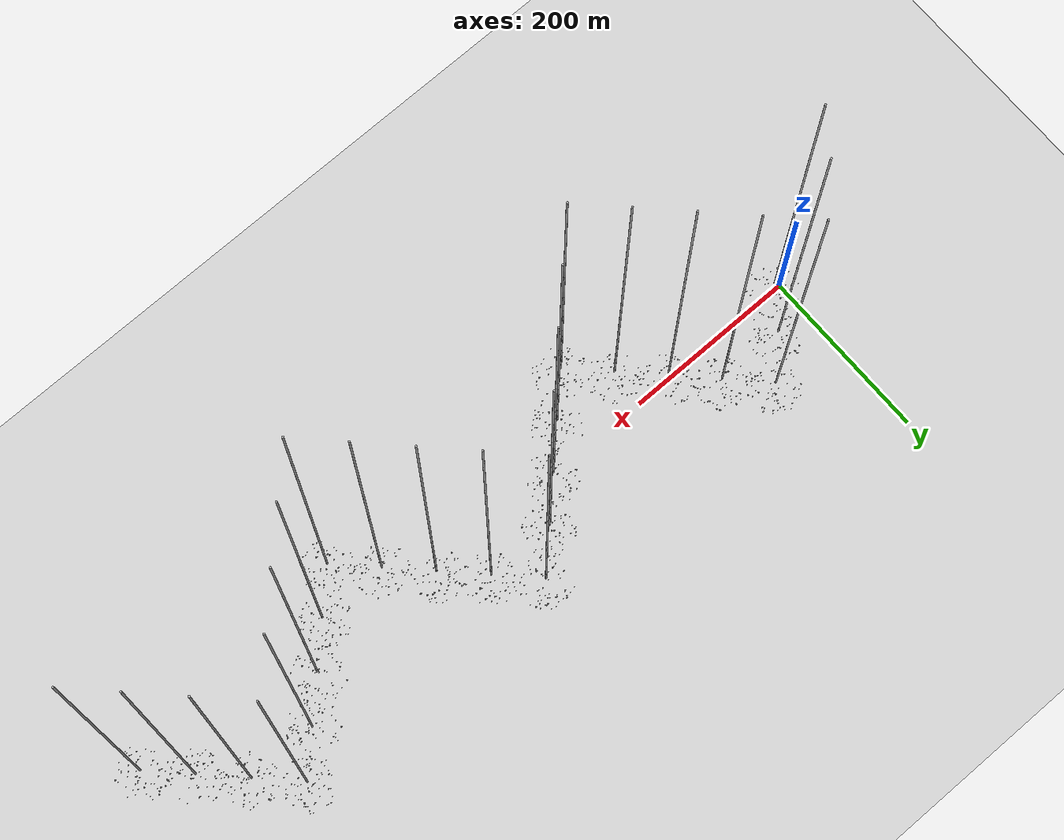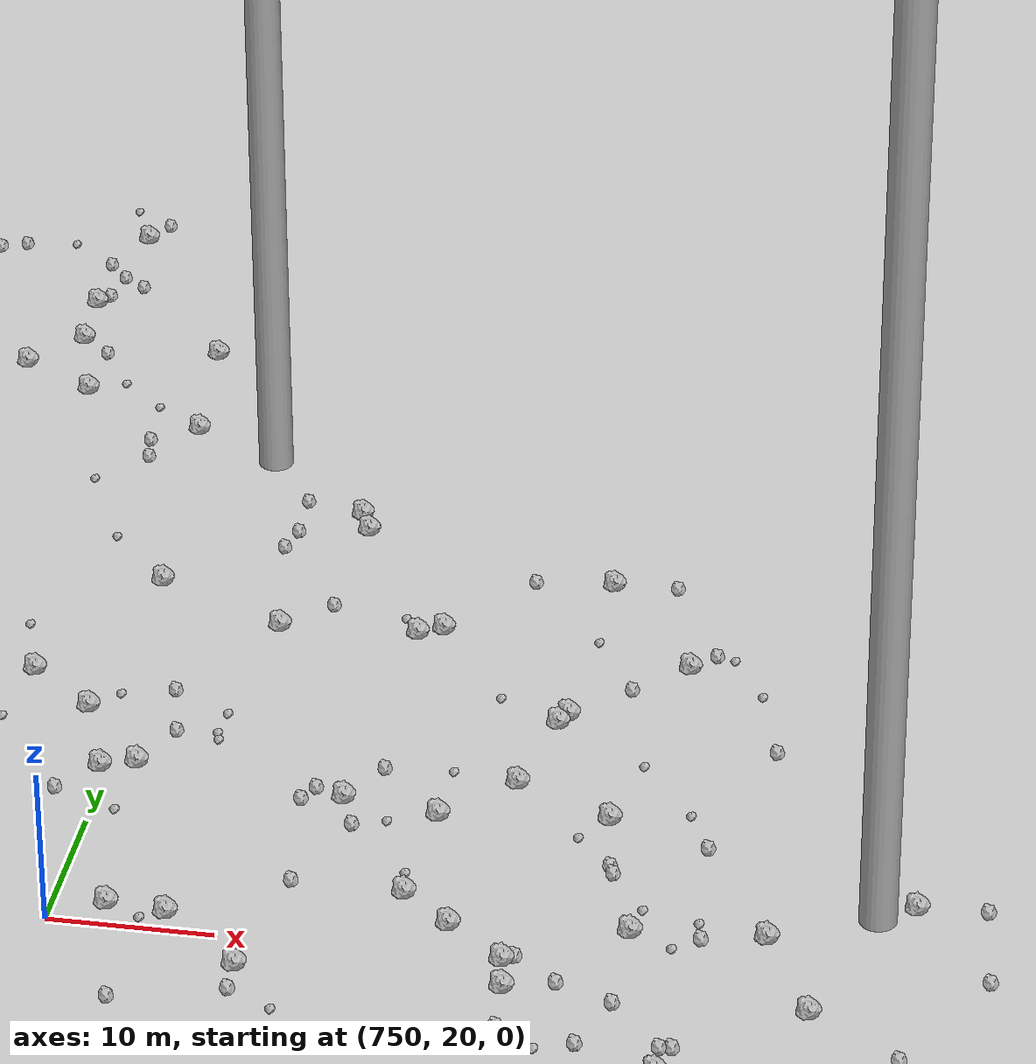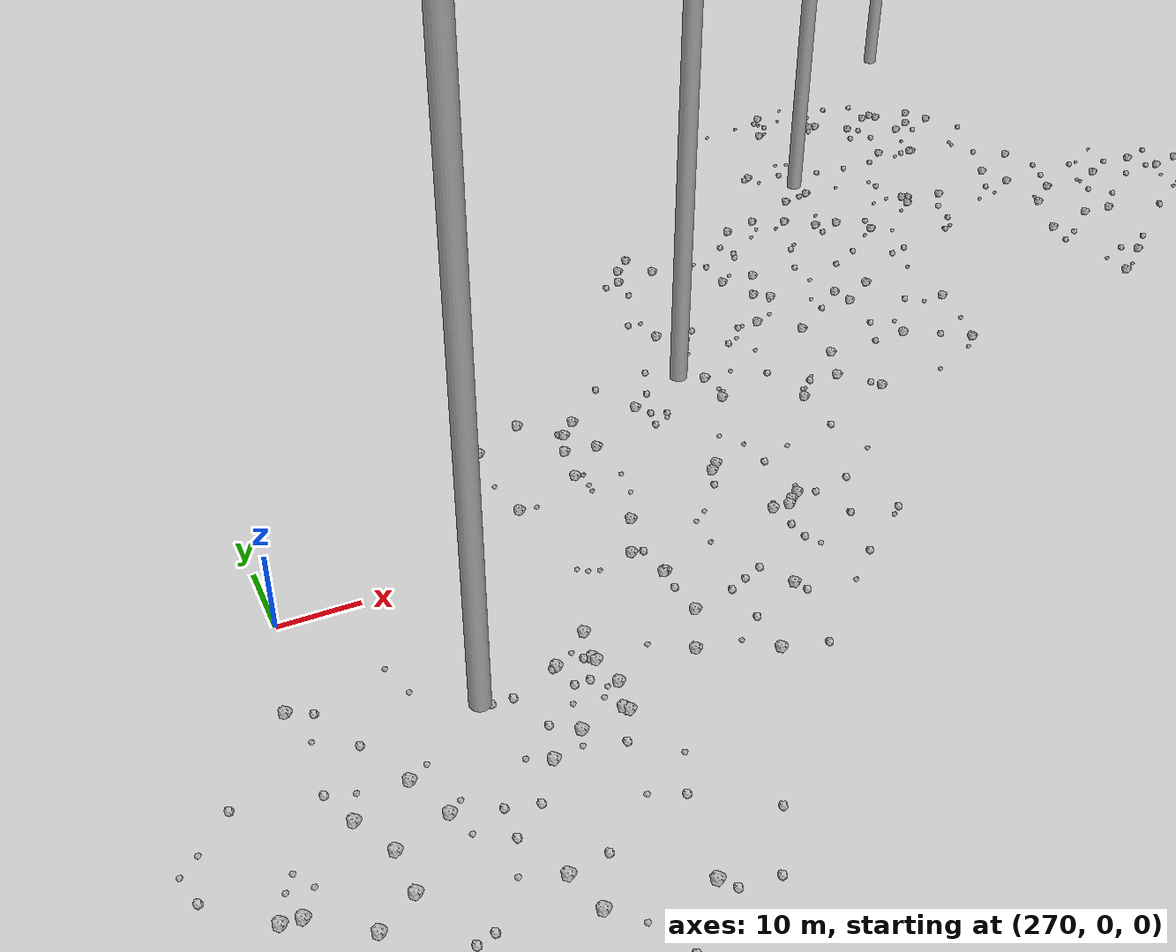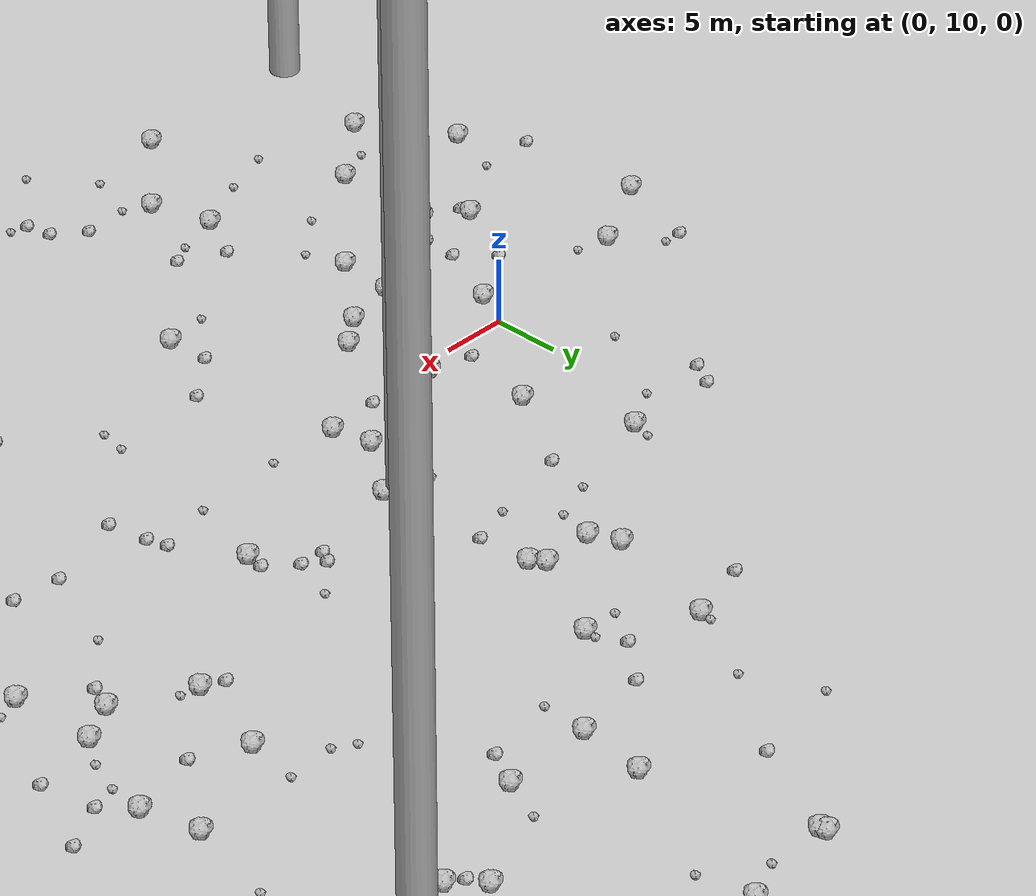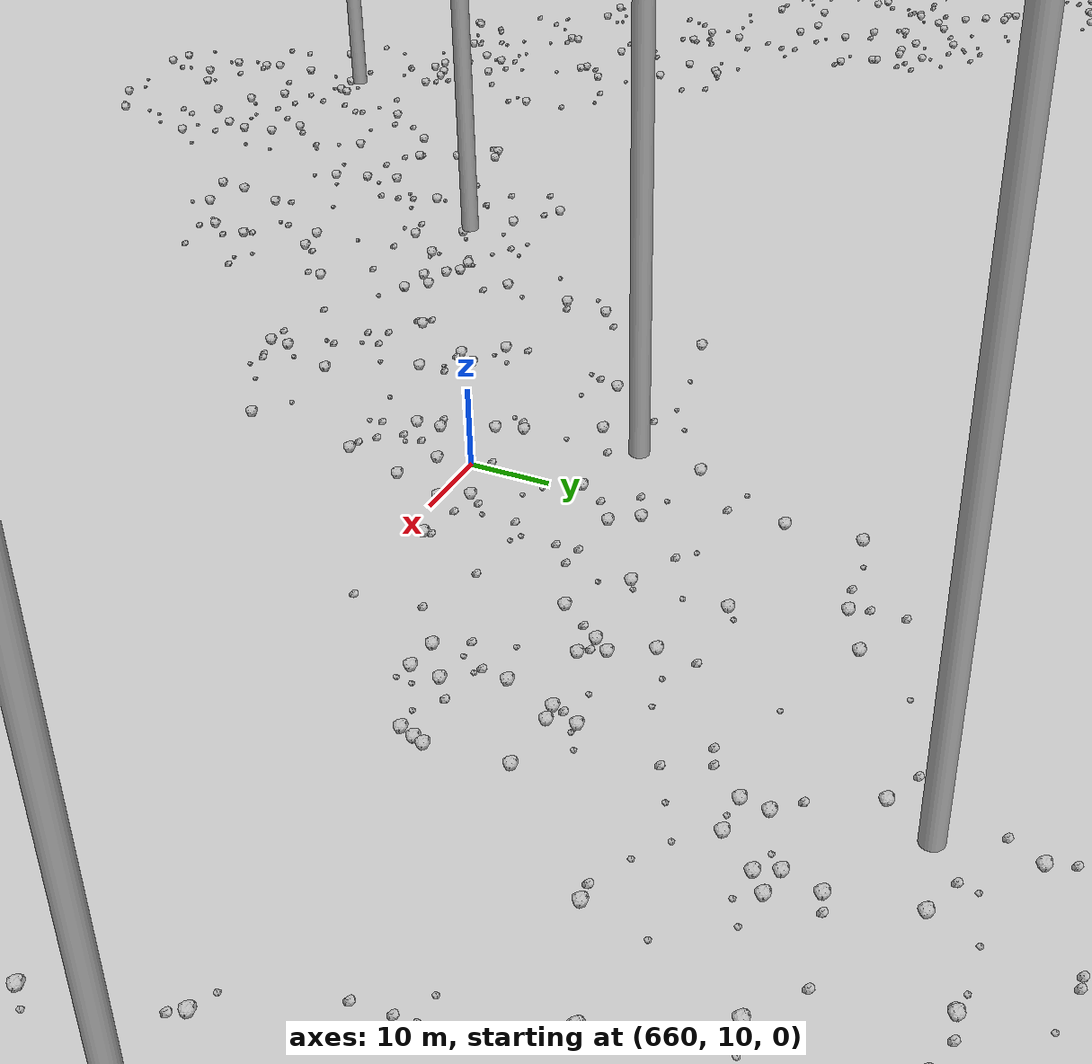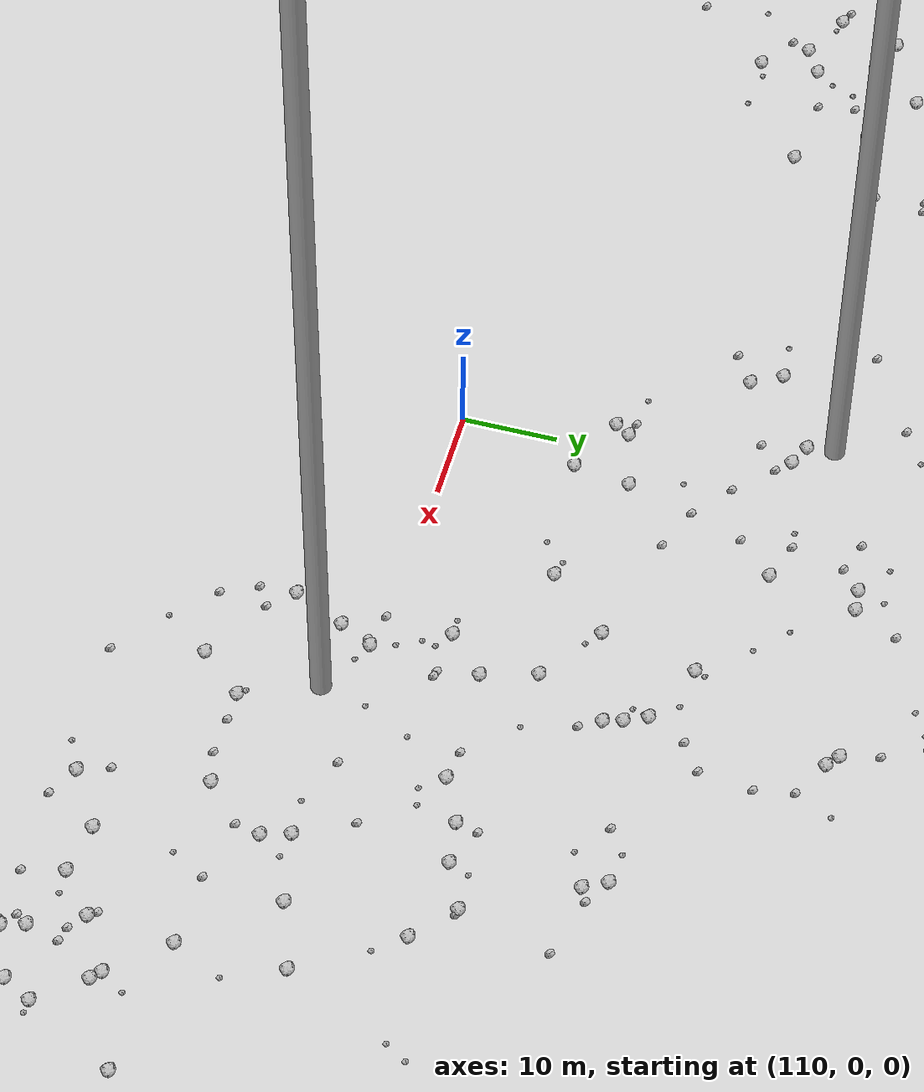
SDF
<sdf version="1.6">
 <world name="default">
  <include><uri>model://custom_ground</uri></include>
  <include><uri>model://sun</uri></include>
  <spherical_coordinates>
   <surface_model>EARTH_WGS84</surface_model>
   <latitude_deg>38.161479</latitude_deg>
   <longitude_deg>-122.454630</longitude_deg>
   <elevation>488.0</elevation>
   <heading_deg>90</heading_deg>
  </spherical_coordinates>
  <model name="rock1_0_0">
   <include><uri>model://rock1</uri><pose>-19.085532682817163 4.844828961862753 0.5 0 0 0</pose></include>
  </model>
  <model name="rock1_0_1">
   <include><uri>model://rock1</uri><pose>29.98500551781283 -12.101282707897678 0.5 0 0 0</pose></include>
  </model>
  <model name="rock1_0_2">
   <include><uri>model://rock1</uri><pose>17.400237714811034 -4.299624235020879 0.5 0 0 0</pose></include>
  </model>
  <model name="rock1_0_3">
   <include><uri>model://rock1</uri><pose>5.886543642120799 -18.297176721765567 0.5 0 0 0</pose></include>
  </model>
  <model name="rock1_0_4">
   <include><uri>model://rock1</uri><pose>-6.349609781417092 -11.137534719862693 0.5 0 0 0</pose></include>
  </model>
  <model name="rock1_0_5">
   <include><uri>model://rock1</uri><pose>-8.813243428215472 -1.1824219057226628 0.5 0 0 0</pose></include>
  </model>
  <model name="rock1_0_6">
   <include><uri>model://rock1</uri><pose>-12.06450352750023 -15.839941510622847 0.5 0 0 0</pose></include>
  </model>
  <model name="rock1_0_7">
   <include><uri>model://rock1</uri><pose>-16.008438096959043 -9.253805651468298 0.5 0 0 0</pose></include>
  </model>
  <model name="rock1_0_8">
   <include><uri>model://rock1</uri><pose>-0.34469749310616393 -24.86324592676843 0.5 0 0 0</pose></include>
  </model>
  <model name="rock1_0_9">
   <include><uri>model://rock1</uri><pose>17.694299531993124 11.473987658099546 0.5 0 0 0</pose></include>
  </model>
  <model name="rock1_0_10">
   <include><uri>model://rock1</uri><pose>-1.2506725966672008 7.256386599827529 0.5 0 0 0</pose></include>
  </model>
  <model name="rock1_0_11">
   <include><uri>model://rock1</uri><pose>2.1883949033071026 -2.6988669014512006 0.5 0 0 0</pose></include>
  </model>
  <model name="rock1_0_12">
   <include><uri>model://rock1</uri><pose>8.080335126814639 11.137513000913806 0.5 0 0 0</pose></include>
  </model>
  <model name="rock1_0_13">
   <include><uri>model://rock1</uri><pose>20.720733005901188 19.108411789299524 0.5 0 0 0</pose></include>
  </model>
  <model name="rock1_0_14">
   <include><uri>model://rock1</uri><pose>-12.834664451413333 8.289941198156548 0.5 0 0 0</pose></include>
  </model>
  <model name="rock1_0_15">
   <include><uri>model://rock1</uri><pose>30.10531323115643 -18.128156663228687 0.5 0 0 0</pose></include>
  </model>
  <model name="rock1_0_16">
   <include><uri>model://rock1</uri><pose>4.663513143033747 -13.620383489596172 0.5 0 0 0</pose></include>
  </model>
  <model name="rock1_0_17">
   <include><uri>model://rock1</uri><pose>9.418962616035333 4.764191750243867 0.5 0 0 0</pose></include>
  </model>
  <model name="rock1_0_18">
   <include><uri>model://rock1</uri><pose>25.102173112449357 -14.768267026885615 0.5 0 0 0</pose></include>
  </model>
  <model name="rock1_0_19">
   <include><uri>model://rock1</uri><pose>2.6500115843774275 1.6815815044789382 0.5 0 0 0</pose></include>
  </model>
  <model name="rock1_0_20">
   <include><uri>model://rock1</uri><pose>26.524206028407455 -24.093484161937425 0.5 0 0 0</pose></include>
  </model>
  <model name="rock1_0_21">
   <include><uri>model://rock1</uri><pose>31.83714578414336 17.899989783821347 0.5 0 0 0</pose></include>
  </model>
  <model name="rock1_0_22">
   <include><uri>model://rock1</uri><pose>6.938741259187083 2.818088958183914 0.5 0 0 0</pose></include>
  </model>
  <model name="rock1_0_23">
   <include><uri>model://rock1</uri><pose>6.29848676640394 17.98183875179179 0.5 0 0 0</pose></include>
  </model>
  <model name="rock1_0_24">
   <include><uri>model://rock1</uri><pose>-6.062630458745339 -3.179231971579501 0.5 0 0 0</pose></include>
  </model>
  <model name="rock1_0_25">
   <include><uri>model://rock1</uri><pose>17.124643260281267 14.470400945605235 0.5 0 0 0</pose></include>
  </model>
  <model name="rock1_0_26">
   <include><uri>model://rock1</uri><pose>3.5988067701978004 25.63204860622968 0.5 0 0 0</pose></include>
  </model>
  <model name="rock2_0_0">
   <include><uri>model://rock2</uri><pose>10.425797415857765 24.54030737550829 0.3 0 0 0</pose></include>
  </model>
  <model name="rock2_0_1">
   <include><uri>model://rock2</uri><pose>13.689815238955156 -22.66165771253462 0.3 0 0 0</pose></include>
  </model>
  <model name="rock2_0_2">
   <include><uri>model://rock2</uri><pose>-8.840655458681228 -2.086580652214554 0.3 0 0 0</pose></include>
  </model>
  <model name="rock2_0_3">
   <include><uri>model://rock2</uri><pose>20.878439031592116 1.9123820933202182 0.3 0 0 0</pose></include>
  </model>
  <model name="rock2_0_4">
   <include><uri>model://rock2</uri><pose>9.785143276138776 -11.53765441874421 0.3 0 0 0</pose></include>
  </model>
  <model name="rock2_0_5">
   <include><uri>model://rock2</uri><pose>13.417658999806577 11.059748091644252 0.3 0 0 0</pose></include>
  </model>
  <model name="rock2_0_6">
   <include><uri>model://rock2</uri><pose>6.53406195701384 -9.920764801748472 0.3 0 0 0</pose></include>
  </model>
  <model name="rock2_0_7">
   <include><uri>model://rock2</uri><pose>29.52341181026842 -12.064221403106707 0.3 0 0 0</pose></include>
  </model>
  <model name="rock2_0_8">
   <include><uri>model://rock2</uri><pose>35.31666570166165 8.75737771489056 0.3 0 0 0</pose></include>
  </model>
  <model name="rock2_0_9">
   <include><uri>model://rock2</uri><pose>13.343039467748326 -20.70750167572931 0.3 0 0 0</pose></include>
  </model>
  <model name="rock2_0_10">
   <include><uri>model://rock2</uri><pose>-4.027916984620363 -0.7790468654345091 0.3 0 0 0</pose></include>
  </model>
  <model name="rock2_0_11">
   <include><uri>model://rock2</uri><pose>-16.88570997991632 11.47321856727718 0.3 0 0 0</pose></include>
  </model>
  <model name="rock2_0_12">
   <include><uri>model://rock2</uri><pose>34.80227687845229 11.747342755579766 0.3 0 0 0</pose></include>
  </model>
  <model name="rock2_0_13">
   <include><uri>model://rock2</uri><pose>-6.042213911946387 4.288184926825245 0.3 0 0 0</pose></include>
  </model>
  <model name="rock2_0_14">
   <include><uri>model://rock2</uri><pose>-18.899861356150932 -5.084036853005074 0.3 0 0 0</pose></include>
  </model>
  <model name="rock2_0_15">
   <include><uri>model://rock2</uri><pose>-3.8831414355045837 1.8847237491624327 0.3 0 0 0</pose></include>
  </model>
  <model name="rock2_0_16">
   <include><uri>model://rock2</uri><pose>33.806101325014126 -3.7189685395357905 0.3 0 0 0</pose></include>
  </model>
  <model name="rock2_0_17">
   <include><uri>model://rock2</uri><pose>-4.803256792833032 23.780418331259433 0.3 0 0 0</pose></include>
  </model>
  <model name="rock2_0_18">
   <include><uri>model://rock2</uri><pose>6.335768560671195 6.9113425470365755 0.3 0 0 0</pose></include>
  </model>
  <model name="rock2_0_19">
   <include><uri>model://rock2</uri><pose>-3.663334774794013 25.660381146595782 0.3 0 0 0</pose></include>
  </model>
  <model name="rock2_0_20">
   <include><uri>model://rock2</uri><pose>17.220282366689624 -1.086153360826426 0.3 0 0 0</pose></include>
  </model>
  <model name="rock2_0_21">
   <include><uri>model://rock2</uri><pose>13.868542396656714 -28.192494148604283 0.3 0 0 0</pose></include>
  </model>
  <model name="rock2_0_22">
   <include><uri>model://rock2</uri><pose>34.363256959340625 13.22122780964117 0.3 0 0 0</pose></include>
  </model>
  <model name="rock2_0_23">
   <include><uri>model://rock2</uri><pose>25.699797038591008 -23.770724075628383 0.3 0 0 0</pose></include>
  </model>
  <model name="rock2_0_24">
   <include><uri>model://rock2</uri><pose>31.924088132675024 19.246238401600266 0.3 0 0 0</pose></include>
  </model>
  <model name="rock2_0_25">
   <include><uri>model://rock2</uri><pose>11.210349813217974 -18.99083656144633 0.3 0 0 0</pose></include>
  </model>
  <model name="rock2_0_26">
   <include><uri>model://rock2</uri><pose>4.733577912333004 11.90981731324986 0.3 0 0 0</pose></include>
  </model>
  <model name="rock3_0_0">
   <include><uri>model://rock3</uri><pose>-9.547968328306611 -12.622755368906319 0.2 0 0 0</pose></include>
  </model>
  <model name="rock3_0_1">
   <include><uri>model://rock3</uri><pose>6.048656113246896 -23.394599676399878 0.2 0 0 0</pose></include>
  </model>
  <model name="rock3_0_2">
   <include><uri>model://rock3</uri><pose>2.917415542008623 -5.796076192776344 0.2 0 0 0</pose></include>
  </model>
  <model name="rock3_0_3">
   <include><uri>model://rock3</uri><pose>8.01135006914462 -12.602043537637101 0.2 0 0 0</pose></include>
  </model>
  <model name="rock3_0_4">
   <include><uri>model://rock3</uri><pose>17.04416489903715 19.940531706277994 0.2 0 0 0</pose></include>
  </model>
  <model name="rock3_0_5">
   <include><uri>model://rock3</uri><pose>-0.6138999198952249 -8.73614217235162 0.2 0 0 0</pose></include>
  </model>
  <model name="rock3_0_6">
   <include><uri>model://rock3</uri><pose>0.0001702681094855052 23.524612288121027 0.2 0 0 0</pose></include>
  </model>
  <model name="rock3_0_7">
   <include><uri>model://rock3</uri><pose>7.572617381272039 -19.464995594557536 0.2 0 0 0</pose></include>
  </model>
  <model name="rock3_0_8">
   <include><uri>model://rock3</uri><pose>3.779082922405241 26.98421225993772 0.2 0 0 0</pose></include>
  </model>
  <model name="rock3_0_9">
   <include><uri>model://rock3</uri><pose>-15.54144089975058 11.387261891631923 0.2 0 0 0</pose></include>
  </model>
  <model name="rock3_0_10">
   <include><uri>model://rock3</uri><pose>35.0580561844538 -3.1303487477655665 0.2 0 0 0</pose></include>
  </model>
  <model name="rock3_0_11">
   <include><uri>model://rock3</uri><pose>22.915911319989362 11.263143355241702 0.2 0 0 0</pose></include>
  </model>
  <model name="rock3_0_12">
   <include><uri>model://rock3</uri><pose>14.888649331443808 -23.073517764982565 0.2 0 0 0</pose></include>
  </model>
  <model name="rock3_0_13">
   <include><uri>model://rock3</uri><pose>9.207932927014923 -27.697772455780648 0.2 0 0 0</pose></include>
  </model>
  <model name="rock3_0_14">
   <include><uri>model://rock3</uri><pose>23.280754887022326 -22.38804418806849 0.2 0 0 0</pose></include>
  </model>
  <model name="rock3_0_15">
   <include><uri>model://rock3</uri><pose>14.402753969821227 29.221359423410107 0.2 0 0 0</pose></include>
  </model>
  <model name="rock3_0_16">
   <include><uri>model://rock3</uri><pose>29.907427350780814 11.869328570964143 0.2 0 0 0</pose></include>
  </model>
  <model name="rock3_0_17">
   <include><uri>model://rock3</uri><pose>11.185910889876208 27.97926660736399 0.2 0 0 0</pose></include>
  </model>
  <model name="rock3_0_18">
   <include><uri>model://rock3</uri><pose>-0.10545404624642174 -16.081757363259676 0.2 0 0 0</pose></include>
  </model>
  <model name="rock3_0_19">
   <include><uri>model://rock3</uri><pose>-10.497797388295048 7.654545858861198 0.2 0 0 0</pose></include>
  </model>
  <model name="rock3_0_20">
   <include><uri>model://rock3</uri><pose>28.580079577941106 2.7737158160637705 0.2 0 0 0</pose></include>
  </model>
  <model name="rock3_0_21">
   <include><uri>model://rock3</uri><pose>-14.5963225065194 -4.990547462266758 0.2 0 0 0</pose></include>
  </model>
  <model name="rock3_0_22">
   <include><uri>model://rock3</uri><pose>13.754557459556466 -5.013965581135469 0.2 0 0 0</pose></include>
  </model>
  <model name="rock3_0_23">
   <include><uri>model://rock3</uri><pose>-3.8500304541353145 17.15940851175889 0.2 0 0 0</pose></include>
  </model>
  <model name="rock3_0_24">
   <include><uri>model://rock3</uri><pose>28.17646864417783 0.6948669405875485 0.2 0 0 0</pose></include>
  </model>
  <model name="rock3_0_25">
   <include><uri>model://rock3</uri><pose>-5.2729337651451615 -3.280133574128609 0.2 0 0 0</pose></include>
  </model>
  <model name="rock3_0_26">
   <include><uri>model://rock3</uri><pose>-4.114155596654312 -17.62863306999904 0.2 0 0 0</pose></include>
  </model>
  <model name="rock1_1_0">
   <include><uri>model://rock1</uri><pose>28.505121327483035 63.31210169767515 0.5 0 0 0</pose></include>
  </model>
  <model name="rock1_1_1">
   <include><uri>model://rock1</uri><pose>30.975069456452104 46.13505605601982 0.5 0 0 0</pose></include>
  </model>
  <model name="rock1_1_2">
   <include><uri>model://rock1</uri><pose>20.053641276641468 31.306719100113593 0.5 0 0 0</pose></include>
  </model>
  <model name="rock1_1_3">
   <include><uri>model://rock1</uri><pose>47.54602527341225 50.17995663697143 0.5 0 0 0</pose></include>
  </model>
  <model name="rock1_1_4">
   <include><uri>model://rock1</uri><pose>19.33368860244465 32.28071462196004 0.5 0 0 0</pose></include>
  </model>
  <model name="rock1_1_5">
   <include><uri>model://rock1</uri><pose>42.03257849538712 62.92974936045555 0.5 0 0 0</pose></include>
  </model>
  <model name="rock1_1_6">
   <include><uri>model://rock1</uri><pose>52.268175025336845 18.474666944716347 0.5 0 0 0</pose></include>
  </model>
  <model name="rock1_1_7">
   <include><uri>model://rock1</uri><pose>31.658434317452247 51.197426895810906 0.5 0 0 0</pose></include>
  </model>
  <model name="rock1_1_8">
   <include><uri>model://rock1</uri><pose>45.70109241427307 52.230039067230884 0.5 0 0 0</pose></include>
  </model>
  <model name="rock1_1_9">
   <include><uri>model://rock1</uri><pose>53.7382611096111 36.28703167551265 0.5 0 0 0</pose></include>
  </model>
  <model name="rock1_1_10">
   <include><uri>model://rock1</uri><pose>45.66577340477773 32.41904496474776 0.5 0 0 0</pose></include>
  </model>
  <model name="rock1_1_11">
   <include><uri>model://rock1</uri><pose>28.606971498351555 62.84445119356784 0.5 0 0 0</pose></include>
  </model>
  <model name="rock1_1_12">
   <include><uri>model://rock1</uri><pose>52.00893571538702 24.784676114071686 0.5 0 0 0</pose></include>
  </model>
  <model name="rock1_1_13">
   <include><uri>model://rock1</uri><pose>54.72995581519607 32.0969609938406 0.5 0 0 0</pose></include>
  </model>
  <model name="rock1_1_14">
   <include><uri>model://rock1</uri><pose>43.72622142232372 25.841492777617464 0.5 0 0 0</pose></include>
  </model>
  <model name="rock1_1_15">
   <include><uri>model://rock1</uri><pose>48.55341326801644 61.29385884124869 0.5 0 0 0</pose></include>
  </model>
  <model name="rock1_1_16">
   <include><uri>model://rock1</uri><pose>16.80779296332897 43.07337850435742 0.5 0 0 0</pose></include>
  </model>
  <model name="rock1_1_17">
   <include><uri>model://rock1</uri><pose>14.37901270894171 34.20295566041843 0.5 0 0 0</pose></include>
  </model>
  <model name="rock1_1_18">
   <include><uri>model://rock1</uri><pose>55.73034790572387 61.83112779674461 0.5 0 0 0</pose></include>
  </model>
  <model name="rock1_1_19">
   <include><uri>model://rock1</uri><pose>15.306683291633696 32.09748017059572 0.5 0 0 0</pose></include>
  </model>
  <model name="rock1_1_20">
   <include><uri>model://rock1</uri><pose>36.12526903217125 64.31727756020037 0.5 0 0 0</pose></include>
  </model>
  <model name="rock1_1_21">
   <include><uri>model://rock1</uri><pose>49.04754901912979 23.114646086960647 0.5 0 0 0</pose></include>
  </model>
  <model name="rock1_1_22">
   <include><uri>model://rock1</uri><pose>65.22591717384707 25.102280592503394 0.5 0 0 0</pose></include>
  </model>
  <model name="rock1_1_23">
   <include><uri>model://rock1</uri><pose>49.05047427623241 65.40367331541825 0.5 0 0 0</pose></include>
  </model>
  <model name="rock1_1_24">
   <include><uri>model://rock1</uri><pose>23.230446336070173 39.13942066001982 0.5 0 0 0</pose></include>
  </model>
  <model name="rock1_1_25">
   <include><uri>model://rock1</uri><pose>37.83771476216474 46.4445636105652 0.5 0 0 0</pose></include>
  </model>
  <model name="rock1_1_26">
   <include><uri>model://rock1</uri><pose>35.22561112513195 68.4723046704963 0.5 0 0 0</pose></include>
  </model>
  <model name="rock2_1_0">
   <include><uri>model://rock2</uri><pose>53.789644953740265 49.45980192560808 0.3 0 0 0</pose></include>
  </model>
  <model name="rock2_1_1">
   <include><uri>model://rock2</uri><pose>22.13322592676314 41.824110474884876 0.3 0 0 0</pose></include>
  </model>
  <model name="rock2_1_2">
   <include><uri>model://rock2</uri><pose>28.669149767738688 21.96782498943371 0.3 0 0 0</pose></include>
  </model>
  <model name="rock2_1_3">
   <include><uri>model://rock2</uri><pose>30.001765935502558 20.946225630233705 0.3 0 0 0</pose></include>
  </model>
  <model name="rock2_1_4">
   <include><uri>model://rock2</uri><pose>46.97345787687531 59.302539205347934 0.3 0 0 0</pose></include>
  </model>
  <model name="rock2_1_5">
   <include><uri>model://rock2</uri><pose>45.209815744780464 10.586862780062603 0.3 0 0 0</pose></include>
  </model>
  <model name="rock2_1_6">
   <include><uri>model://rock2</uri><pose>11.761261809873687 41.59614613651702 0.3 0 0 0</pose></include>
  </model>
  <model name="rock2_1_7">
   <include><uri>model://rock2</uri><pose>48.12483450502603 21.186672394150172 0.3 0 0 0</pose></include>
  </model>
  <model name="rock2_1_8">
   <include><uri>model://rock2</uri><pose>35.917725078335614 67.48416751170791 0.3 0 0 0</pose></include>
  </model>
  <model name="rock2_1_9">
   <include><uri>model://rock2</uri><pose>56.344777755553594 29.975693800322517 0.3 0 0 0</pose></include>
  </model>
  <model name="rock2_1_10">
   <include><uri>model://rock2</uri><pose>62.11591370274916 46.20106271891805 0.3 0 0 0</pose></include>
  </model>
  <model name="rock2_1_11">
   <include><uri>model://rock2</uri><pose>68.5174640784548 34.84620954695551 0.3 0 0 0</pose></include>
  </model>
  <model name="rock2_1_12">
   <include><uri>model://rock2</uri><pose>24.838738557983895 55.559018778714346 0.3 0 0 0</pose></include>
  </model>
  <model name="rock2_1_13">
   <include><uri>model://rock2</uri><pose>49.28665498366929 30.59372104533008 0.3 0 0 0</pose></include>
  </model>
  <model name="rock2_1_14">
   <include><uri>model://rock2</uri><pose>20.14241233043812 27.280057828615472 0.3 0 0 0</pose></include>
  </model>
  <model name="rock2_1_15">
   <include><uri>model://rock2</uri><pose>41.64699861732828 10.913447485799175 0.3 0 0 0</pose></include>
  </model>
  <model name="rock2_1_16">
   <include><uri>model://rock2</uri><pose>33.22684714474535 34.958205703633524 0.3 0 0 0</pose></include>
  </model>
  <model name="rock2_1_17">
   <include><uri>model://rock2</uri><pose>28.122410743174175 20.98743095441237 0.3 0 0 0</pose></include>
  </model>
  <model name="rock2_1_18">
   <include><uri>model://rock2</uri><pose>46.24888411719545 50.82667427603537 0.3 0 0 0</pose></include>
  </model>
  <model name="rock2_1_19">
   <include><uri>model://rock2</uri><pose>42.058767383054736 26.481993547550235 0.3 0 0 0</pose></include>
  </model>
  <model name="rock2_1_20">
   <include><uri>model://rock2</uri><pose>36.26481287866885 43.765798449416046 0.3 0 0 0</pose></include>
  </model>
  <model name="rock2_1_21">
   <include><uri>model://rock2</uri><pose>24.81598160825226 44.91813113258725 0.3 0 0 0</pose></include>
  </model>
  <model name="rock2_1_22">
   <include><uri>model://rock2</uri><pose>57.02235977410773 25.97264056164868 0.3 0 0 0</pose></include>
  </model>
  <model name="rock2_1_23">
   <include><uri>model://rock2</uri><pose>65.50175663441485 46.7252231211868 0.3 0 0 0</pose></include>
  </model>
  <model name="rock2_1_24">
   <include><uri>model://rock2</uri><pose>67.83274107849577 40.17642007524597 0.3 0 0 0</pose></include>
  </model>
  <model name="rock2_1_25">
   <include><uri>model://rock2</uri><pose>69.14265326920145 40.209959232721715 0.3 0 0 0</pose></include>
  </model>
  <model name="rock2_1_26">
   <include><uri>model://rock2</uri><pose>59.768084320752 31.80940218385054 0.3 0 0 0</pose></include>
  </model>
  <model name="rock3_1_0">
   <include><uri>model://rock3</uri><pose>39.072456627344806 49.537655958465564 0.2 0 0 0</pose></include>
  </model>
  <model name="rock3_1_1">
   <include><uri>model://rock3</uri><pose>53.3558518395312 60.81584930638731 0.2 0 0 0</pose></include>
  </model>
  <model name="rock3_1_2">
   <include><uri>model://rock3</uri><pose>44.37180453388434 17.444264341925514 0.2 0 0 0</pose></include>
  </model>
  <model name="rock3_1_3">
   <include><uri>model://rock3</uri><pose>42.49435889597957 35.98757257539323 0.2 0 0 0</pose></include>
  </model>
  <model name="rock3_1_4">
   <include><uri>model://rock3</uri><pose>35.332624871162224 65.54394179341429 0.2 0 0 0</pose></include>
  </model>
  <model name="rock3_1_5">
   <include><uri>model://rock3</uri><pose>53.94996024861419 19.019605969698606 0.2 0 0 0</pose></include>
  </model>
  <model name="rock3_1_6">
   <include><uri>model://rock3</uri><pose>16.70732690507606 43.85668768033214 0.2 0 0 0</pose></include>
  </model>
  <model name="rock3_1_7">
   <include><uri>model://rock3</uri><pose>58.400774569725385 18.36365737041833 0.2 0 0 0</pose></include>
  </model>
  <model name="rock3_1_8">
   <include><uri>model://rock3</uri><pose>23.043733304276103 39.85866112905737 0.2 0 0 0</pose></include>
  </model>
  <model name="rock3_1_9">
   <include><uri>model://rock3</uri><pose>17.578535208839245 54.05434684608749 0.2 0 0 0</pose></include>
  </model>
  <model name="rock3_1_10">
   <include><uri>model://rock3</uri><pose>55.2323256960052 42.87365486828948 0.2 0 0 0</pose></include>
  </model>
  <model name="rock3_1_11">
   <include><uri>model://rock3</uri><pose>16.824710807324415 26.108967489282712 0.2 0 0 0</pose></include>
  </model>
  <model name="rock3_1_12">
   <include><uri>model://rock3</uri><pose>19.919187411437335 48.95013536092979 0.2 0 0 0</pose></include>
  </model>
  <model name="rock3_1_13">
   <include><uri>model://rock3</uri><pose>47.56158675925716 61.45303200517624 0.2 0 0 0</pose></include>
  </model>
  <model name="rock3_1_14">
   <include><uri>model://rock3</uri><pose>20.290319648550348 39.038700934669905 0.2 0 0 0</pose></include>
  </model>
  <model name="rock3_1_15">
   <include><uri>model://rock3</uri><pose>54.2678692005166 29.280252159570253 0.2 0 0 0</pose></include>
  </model>
  <model name="rock3_1_16">
   <include><uri>model://rock3</uri><pose>50.76003235109409 49.75210571709875 0.2 0 0 0</pose></include>
  </model>
  <model name="rock3_1_17">
   <include><uri>model://rock3</uri><pose>37.179491039393795 36.83737990568329 0.2 0 0 0</pose></include>
  </model>
  <model name="rock3_1_18">
   <include><uri>model://rock3</uri><pose>30.54635227998989 42.510416216059916 0.2 0 0 0</pose></include>
  </model>
  <model name="rock3_1_19">
   <include><uri>model://rock3</uri><pose>41.03969914142461 36.85357983847847 0.2 0 0 0</pose></include>
  </model>
  <model name="rock3_1_20">
   <include><uri>model://rock3</uri><pose>44.941015270582426 25.412564811877544 0.2 0 0 0</pose></include>
  </model>
  <model name="rock3_1_21">
   <include><uri>model://rock3</uri><pose>53.298624852734065 26.77559347609671 0.2 0 0 0</pose></include>
  </model>
  <model name="rock3_1_22">
   <include><uri>model://rock3</uri><pose>31.189076648172176 24.23343066544411 0.2 0 0 0</pose></include>
  </model>
  <model name="rock3_1_23">
   <include><uri>model://rock3</uri><pose>36.730595935007145 60.2544294163442 0.2 0 0 0</pose></include>
  </model>
  <model name="rock3_1_24">
   <include><uri>model://rock3</uri><pose>46.150130645026074 36.24725405254272 0.2 0 0 0</pose></include>
  </model>
  <model name="rock3_1_25">
   <include><uri>model://rock3</uri><pose>19.318426204253797 20.82378278471682 0.2 0 0 0</pose></include>
  </model>
  <model name="rock3_1_26">
   <include><uri>model://rock3</uri><pose>32.86264071639531 62.81515694966666 0.2 0 0 0</pose></include>
  </model>
  <model name="rock1_2_0">
   <include><uri>model://rock1</uri><pose>103.2618640863892 90.20630187753328 0.5 0 0 0</pose></include>
  </model>
  <model name="rock1_2_1">
   <include><uri>model://rock1</uri><pose>106.42423240863269 92.06755766622172 0.5 0 0 0</pose></include>
  </model>
  <model name="rock1_2_2">
   <include><uri>model://rock1</uri><pose>86.26385779776638 101.91243206358388 0.5 0 0 0</pose></include>
  </model>
  <model name="rock1_2_3">
   <include><uri>model://rock1</uri><pose>88.46100230981966 95.68296516139712 0.5 0 0 0</pose></include>
  </model>
  <model name="rock1_2_4">
   <include><uri>model://rock1</uri><pose>106.32391444122304 68.18631994320022 0.5 0 0 0</pose></include>
  </model>
  <model name="rock1_2_5">
   <include><uri>model://rock1</uri><pose>83.53864633943311 86.61930709300987 0.5 0 0 0</pose></include>
  </model>
  <model name="rock1_2_6">
   <include><uri>model://rock1</uri><pose>84.22714708729214 58.76215108278592 0.5 0 0 0</pose></include>
  </model>
  <model name="rock1_2_7">
   <include><uri>model://rock1</uri><pose>69.69347781189938 64.70583540232522 0.5 0 0 0</pose></include>
  </model>
  <model name="rock1_2_8">
   <include><uri>model://rock1</uri><pose>103.78724455966744 72.38935650334106 0.5 0 0 0</pose></include>
  </model>
  <model name="rock1_2_9">
   <include><uri>model://rock1</uri><pose>87.0066934717704 92.88062708177884 0.5 0 0 0</pose></include>
  </model>
  <model name="rock1_2_10">
   <include><uri>model://rock1</uri><pose>97.68752177020164 98.09463419055879 0.5 0 0 0</pose></include>
  </model>
  <model name="rock1_2_11">
   <include><uri>model://rock1</uri><pose>79.78765406483987 58.75835949342551 0.5 0 0 0</pose></include>
  </model>
  <model name="rock1_2_12">
   <include><uri>model://rock1</uri><pose>79.89972231597388 74.30007864836361 0.5 0 0 0</pose></include>
  </model>
  <model name="rock1_2_13">
   <include><uri>model://rock1</uri><pose>104.29416928150602 87.86921339572433 0.5 0 0 0</pose></include>
  </model>
  <model name="rock1_2_14">
   <include><uri>model://rock1</uri><pose>77.16925684936933 105.19889925016199 0.5 0 0 0</pose></include>
  </model>
  <model name="rock1_2_15">
   <include><uri>model://rock1</uri><pose>59.30034788632516 61.758519222689266 0.5 0 0 0</pose></include>
  </model>
  <model name="rock1_2_16">
   <include><uri>model://rock1</uri><pose>55.77284548902375 96.30049657965034 0.5 0 0 0</pose></include>
  </model>
  <model name="rock1_2_17">
   <include><uri>model://rock1</uri><pose>61.64362498575356 76.3118871511856 0.5 0 0 0</pose></include>
  </model>
  <model name="rock1_2_18">
   <include><uri>model://rock1</uri><pose>86.78729415733535 57.604391543761174 0.5 0 0 0</pose></include>
  </model>
  <model name="rock1_2_19">
   <include><uri>model://rock1</uri><pose>90.20423159486919 100.27563219094255 0.5 0 0 0</pose></include>
  </model>
  <model name="rock1_2_20">
   <include><uri>model://rock1</uri><pose>96.1906936682663 73.27141660100358 0.5 0 0 0</pose></include>
  </model>
  <model name="rock1_2_21">
   <include><uri>model://rock1</uri><pose>87.91572519280615 63.810448214299456 0.5 0 0 0</pose></include>
  </model>
  <model name="rock1_2_22">
   <include><uri>model://rock1</uri><pose>99.46607438815148 58.78729503331422 0.5 0 0 0</pose></include>
  </model>
  <model name="rock1_2_23">
   <include><uri>model://rock1</uri><pose>64.43259027906912 74.79619887479866 0.5 0 0 0</pose></include>
  </model>
  <model name="rock1_2_24">
   <include><uri>model://rock1</uri><pose>83.61330890560902 66.4903194071998 0.5 0 0 0</pose></include>
  </model>
  <model name="rock1_2_25">
   <include><uri>model://rock1</uri><pose>91.0269713613892 57.39576109063479 0.5 0 0 0</pose></include>
  </model>
  <model name="rock1_2_26">
   <include><uri>model://rock1</uri><pose>93.51725454377814 59.18009298050529 0.5 0 0 0</pose></include>
  </model>
  <model name="rock2_2_0">
   <include><uri>model://rock2</uri><pose>71.71332143583008 63.51150128283471 0.3 0 0 0</pose></include>
  </model>
  <model name="rock2_2_1">
   <include><uri>model://rock2</uri><pose>63.00927049185483 94.70308593853807 0.3 0 0 0</pose></include>
  </model>
  <model name="rock2_2_2">
   <include><uri>model://rock2</uri><pose>56.060934196528095 80.63583879026463 0.3 0 0 0</pose></include>
  </model>
  <model name="rock2_2_3">
   <include><uri>model://rock2</uri><pose>53.16662655129493 77.51671863307546 0.3 0 0 0</pose></include>
  </model>
  <model name="rock2_2_4">
   <include><uri>model://rock2</uri><pose>68.52941842764096 54.29668289988559 0.3 0 0 0</pose></include>
  </model>
  <model name="rock2_2_5">
   <include><uri>model://rock2</uri><pose>94.21921505909631 101.03541631023973 0.3 0 0 0</pose></include>
  </model>
  <model name="rock2_2_6">
   <include><uri>model://rock2</uri><pose>81.09280876018308 61.27961259209579 0.3 0 0 0</pose></include>
  </model>
  <model name="rock2_2_7">
   <include><uri>model://rock2</uri><pose>83.72762293982717 84.31692903183578 0.3 0 0 0</pose></include>
  </model>
  <model name="rock2_2_8">
   <include><uri>model://rock2</uri><pose>87.95271036852645 105.34609210010282 0.3 0 0 0</pose></include>
  </model>
  <model name="rock2_2_9">
   <include><uri>model://rock2</uri><pose>89.58034626326366 59.830186092386946 0.3 0 0 0</pose></include>
  </model>
  <model name="rock2_2_10">
   <include><uri>model://rock2</uri><pose>72.73889845302847 86.80693121239656 0.3 0 0 0</pose></include>
  </model>
  <model name="rock2_2_11">
   <include><uri>model://rock2</uri><pose>82.43334074072494 109.1628228634471 0.3 0 0 0</pose></include>
  </model>
  <model name="rock2_2_12">
   <include><uri>model://rock2</uri><pose>65.0945728481063 95.03986157907825 0.3 0 0 0</pose></include>
  </model>
  <model name="rock2_2_13">
   <include><uri>model://rock2</uri><pose>88.61031004575668 80.62344946399628 0.3 0 0 0</pose></include>
  </model>
  <model name="rock2_2_14">
   <include><uri>model://rock2</uri><pose>75.03675146466298 80.1557857798432 0.3 0 0 0</pose></include>
  </model>
  <model name="rock2_2_15">
   <include><uri>model://rock2</uri><pose>85.83571610107094 84.22401396746285 0.3 0 0 0</pose></include>
  </model>
  <model name="rock2_2_16">
   <include><uri>model://rock2</uri><pose>66.90259411486873 86.0106934224586 0.3 0 0 0</pose></include>
  </model>
  <model name="rock2_2_17">
   <include><uri>model://rock2</uri><pose>87.82354960835448 51.05084975446819 0.3 0 0 0</pose></include>
  </model>
  <model name="rock2_2_18">
   <include><uri>model://rock2</uri><pose>69.42647375859795 103.85458649307097 0.3 0 0 0</pose></include>
  </model>
  <model name="rock2_2_19">
   <include><uri>model://rock2</uri><pose>77.6180422768042 94.53914712972244 0.3 0 0 0</pose></include>
  </model>
  <model name="rock2_2_20">
   <include><uri>model://rock2</uri><pose>56.085045346767046 95.26655014247302 0.3 0 0 0</pose></include>
  </model>
  <model name="rock2_2_21">
   <include><uri>model://rock2</uri><pose>100.03813001236617 100.51576375986711 0.3 0 0 0</pose></include>
  </model>
  <model name="rock2_2_22">
   <include><uri>model://rock2</uri><pose>67.18147061608317 68.33962924289997 0.3 0 0 0</pose></include>
  </model>
  <model name="rock2_2_23">
   <include><uri>model://rock2</uri><pose>75.17398026961429 76.05312627207803 0.3 0 0 0</pose></include>
  </model>
  <model name="rock2_2_24">
   <include><uri>model://rock2</uri><pose>96.63060529608939 63.26396596876529 0.3 0 0 0</pose></include>
  </model>
  <model name="rock2_2_25">
   <include><uri>model://rock2</uri><pose>76.80394868111965 108.4616804345064 0.3 0 0 0</pose></include>
  </model>
  <model name="rock2_2_26">
   <include><uri>model://rock2</uri><pose>65.84094254717799 94.85519613895744 0.3 0 0 0</pose></include>
  </model>
  <model name="rock3_2_0">
   <include><uri>model://rock3</uri><pose>67.24623743500543 65.60158292040452 0.2 0 0 0</pose></include>
  </model>
  <model name="rock3_2_1">
   <include><uri>model://rock3</uri><pose>63.82971782995875 98.12556513590715 0.2 0 0 0</pose></include>
  </model>
  <model name="rock3_2_2">
   <include><uri>model://rock3</uri><pose>71.42311145656333 102.0568823214151 0.2 0 0 0</pose></include>
  </model>
  <model name="rock3_2_3">
   <include><uri>model://rock3</uri><pose>94.50835396833963 84.57720397587863 0.2 0 0 0</pose></include>
  </model>
  <model name="rock3_2_4">
   <include><uri>model://rock3</uri><pose>102.63230266736161 75.61879094347739 0.2 0 0 0</pose></include>
  </model>
  <model name="rock3_2_5">
   <include><uri>model://rock3</uri><pose>76.82531817072383 83.82477441006981 0.2 0 0 0</pose></include>
  </model>
  <model name="rock3_2_6">
   <include><uri>model://rock3</uri><pose>66.80091552615582 84.03105330521103 0.2 0 0 0</pose></include>
  </model>
  <model name="rock3_2_7">
   <include><uri>model://rock3</uri><pose>83.16830789108025 79.39704042652367 0.2 0 0 0</pose></include>
  </model>
  <model name="rock3_2_8">
   <include><uri>model://rock3</uri><pose>64.36535968304344 104.75516577912029 0.2 0 0 0</pose></include>
  </model>
  <model name="rock3_2_9">
   <include><uri>model://rock3</uri><pose>103.00961813560798 89.95626507557884 0.2 0 0 0</pose></include>
  </model>
  <model name="rock3_2_10">
   <include><uri>model://rock3</uri><pose>61.12102723390822 98.3251202708185 0.2 0 0 0</pose></include>
  </model>
  <model name="rock3_2_11">
   <include><uri>model://rock3</uri><pose>86.71923327854265 65.47986604757219 0.2 0 0 0</pose></include>
  </model>
  <model name="rock3_2_12">
   <include><uri>model://rock3</uri><pose>89.63832287355254 90.99142828472375 0.2 0 0 0</pose></include>
  </model>
  <model name="rock3_2_13">
   <include><uri>model://rock3</uri><pose>51.57544457657665 74.88944097184631 0.2 0 0 0</pose></include>
  </model>
  <model name="rock3_2_14">
   <include><uri>model://rock3</uri><pose>66.09409682471386 86.69786622111047 0.2 0 0 0</pose></include>
  </model>
  <model name="rock3_2_15">
   <include><uri>model://rock3</uri><pose>85.58152167351264 107.2494724588704 0.2 0 0 0</pose></include>
  </model>
  <model name="rock3_2_16">
   <include><uri>model://rock3</uri><pose>92.40979112472799 84.83622284736188 0.2 0 0 0</pose></include>
  </model>
  <model name="rock3_2_17">
   <include><uri>model://rock3</uri><pose>87.89823132424566 85.50242190016404 0.2 0 0 0</pose></include>
  </model>
  <model name="rock3_2_18">
   <include><uri>model://rock3</uri><pose>79.96330315665196 89.90513373056429 0.2 0 0 0</pose></include>
  </model>
  <model name="rock3_2_19">
   <include><uri>model://rock3</uri><pose>96.7271708004019 69.6749454269938 0.2 0 0 0</pose></include>
  </model>
  <model name="rock3_2_20">
   <include><uri>model://rock3</uri><pose>56.416376874811135 84.54940312419987 0.2 0 0 0</pose></include>
  </model>
  <model name="rock3_2_21">
   <include><uri>model://rock3</uri><pose>88.5557907829938 52.92027552917297 0.2 0 0 0</pose></include>
  </model>
  <model name="rock3_2_22">
   <include><uri>model://rock3</uri><pose>77.1898222415588 76.12251670747148 0.2 0 0 0</pose></include>
  </model>
  <model name="rock3_2_23">
   <include><uri>model://rock3</uri><pose>82.68995183510222 86.43992578612456 0.2 0 0 0</pose></include>
  </model>
  <model name="rock3_2_24">
   <include><uri>model://rock3</uri><pose>72.45612303631579 79.17616657652874 0.2 0 0 0</pose></include>
  </model>
  <model name="rock3_2_25">
   <include><uri>model://rock3</uri><pose>61.27390683250947 88.14296032394013 0.2 0 0 0</pose></include>
  </model>
  <model name="rock3_2_26">
   <include><uri>model://rock3</uri><pose>78.87601349697174 87.68745348547648 0.2 0 0 0</pose></include>
  </model>
  <model name="rock1_3_0">
   <include><uri>model://rock1</uri><pose>113.17013534182246 12.693451447437429 0.5 0 0 0</pose></include>
  </model>
  <model name="rock1_3_1">
   <include><uri>model://rock1</uri><pose>133.106535695778 20.646358950160966 0.5 0 0 0</pose></include>
  </model>
  <model name="rock1_3_2">
   <include><uri>model://rock1</uri><pose>116.7960792309071 60.75672459982826 0.5 0 0 0</pose></include>
  </model>
  <model name="rock1_3_3">
   <include><uri>model://rock1</uri><pose>122.3588729584446 66.51464681498956 0.5 0 0 0</pose></include>
  </model>
  <model name="rock1_3_4">
   <include><uri>model://rock1</uri><pose>142.70634134699966 45.55189673811192 0.5 0 0 0</pose></include>
  </model>
  <model name="rock1_3_5">
   <include><uri>model://rock1</uri><pose>127.29882585398471 14.244666296960451 0.5 0 0 0</pose></include>
  </model>
  <model name="rock1_3_6">
   <include><uri>model://rock1</uri><pose>121.13312672753361 44.15518258099227 0.5 0 0 0</pose></include>
  </model>
  <model name="rock1_3_7">
   <include><uri>model://rock1</uri><pose>107.79869613476365 17.110881137144485 0.5 0 0 0</pose></include>
  </model>
  <model name="rock1_3_8">
   <include><uri>model://rock1</uri><pose>141.48882251658472 57.75206900066317 0.5 0 0 0</pose></include>
  </model>
  <model name="rock1_3_9">
   <include><uri>model://rock1</uri><pose>135.1424549665445 30.670322973975367 0.5 0 0 0</pose></include>
  </model>
  <model name="rock1_3_10">
   <include><uri>model://rock1</uri><pose>104.54226615838773 35.20888121555878 0.5 0 0 0</pose></include>
  </model>
  <model name="rock1_3_11">
   <include><uri>model://rock1</uri><pose>106.80342105248069 15.53454418920602 0.5 0 0 0</pose></include>
  </model>
  <model name="rock1_3_12">
   <include><uri>model://rock1</uri><pose>141.75909948944215 27.59533684535218 0.5 0 0 0</pose></include>
  </model>
  <model name="rock1_3_13">
   <include><uri>model://rock1</uri><pose>141.37389359283515 46.598814389558136 0.5 0 0 0</pose></include>
  </model>
  <model name="rock1_3_14">
   <include><uri>model://rock1</uri><pose>97.56148263879481 27.620159461736606 0.5 0 0 0</pose></include>
  </model>
  <model name="rock1_3_15">
   <include><uri>model://rock1</uri><pose>114.09669176402993 18.680674957531377 0.5 0 0 0</pose></include>
  </model>
  <model name="rock1_3_16">
   <include><uri>model://rock1</uri><pose>123.55682166357147 44.37189399215869 0.5 0 0 0</pose></include>
  </model>
  <model name="rock1_3_17">
   <include><uri>model://rock1</uri><pose>122.34524889716265 67.64213166526059 0.5 0 0 0</pose></include>
  </model>
  <model name="rock1_3_18">
   <include><uri>model://rock1</uri><pose>94.1341676557265 52.100033616743275 0.5 0 0 0</pose></include>
  </model>
  <model name="rock1_3_19">
   <include><uri>model://rock1</uri><pose>121.66874705175537 35.142080018210805 0.5 0 0 0</pose></include>
  </model>
  <model name="rock1_3_20">
   <include><uri>model://rock1</uri><pose>97.63761536825258 55.67469417265584 0.5 0 0 0</pose></include>
  </model>
  <model name="rock1_3_21">
   <include><uri>model://rock1</uri><pose>139.7046034218897 60.643589372725074 0.5 0 0 0</pose></include>
  </model>
  <model name="rock1_3_22">
   <include><uri>model://rock1</uri><pose>142.85409520664726 25.26913293656026 0.5 0 0 0</pose></include>
  </model>
  <model name="rock1_3_23">
   <include><uri>model://rock1</uri><pose>106.84034515332758 34.1298142199034 0.5 0 0 0</pose></include>
  </model>
  <model name="rock1_3_24">
   <include><uri>model://rock1</uri><pose>127.06057229157003 53.63341903006933 0.5 0 0 0</pose></include>
  </model>
  <model name="rock1_3_25">
   <include><uri>model://rock1</uri><pose>95.8316048887997 30.781739658824673 0.5 0 0 0</pose></include>
  </model>
  <model name="rock1_3_26">
   <include><uri>model://rock1</uri><pose>116.02406738143108 53.13122120518213 0.5 0 0 0</pose></include>
  </model>
  <model name="rock2_3_0">
   <include><uri>model://rock2</uri><pose>115.37521278924717 43.34279081920131 0.3 0 0 0</pose></include>
  </model>
  <model name="rock2_3_1">
   <include><uri>model://rock2</uri><pose>138.10347296227127 54.86799962952322 0.3 0 0 0</pose></include>
  </model>
  <model name="rock2_3_2">
   <include><uri>model://rock2</uri><pose>143.68185490968884 31.66768718534273 0.3 0 0 0</pose></include>
  </model>
  <model name="rock2_3_3">
   <include><uri>model://rock2</uri><pose>121.08022253222659 56.78718449279568 0.3 0 0 0</pose></include>
  </model>
  <model name="rock2_3_4">
   <include><uri>model://rock2</uri><pose>90.76551821658286 39.739492080793724 0.3 0 0 0</pose></include>
  </model>
  <model name="rock2_3_5">
   <include><uri>model://rock2</uri><pose>139.46023159187297 61.619109866871746 0.3 0 0 0</pose></include>
  </model>
  <model name="rock2_3_6">
   <include><uri>model://rock2</uri><pose>120.66448286351212 23.807967684895786 0.3 0 0 0</pose></include>
  </model>
  <model name="rock2_3_7">
   <include><uri>model://rock2</uri><pose>108.17427060087319 32.732925683311635 0.3 0 0 0</pose></include>
  </model>
  <model name="rock2_3_8">
   <include><uri>model://rock2</uri><pose>146.66443547463552 33.74177524193332 0.3 0 0 0</pose></include>
  </model>
  <model name="rock2_3_9">
   <include><uri>model://rock2</uri><pose>146.58221949716477 43.4258174290554 0.3 0 0 0</pose></include>
  </model>
  <model name="rock2_3_10">
   <include><uri>model://rock2</uri><pose>147.36581338575098 39.370379504888746 0.3 0 0 0</pose></include>
  </model>
  <model name="rock2_3_11">
   <include><uri>model://rock2</uri><pose>111.62236991179834 60.5737022058792 0.3 0 0 0</pose></include>
  </model>
  <model name="rock2_3_12">
   <include><uri>model://rock2</uri><pose>115.24883429425319 66.48418473660124 0.3 0 0 0</pose></include>
  </model>
  <model name="rock2_3_13">
   <include><uri>model://rock2</uri><pose>140.25693660264767 50.53770702727793 0.3 0 0 0</pose></include>
  </model>
  <model name="rock2_3_14">
   <include><uri>model://rock2</uri><pose>117.88494577648876 31.33993375346178 0.3 0 0 0</pose></include>
  </model>
  <model name="rock2_3_15">
   <include><uri>model://rock2</uri><pose>99.60180313295552 44.7331446050983 0.3 0 0 0</pose></include>
  </model>
  <model name="rock2_3_16">
   <include><uri>model://rock2</uri><pose>123.78424923052533 52.52298902967266 0.3 0 0 0</pose></include>
  </model>
  <model name="rock2_3_17">
   <include><uri>model://rock2</uri><pose>117.4307544737304 36.58292031903747 0.3 0 0 0</pose></include>
  </model>
  <model name="rock2_3_18">
   <include><uri>model://rock2</uri><pose>115.90478058720912 25.73313174698753 0.3 0 0 0</pose></include>
  </model>
  <model name="rock2_3_19">
   <include><uri>model://rock2</uri><pose>106.0848611537124 17.555428016808854 0.3 0 0 0</pose></include>
  </model>
  <model name="rock2_3_20">
   <include><uri>model://rock2</uri><pose>105.29419065007001 30.612271902770885 0.3 0 0 0</pose></include>
  </model>
  <model name="rock2_3_21">
   <include><uri>model://rock2</uri><pose>125.74914590435819 49.03071178023357 0.3 0 0 0</pose></include>
  </model>
  <model name="rock2_3_22">
   <include><uri>model://rock2</uri><pose>118.7683987130583 42.176724201911306 0.3 0 0 0</pose></include>
  </model>
  <model name="rock2_3_23">
   <include><uri>model://rock2</uri><pose>125.02935114675478 62.53924704897212 0.3 0 0 0</pose></include>
  </model>
  <model name="rock2_3_24">
   <include><uri>model://rock2</uri><pose>94.19086720475636 25.6037900251812 0.3 0 0 0</pose></include>
  </model>
  <model name="rock2_3_25">
   <include><uri>model://rock2</uri><pose>111.8424517833473 29.023003508915128 0.3 0 0 0</pose></include>
  </model>
  <model name="rock2_3_26">
   <include><uri>model://rock2</uri><pose>95.30924572794243 48.397771500066085 0.3 0 0 0</pose></include>
  </model>
  <model name="rock3_3_0">
   <include><uri>model://rock3</uri><pose>141.33946421394975 27.040003484533056 0.2 0 0 0</pose></include>
  </model>
  <model name="rock3_3_1">
   <include><uri>model://rock3</uri><pose>132.73436592615053 60.47948406625385 0.2 0 0 0</pose></include>
  </model>
  <model name="rock3_3_2">
   <include><uri>model://rock3</uri><pose>135.48821294894225 61.76469562026508 0.2 0 0 0</pose></include>
  </model>
  <model name="rock3_3_3">
   <include><uri>model://rock3</uri><pose>136.5637578896902 54.21823390130012 0.2 0 0 0</pose></include>
  </model>
  <model name="rock3_3_4">
   <include><uri>model://rock3</uri><pose>148.38167559063072 47.34854694479678 0.2 0 0 0</pose></include>
  </model>
  <model name="rock3_3_5">
   <include><uri>model://rock3</uri><pose>111.30768466148422 61.655144018937214 0.2 0 0 0</pose></include>
  </model>
  <model name="rock3_3_6">
   <include><uri>model://rock3</uri><pose>122.69753790945559 59.94640404196518 0.2 0 0 0</pose></include>
  </model>
  <model name="rock3_3_7">
   <include><uri>model://rock3</uri><pose>139.54334236666384 30.207931978444925 0.2 0 0 0</pose></include>
  </model>
  <model name="rock3_3_8">
   <include><uri>model://rock3</uri><pose>103.27227110134176 46.96954205995904 0.2 0 0 0</pose></include>
  </model>
  <model name="rock3_3_9">
   <include><uri>model://rock3</uri><pose>127.75109829554232 38.676829644655626 0.2 0 0 0</pose></include>
  </model>
  <model name="rock3_3_10">
   <include><uri>model://rock3</uri><pose>112.34504351177264 24.03370405606583 0.2 0 0 0</pose></include>
  </model>
  <model name="rock3_3_11">
   <include><uri>model://rock3</uri><pose>130.9767557482594 35.615387039600364 0.2 0 0 0</pose></include>
  </model>
  <model name="rock3_3_12">
   <include><uri>model://rock3</uri><pose>134.060471053552 52.70598365433862 0.2 0 0 0</pose></include>
  </model>
  <model name="rock3_3_13">
   <include><uri>model://rock3</uri><pose>125.4012631589542 14.6466882121619 0.2 0 0 0</pose></include>
  </model>
  <model name="rock3_3_14">
   <include><uri>model://rock3</uri><pose>121.77866625488413 46.98506281568304 0.2 0 0 0</pose></include>
  </model>
  <model name="rock3_3_15">
   <include><uri>model://rock3</uri><pose>134.6085762182902 19.3386803172205 0.2 0 0 0</pose></include>
  </model>
  <model name="rock3_3_16">
   <include><uri>model://rock3</uri><pose>115.53621421386639 36.39279285105105 0.2 0 0 0</pose></include>
  </model>
  <model name="rock3_3_17">
   <include><uri>model://rock3</uri><pose>91.71169100837118 30.483504938819884 0.2 0 0 0</pose></include>
  </model>
  <model name="rock3_3_18">
   <include><uri>model://rock3</uri><pose>129.61408619462827 56.85005044526018 0.2 0 0 0</pose></include>
  </model>
  <model name="rock3_3_19">
   <include><uri>model://rock3</uri><pose>135.3286735428751 31.73842118892329 0.2 0 0 0</pose></include>
  </model>
  <model name="rock3_3_20">
   <include><uri>model://rock3</uri><pose>120.36332050746174 65.85783209130634 0.2 0 0 0</pose></include>
  </model>
  <model name="rock3_3_21">
   <include><uri>model://rock3</uri><pose>123.29912145708224 12.452638835795373 0.2 0 0 0</pose></include>
  </model>
  <model name="rock3_3_22">
   <include><uri>model://rock3</uri><pose>122.70390374934553 66.42027889916366 0.2 0 0 0</pose></include>
  </model>
  <model name="rock3_3_23">
   <include><uri>model://rock3</uri><pose>141.04738850443687 25.822867514580096 0.2 0 0 0</pose></include>
  </model>
  <model name="rock3_3_24">
   <include><uri>model://rock3</uri><pose>108.88825717681367 61.080126258509964 0.2 0 0 0</pose></include>
  </model>
  <model name="rock3_3_25">
   <include><uri>model://rock3</uri><pose>102.58622045638865 17.912964251314527 0.2 0 0 0</pose></include>
  </model>
  <model name="rock3_3_26">
   <include><uri>model://rock3</uri><pose>117.63994757146486 46.72175194626498 0.2 0 0 0</pose></include>
  </model>
  <model name="rock1_4_0">
   <include><uri>model://rock1</uri><pose>162.71177263760214 26.171701578311023 0.5 0 0 0</pose></include>
  </model>
  <model name="rock1_4_1">
   <include><uri>model://rock1</uri><pose>136.4547747666739 -10.074081722675363 0.5 0 0 0</pose></include>
  </model>
  <model name="rock1_4_2">
   <include><uri>model://rock1</uri><pose>141.2948642835391 10.244398767035278 0.5 0 0 0</pose></include>
  </model>
  <model name="rock1_4_3">
   <include><uri>model://rock1</uri><pose>178.91906402392968 1.7877701791086196 0.5 0 0 0</pose></include>
  </model>
  <model name="rock1_4_4">
   <include><uri>model://rock1</uri><pose>138.97126836219502 -4.655300727973909 0.5 0 0 0</pose></include>
  </model>
  <model name="rock1_4_5">
   <include><uri>model://rock1</uri><pose>171.83903862915193 -0.6767519039436998 0.5 0 0 0</pose></include>
  </model>
  <model name="rock1_4_6">
   <include><uri>model://rock1</uri><pose>153.9897494964462 10.373310837223237 0.5 0 0 0</pose></include>
  </model>
  <model name="rock1_4_7">
   <include><uri>model://rock1</uri><pose>183.83128226795515 -14.881187880556059 0.5 0 0 0</pose></include>
  </model>
  <model name="rock1_4_8">
   <include><uri>model://rock1</uri><pose>168.23735215238227 15.494611902185866 0.5 0 0 0</pose></include>
  </model>
  <model name="rock1_4_9">
   <include><uri>model://rock1</uri><pose>158.81618112194099 12.679677974888222 0.5 0 0 0</pose></include>
  </model>
  <model name="rock1_4_10">
   <include><uri>model://rock1</uri><pose>137.20557807359523 6.35323375775971 0.5 0 0 0</pose></include>
  </model>
  <model name="rock1_4_11">
   <include><uri>model://rock1</uri><pose>165.1589130768262 -5.13469923959903 0.5 0 0 0</pose></include>
  </model>
  <model name="rock1_4_12">
   <include><uri>model://rock1</uri><pose>178.29936744005036 -18.198119758564147 0.5 0 0 0</pose></include>
  </model>
  <model name="rock1_4_13">
   <include><uri>model://rock1</uri><pose>174.01718051051427 -21.73492630758345 0.5 0 0 0</pose></include>
  </model>
  <model name="rock1_4_14">
   <include><uri>model://rock1</uri><pose>160.57654238745403 -11.48922303453309 0.5 0 0 0</pose></include>
  </model>
  <model name="rock1_4_15">
   <include><uri>model://rock1</uri><pose>172.44007826673214 11.754373896801347 0.5 0 0 0</pose></include>
  </model>
  <model name="rock1_4_16">
   <include><uri>model://rock1</uri><pose>162.72666093477503 -24.503844207868795 0.5 0 0 0</pose></include>
  </model>
  <model name="rock1_4_17">
   <include><uri>model://rock1</uri><pose>164.25572143038787 -2.213193607192526 0.5 0 0 0</pose></include>
  </model>
  <model name="rock1_4_18">
   <include><uri>model://rock1</uri><pose>178.9823131051574 -9.327160343594485 0.5 0 0 0</pose></include>
  </model>
  <model name="rock1_4_19">
   <include><uri>model://rock1</uri><pose>143.44675627610047 23.317852640166578 0.5 0 0 0</pose></include>
  </model>
  <model name="rock1_4_20">
   <include><uri>model://rock1</uri><pose>145.89107724175503 -16.74009601169268 0.5 0 0 0</pose></include>
  </model>
  <model name="rock1_4_21">
   <include><uri>model://rock1</uri><pose>163.3552137860157 13.265629290001044 0.5 0 0 0</pose></include>
  </model>
  <model name="rock1_4_22">
   <include><uri>model://rock1</uri><pose>140.73578703354295 -1.1828196008135201 0.5 0 0 0</pose></include>
  </model>
  <model name="rock1_4_23">
   <include><uri>model://rock1</uri><pose>161.46813076423769 28.506312337856713 0.5 0 0 0</pose></include>
  </model>
  <model name="rock1_4_24">
   <include><uri>model://rock1</uri><pose>149.94314863434084 -12.165202254761603 0.5 0 0 0</pose></include>
  </model>
  <model name="rock1_4_25">
   <include><uri>model://rock1</uri><pose>139.64817234133005 15.906190477715697 0.5 0 0 0</pose></include>
  </model>
  <model name="rock1_4_26">
   <include><uri>model://rock1</uri><pose>168.63049511700285 -20.864258532875915 0.5 0 0 0</pose></include>
  </model>
  <model name="rock2_4_0">
   <include><uri>model://rock2</uri><pose>161.2632724087291 3.4891525238041083 0.3 0 0 0</pose></include>
  </model>
  <model name="rock2_4_1">
   <include><uri>model://rock2</uri><pose>179.96659379343322 -19.58591639116535 0.3 0 0 0</pose></include>
  </model>
  <model name="rock2_4_2">
   <include><uri>model://rock2</uri><pose>141.8806042518827 6.076555109470178 0.3 0 0 0</pose></include>
  </model>
  <model name="rock2_4_3">
   <include><uri>model://rock2</uri><pose>136.76152932253672 -0.6063844149207078 0.3 0 0 0</pose></include>
  </model>
  <model name="rock2_4_4">
   <include><uri>model://rock2</uri><pose>177.56902055777985 -17.35654899952295 0.3 0 0 0</pose></include>
  </model>
  <model name="rock2_4_5">
   <include><uri>model://rock2</uri><pose>171.11401899012253 -8.986533274121264 0.3 0 0 0</pose></include>
  </model>
  <model name="rock2_4_6">
   <include><uri>model://rock2</uri><pose>181.55997039983606 -19.96054230782696 0.3 0 0 0</pose></include>
  </model>
  <model name="rock2_4_7">
   <include><uri>model://rock2</uri><pose>170.5351748403075 25.12999434011072 0.3 0 0 0</pose></include>
  </model>
  <model name="rock2_4_8">
   <include><uri>model://rock2</uri><pose>147.84631939117224 -25.957433406107562 0.3 0 0 0</pose></include>
  </model>
  <model name="rock2_4_9">
   <include><uri>model://rock2</uri><pose>164.50641521229264 -7.772113929558564 0.3 0 0 0</pose></include>
  </model>
  <model name="rock2_4_10">
   <include><uri>model://rock2</uri><pose>138.28552261861904 -17.565269645438068 0.3 0 0 0</pose></include>
  </model>
  <model name="rock2_4_11">
   <include><uri>model://rock2</uri><pose>138.72250769086094 -12.54326629599155 0.3 0 0 0</pose></include>
  </model>
  <model name="rock2_4_12">
   <include><uri>model://rock2</uri><pose>161.46040594181858 -21.33156392116213 0.3 0 0 0</pose></include>
  </model>
  <model name="rock2_4_13">
   <include><uri>model://rock2</uri><pose>157.0343199826508 -12.327780157547139 0.3 0 0 0</pose></include>
  </model>
  <model name="rock2_4_14">
   <include><uri>model://rock2</uri><pose>142.54499615600213 5.8978535641638175 0.3 0 0 0</pose></include>
  </model>
  <model name="rock2_4_15">
   <include><uri>model://rock2</uri><pose>168.75567567003347 15.414375659663222 0.3 0 0 0</pose></include>
  </model>
  <model name="rock2_4_16">
   <include><uri>model://rock2</uri><pose>155.3432115321631 27.20867602311877 0.3 0 0 0</pose></include>
  </model>
  <model name="rock2_4_17">
   <include><uri>model://rock2</uri><pose>154.9808271060756 -0.28182780897580884 0.3 0 0 0</pose></include>
  </model>
  <model name="rock2_4_18">
   <include><uri>model://rock2</uri><pose>150.65362793025906 10.881481678952973 0.3 0 0 0</pose></include>
  </model>
  <model name="rock2_4_19">
   <include><uri>model://rock2</uri><pose>139.88993570279402 -1.6091070690988616 0.3 0 0 0</pose></include>
  </model>
  <model name="rock2_4_20">
   <include><uri>model://rock2</uri><pose>136.5377028351607 -13.88109703976292 0.3 0 0 0</pose></include>
  </model>
  <model name="rock2_4_21">
   <include><uri>model://rock2</uri><pose>135.4084188192905 -8.301738477240416 0.3 0 0 0</pose></include>
  </model>
  <model name="rock2_4_22">
   <include><uri>model://rock2</uri><pose>164.08830794830558 26.91743640725432 0.3 0 0 0</pose></include>
  </model>
  <model name="rock2_4_23">
   <include><uri>model://rock2</uri><pose>144.57909921455223 21.161557727188864 0.3 0 0 0</pose></include>
  </model>
  <model name="rock2_4_24">
   <include><uri>model://rock2</uri><pose>165.86691763227543 -26.245595524829625 0.3 0 0 0</pose></include>
  </model>
  <model name="rock2_4_25">
   <include><uri>model://rock2</uri><pose>159.22646190754202 14.997888978201871 0.3 0 0 0</pose></include>
  </model>
  <model name="rock2_4_26">
   <include><uri>model://rock2</uri><pose>152.98674111603128 -12.181878575392055 0.3 0 0 0</pose></include>
  </model>
  <model name="rock3_4_0">
   <include><uri>model://rock3</uri><pose>160.13051278995607 -2.4726758713837853 0.2 0 0 0</pose></include>
  </model>
  <model name="rock3_4_1">
   <include><uri>model://rock3</uri><pose>155.68765155268434 8.044075780350624 0.2 0 0 0</pose></include>
  </model>
  <model name="rock3_4_2">
   <include><uri>model://rock3</uri><pose>159.3344740330976 -26.125694264309956 0.2 0 0 0</pose></include>
  </model>
  <model name="rock3_4_3">
   <include><uri>model://rock3</uri><pose>166.85208952891696 -2.6111850224441646 0.2 0 0 0</pose></include>
  </model>
  <model name="rock3_4_4">
   <include><uri>model://rock3</uri><pose>169.10498260601534 -12.589392574367 0.2 0 0 0</pose></include>
  </model>
  <model name="rock3_4_5">
   <include><uri>model://rock3</uri><pose>138.85594527830185 5.054182363065443 0.2 0 0 0</pose></include>
  </model>
  <model name="rock3_4_6">
   <include><uri>model://rock3</uri><pose>139.80625077169526 1.2209913076823398 0.2 0 0 0</pose></include>
  </model>
  <model name="rock3_4_7">
   <include><uri>model://rock3</uri><pose>147.72658904665238 0.37638483047136617 0.2 0 0 0</pose></include>
  </model>
  <model name="rock3_4_8">
   <include><uri>model://rock3</uri><pose>157.65207441707776 8.441511886602214 0.2 0 0 0</pose></include>
  </model>
  <model name="rock3_4_9">
   <include><uri>model://rock3</uri><pose>142.53771026184086 -2.2234227907044612 0.2 0 0 0</pose></include>
  </model>
  <model name="rock3_4_10">
   <include><uri>model://rock3</uri><pose>138.58286477019644 3.6021890661213547 0.2 0 0 0</pose></include>
  </model>
  <model name="rock3_4_11">
   <include><uri>model://rock3</uri><pose>184.01602368687247 12.9232645108928 0.2 0 0 0</pose></include>
  </model>
  <model name="rock3_4_12">
   <include><uri>model://rock3</uri><pose>142.325427033811 -21.621583649875113 0.2 0 0 0</pose></include>
  </model>
  <model name="rock3_4_13">
   <include><uri>model://rock3</uri><pose>135.2630092792007 6.32950666722099 0.2 0 0 0</pose></include>
  </model>
  <model name="rock3_4_14">
   <include><uri>model://rock3</uri><pose>144.06988608908097 -5.350916901453772 0.2 0 0 0</pose></include>
  </model>
  <model name="rock3_4_15">
   <include><uri>model://rock3</uri><pose>185.31439075351489 -12.417506728288153 0.2 0 0 0</pose></include>
  </model>
  <model name="rock3_4_16">
   <include><uri>model://rock3</uri><pose>158.80655225049483 24.46354897386246 0.2 0 0 0</pose></include>
  </model>
  <model name="rock3_4_17">
   <include><uri>model://rock3</uri><pose>149.09812371356008 -11.493596655279763 0.2 0 0 0</pose></include>
  </model>
  <model name="rock3_4_18">
   <include><uri>model://rock3</uri><pose>138.5347016599137 -6.751698298131121 0.2 0 0 0</pose></include>
  </model>
  <model name="rock3_4_19">
   <include><uri>model://rock3</uri><pose>150.16814653795518 5.356317861082388 0.2 0 0 0</pose></include>
  </model>
  <model name="rock3_4_20">
   <include><uri>model://rock3</uri><pose>157.90411696962326 28.97149292305413 0.2 0 0 0</pose></include>
  </model>
  <model name="rock3_4_21">
   <include><uri>model://rock3</uri><pose>164.07871757219587 15.363213225793693 0.2 0 0 0</pose></include>
  </model>
  <model name="rock3_4_22">
   <include><uri>model://rock3</uri><pose>174.68088432909326 8.772555115161076 0.2 0 0 0</pose></include>
  </model>
  <model name="rock3_4_23">
   <include><uri>model://rock3</uri><pose>146.08141160965192 15.705093521826456 0.2 0 0 0</pose></include>
  </model>
  <model name="rock3_4_24">
   <include><uri>model://rock3</uri><pose>181.3237898783859 -4.121661757250422 0.2 0 0 0</pose></include>
  </model>
  <model name="rock3_4_25">
   <include><uri>model://rock3</uri><pose>185.36278206150544 15.14938417374725 0.2 0 0 0</pose></include>
  </model>
  <model name="rock3_4_26">
   <include><uri>model://rock3</uri><pose>176.4315960511161 -21.645215658985098 0.2 0 0 0</pose></include>
  </model>
  <model name="rock1_5_0">
   <include><uri>model://rock1</uri><pose>223.51670380077562 -34.73443125383766 0.5 0 0 0</pose></include>
  </model>
  <model name="rock1_5_1">
   <include><uri>model://rock1</uri><pose>194.7328655972941 -50.06580654448827 0.5 0 0 0</pose></include>
  </model>
  <model name="rock1_5_2">
   <include><uri>model://rock1</uri><pose>207.5624685247264 -51.82303731836999 0.5 0 0 0</pose></include>
  </model>
  <model name="rock1_5_3">
   <include><uri>model://rock1</uri><pose>204.10235150247806 -26.662214818505404 0.5 0 0 0</pose></include>
  </model>
  <model name="rock1_5_4">
   <include><uri>model://rock1</uri><pose>184.80849349067208 -15.758483843799922 0.5 0 0 0</pose></include>
  </model>
  <model name="rock1_5_5">
   <include><uri>model://rock1</uri><pose>189.68802985234498 -51.03002855710311 0.5 0 0 0</pose></include>
  </model>
  <model name="rock1_5_6">
   <include><uri>model://rock1</uri><pose>222.0516723194609 -55.373226545538536 0.5 0 0 0</pose></include>
  </model>
  <model name="rock1_5_7">
   <include><uri>model://rock1</uri><pose>203.08335185737144 -29.464651277849768 0.5 0 0 0</pose></include>
  </model>
  <model name="rock1_5_8">
   <include><uri>model://rock1</uri><pose>190.36753365423567 -57.60755108556247 0.5 0 0 0</pose></include>
  </model>
  <model name="rock1_5_9">
   <include><uri>model://rock1</uri><pose>212.06662102661605 -33.90498240459679 0.5 0 0 0</pose></include>
  </model>
  <model name="rock1_5_10">
   <include><uri>model://rock1</uri><pose>215.19802650612982 -48.61040577892335 0.5 0 0 0</pose></include>
  </model>
  <model name="rock1_5_11">
   <include><uri>model://rock1</uri><pose>187.22616604636386 -61.06985285550091 0.5 0 0 0</pose></include>
  </model>
  <model name="rock1_5_12">
   <include><uri>model://rock1</uri><pose>224.98775852762378 -28.09335337683993 0.5 0 0 0</pose></include>
  </model>
  <model name="rock1_5_13">
   <include><uri>model://rock1</uri><pose>213.30504730326382 -33.651851014057634 0.5 0 0 0</pose></include>
  </model>
  <model name="rock1_5_14">
   <include><uri>model://rock1</uri><pose>186.90335738321892 -23.510072707921772 0.5 0 0 0</pose></include>
  </model>
  <model name="rock1_5_15">
   <include><uri>model://rock1</uri><pose>180.76252912691248 -23.44040662804271 0.5 0 0 0</pose></include>
  </model>
  <model name="rock1_5_16">
   <include><uri>model://rock1</uri><pose>181.29006633001276 -26.246006689208045 0.5 0 0 0</pose></include>
  </model>
  <model name="rock1_5_17">
   <include><uri>model://rock1</uri><pose>199.89036042927356 -26.370876188943946 0.5 0 0 0</pose></include>
  </model>
  <model name="rock1_5_18">
   <include><uri>model://rock1</uri><pose>193.77120006101293 -10.934979272393718 0.5 0 0 0</pose></include>
  </model>
  <model name="rock1_5_19">
   <include><uri>model://rock1</uri><pose>223.05395443494112 -45.593087514094215 0.5 0 0 0</pose></include>
  </model>
  <model name="rock1_5_20">
   <include><uri>model://rock1</uri><pose>195.63930600947305 -32.68193942479431 0.5 0 0 0</pose></include>
  </model>
  <model name="rock1_5_21">
   <include><uri>model://rock1</uri><pose>188.58214487645088 -20.476629126689673 0.5 0 0 0</pose></include>
  </model>
  <model name="rock1_5_22">
   <include><uri>model://rock1</uri><pose>202.37135479824286 -15.973514577197683 0.5 0 0 0</pose></include>
  </model>
  <model name="rock1_5_23">
   <include><uri>model://rock1</uri><pose>181.49071165807513 -25.817783767444382 0.5 0 0 0</pose></include>
  </model>
  <model name="rock1_5_24">
   <include><uri>model://rock1</uri><pose>199.3870245306816 -27.595822323349118 0.5 0 0 0</pose></include>
  </model>
  <model name="rock1_5_25">
   <include><uri>model://rock1</uri><pose>203.2803841751991 -55.8601274811241 0.5 0 0 0</pose></include>
  </model>
  <model name="rock1_5_26">
   <include><uri>model://rock1</uri><pose>198.48583207902573 -13.707912328971275 0.5 0 0 0</pose></include>
  </model>
  <model name="rock2_5_0">
   <include><uri>model://rock2</uri><pose>205.66471756358644 -20.31052820942326 0.3 0 0 0</pose></include>
  </model>
  <model name="rock2_5_1">
   <include><uri>model://rock2</uri><pose>225.32603937397096 -41.69784723030666 0.3 0 0 0</pose></include>
  </model>
  <model name="rock2_5_2">
   <include><uri>model://rock2</uri><pose>222.75727265431854 -34.10178744570189 0.3 0 0 0</pose></include>
  </model>
  <model name="rock2_5_3">
   <include><uri>model://rock2</uri><pose>179.8236092163931 -24.673238252844065 0.3 0 0 0</pose></include>
  </model>
  <model name="rock2_5_4">
   <include><uri>model://rock2</uri><pose>201.07348575652503 -35.94875602444213 0.3 0 0 0</pose></include>
  </model>
  <model name="rock2_5_5">
   <include><uri>model://rock2</uri><pose>190.42326962027187 -60.96924846233715 0.3 0 0 0</pose></include>
  </model>
  <model name="rock2_5_6">
   <include><uri>model://rock2</uri><pose>206.6148369041236 -29.56521881727798 0.3 0 0 0</pose></include>
  </model>
  <model name="rock2_5_7">
   <include><uri>model://rock2</uri><pose>221.83408657589868 -30.40313311308566 0.3 0 0 0</pose></include>
  </model>
  <model name="rock2_5_8">
   <include><uri>model://rock2</uri><pose>195.00744992256753 -36.640008885305186 0.3 0 0 0</pose></include>
  </model>
  <model name="rock2_5_9">
   <include><uri>model://rock2</uri><pose>216.68820814308017 -16.292735337075065 0.3 0 0 0</pose></include>
  </model>
  <model name="rock2_5_10">
   <include><uri>model://rock2</uri><pose>227.9527158077667 -42.31252529627617 0.3 0 0 0</pose></include>
  </model>
  <model name="rock2_5_11">
   <include><uri>model://rock2</uri><pose>184.55787214912806 -53.48503316491768 0.3 0 0 0</pose></include>
  </model>
  <model name="rock2_5_12">
   <include><uri>model://rock2</uri><pose>207.25797612673773 -67.31360084000669 0.3 0 0 0</pose></include>
  </model>
  <model name="rock2_5_13">
   <include><uri>model://rock2</uri><pose>217.01351228594717 -20.00486053899055 0.3 0 0 0</pose></include>
  </model>
  <model name="rock2_5_14">
   <include><uri>model://rock2</uri><pose>190.56815831096853 -32.872083402851786 0.3 0 0 0</pose></include>
  </model>
  <model name="rock2_5_15">
   <include><uri>model://rock2</uri><pose>174.97924347164604 -25.964123066032307 0.3 0 0 0</pose></include>
  </model>
  <model name="rock2_5_16">
   <include><uri>model://rock2</uri><pose>212.40667464924604 -57.24310088694535 0.3 0 0 0</pose></include>
  </model>
  <model name="rock2_5_17">
   <include><uri>model://rock2</uri><pose>190.3903564632185 -57.09699786305796 0.3 0 0 0</pose></include>
  </model>
  <model name="rock2_5_18">
   <include><uri>model://rock2</uri><pose>174.30278618452286 -47.961829634175835 0.3 0 0 0</pose></include>
  </model>
  <model name="rock2_5_19">
   <include><uri>model://rock2</uri><pose>201.57893554151187 -64.01105651872466 0.3 0 0 0</pose></include>
  </model>
  <model name="rock2_5_20">
   <include><uri>model://rock2</uri><pose>197.1867760425986 -59.84194123136538 0.3 0 0 0</pose></include>
  </model>
  <model name="rock2_5_21">
   <include><uri>model://rock2</uri><pose>219.5606065481255 -18.66028587047429 0.3 0 0 0</pose></include>
  </model>
  <model name="rock2_5_22">
   <include><uri>model://rock2</uri><pose>229.37521560946078 -43.36095218961279 0.3 0 0 0</pose></include>
  </model>
  <model name="rock2_5_23">
   <include><uri>model://rock2</uri><pose>183.80249918320297 -41.91274297501215 0.3 0 0 0</pose></include>
  </model>
  <model name="rock2_5_24">
   <include><uri>model://rock2</uri><pose>174.00064421261968 -30.422627312189363 0.3 0 0 0</pose></include>
  </model>
  <model name="rock2_5_25">
   <include><uri>model://rock2</uri><pose>216.6734076539105 -56.17370163141648 0.3 0 0 0</pose></include>
  </model>
  <model name="rock2_5_26">
   <include><uri>model://rock2</uri><pose>201.1162316216779 -47.52210193207362 0.3 0 0 0</pose></include>
  </model>
  <model name="rock3_5_0">
   <include><uri>model://rock3</uri><pose>197.64361650495752 -32.37781264700363 0.2 0 0 0</pose></include>
  </model>
  <model name="rock3_5_1">
   <include><uri>model://rock3</uri><pose>219.02388409220475 -57.7189246093393 0.2 0 0 0</pose></include>
  </model>
  <model name="rock3_5_2">
   <include><uri>model://rock3</uri><pose>188.56433163418174 -29.51011663497313 0.2 0 0 0</pose></include>
  </model>
  <model name="rock3_5_3">
   <include><uri>model://rock3</uri><pose>203.41749203827013 -39.65909139533786 0.2 0 0 0</pose></include>
  </model>
  <model name="rock3_5_4">
   <include><uri>model://rock3</uri><pose>213.90996581145774 -17.701564042462117 0.2 0 0 0</pose></include>
  </model>
  <model name="rock3_5_5">
   <include><uri>model://rock3</uri><pose>217.19916209088206 -39.780712511601244 0.2 0 0 0</pose></include>
  </model>
  <model name="rock3_5_6">
   <include><uri>model://rock3</uri><pose>189.7934125347003 -26.160601036917505 0.2 0 0 0</pose></include>
  </model>
  <model name="rock3_5_7">
   <include><uri>model://rock3</uri><pose>203.40778149005826 -64.01286404380645 0.2 0 0 0</pose></include>
  </model>
  <model name="rock3_5_8">
   <include><uri>model://rock3</uri><pose>219.872036300332 -51.90570528924498 0.2 0 0 0</pose></include>
  </model>
  <model name="rock3_5_9">
   <include><uri>model://rock3</uri><pose>216.31940262270575 -50.89327436521629 0.2 0 0 0</pose></include>
  </model>
  <model name="rock3_5_10">
   <include><uri>model://rock3</uri><pose>190.74627526780293 -35.9395702197126 0.2 0 0 0</pose></include>
  </model>
  <model name="rock3_5_11">
   <include><uri>model://rock3</uri><pose>225.8425418354318 -32.79929084575998 0.2 0 0 0</pose></include>
  </model>
  <model name="rock3_5_12">
   <include><uri>model://rock3</uri><pose>209.6882786569318 -30.265490824520896 0.2 0 0 0</pose></include>
  </model>
  <model name="rock3_5_13">
   <include><uri>model://rock3</uri><pose>189.82721988553527 -20.582975196500982 0.2 0 0 0</pose></include>
  </model>
  <model name="rock3_5_14">
   <include><uri>model://rock3</uri><pose>193.20535352404346 -47.44369768720313 0.2 0 0 0</pose></include>
  </model>
  <model name="rock3_5_15">
   <include><uri>model://rock3</uri><pose>186.3203482460713 -38.069956619409105 0.2 0 0 0</pose></include>
  </model>
  <model name="rock3_5_16">
   <include><uri>model://rock3</uri><pose>186.496822565582 -54.0057648686287 0.2 0 0 0</pose></include>
  </model>
  <model name="rock3_5_17">
   <include><uri>model://rock3</uri><pose>179.28834779859005 -41.736322233036276 0.2 0 0 0</pose></include>
  </model>
  <model name="rock3_5_18">
   <include><uri>model://rock3</uri><pose>227.69483881203874 -29.218721832092463 0.2 0 0 0</pose></include>
  </model>
  <model name="rock3_5_19">
   <include><uri>model://rock3</uri><pose>219.64412802948786 -51.04743688917439 0.2 0 0 0</pose></include>
  </model>
  <model name="rock3_5_20">
   <include><uri>model://rock3</uri><pose>181.26346802829886 -30.22590913656932 0.2 0 0 0</pose></include>
  </model>
  <model name="rock3_5_21">
   <include><uri>model://rock3</uri><pose>202.84705254720274 -38.41842732406411 0.2 0 0 0</pose></include>
  </model>
  <model name="rock3_5_22">
   <include><uri>model://rock3</uri><pose>203.09488126901266 -19.76025294517183 0.2 0 0 0</pose></include>
  </model>
  <model name="rock3_5_23">
   <include><uri>model://rock3</uri><pose>207.50591843455013 -45.2345118526519 0.2 0 0 0</pose></include>
  </model>
  <model name="rock3_5_24">
   <include><uri>model://rock3</uri><pose>196.8784759551188 -24.993195635981067 0.2 0 0 0</pose></include>
  </model>
  <model name="rock3_5_25">
   <include><uri>model://rock3</uri><pose>189.44880038187847 -51.06981081822512 0.2 0 0 0</pose></include>
  </model>
  <model name="rock3_5_26">
   <include><uri>model://rock3</uri><pose>182.54980945718535 -40.29276416618933 0.2 0 0 0</pose></include>
  </model>
  <model name="rock1_6_0">
   <include><uri>model://rock1</uri><pose>224.45938994080504 -87.69864700233538 0.5 0 0 0</pose></include>
  </model>
  <model name="rock1_6_1">
   <include><uri>model://rock1</uri><pose>242.85820770738798 -91.81112254592342 0.5 0 0 0</pose></include>
  </model>
  <model name="rock1_6_2">
   <include><uri>model://rock1</uri><pose>259.99550734158925 -90.9045340490578 0.5 0 0 0</pose></include>
  </model>
  <model name="rock1_6_3">
   <include><uri>model://rock1</uri><pose>215.71501048513755 -77.30746288354678 0.5 0 0 0</pose></include>
  </model>
  <model name="rock1_6_4">
   <include><uri>model://rock1</uri><pose>233.4008131473721 -62.5204991602587 0.5 0 0 0</pose></include>
  </model>
  <model name="rock1_6_5">
   <include><uri>model://rock1</uri><pose>245.50596476302184 -68.38725156306592 0.5 0 0 0</pose></include>
  </model>
  <model name="rock1_6_6">
   <include><uri>model://rock1</uri><pose>233.4513618091766 -54.4406340535812 0.5 0 0 0</pose></include>
  </model>
  <model name="rock1_6_7">
   <include><uri>model://rock1</uri><pose>243.20413978714987 -76.1356605331701 0.5 0 0 0</pose></include>
  </model>
  <model name="rock1_6_8">
   <include><uri>model://rock1</uri><pose>227.82212099709974 -84.37293609843266 0.5 0 0 0</pose></include>
  </model>
  <model name="rock1_6_9">
   <include><uri>model://rock1</uri><pose>265.2940060720058 -89.61367596127852 0.5 0 0 0</pose></include>
  </model>
  <model name="rock1_6_10">
   <include><uri>model://rock1</uri><pose>250.6107719476852 -87.53246924328303 0.5 0 0 0</pose></include>
  </model>
  <model name="rock1_6_11">
   <include><uri>model://rock1</uri><pose>228.86290537009745 -67.96862545656523 0.5 0 0 0</pose></include>
  </model>
  <model name="rock1_6_12">
   <include><uri>model://rock1</uri><pose>240.5654187014811 -67.96402420701183 0.5 0 0 0</pose></include>
  </model>
  <model name="rock1_6_13">
   <include><uri>model://rock1</uri><pose>228.45856889849048 -97.11215595941101 0.5 0 0 0</pose></include>
  </model>
  <model name="rock1_6_14">
   <include><uri>model://rock1</uri><pose>251.27506504100444 -56.139974261292885 0.5 0 0 0</pose></include>
  </model>
  <model name="rock1_6_15">
   <include><uri>model://rock1</uri><pose>233.4664707310331 -64.78038372334186 0.5 0 0 0</pose></include>
  </model>
  <model name="rock1_6_16">
   <include><uri>model://rock1</uri><pose>223.49256322386506 -85.94953450783238 0.5 0 0 0</pose></include>
  </model>
  <model name="rock1_6_17">
   <include><uri>model://rock1</uri><pose>234.18919971460338 -74.48133686655062 0.5 0 0 0</pose></include>
  </model>
  <model name="rock1_6_18">
   <include><uri>model://rock1</uri><pose>232.54766755996576 -97.35415028536812 0.5 0 0 0</pose></include>
  </model>
  <model name="rock1_6_19">
   <include><uri>model://rock1</uri><pose>214.79036276159442 -93.93975582049522 0.5 0 0 0</pose></include>
  </model>
  <model name="rock1_6_20">
   <include><uri>model://rock1</uri><pose>267.54067154153535 -86.73793663595335 0.5 0 0 0</pose></include>
  </model>
  <model name="rock1_6_21">
   <include><uri>model://rock1</uri><pose>236.6628603520578 -85.81666764492091 0.5 0 0 0</pose></include>
  </model>
  <model name="rock1_6_22">
   <include><uri>model://rock1</uri><pose>246.77532127104422 -61.131676565933354 0.5 0 0 0</pose></include>
  </model>
  <model name="rock1_6_23">
   <include><uri>model://rock1</uri><pose>231.08517450189345 -89.67396103962793 0.5 0 0 0</pose></include>
  </model>
  <model name="rock1_6_24">
   <include><uri>model://rock1</uri><pose>210.92389175890986 -76.10491076904121 0.5 0 0 0</pose></include>
  </model>
  <model name="rock1_6_25">
   <include><uri>model://rock1</uri><pose>217.839721330115 -92.57816620655342 0.5 0 0 0</pose></include>
  </model>
  <model name="rock1_6_26">
   <include><uri>model://rock1</uri><pose>247.16537632623255 -68.70893877809226 0.5 0 0 0</pose></include>
  </model>
  <model name="rock2_6_0">
   <include><uri>model://rock2</uri><pose>218.31316225965736 -86.09193158536135 0.3 0 0 0</pose></include>
  </model>
  <model name="rock2_6_1">
   <include><uri>model://rock2</uri><pose>253.85264451907142 -102.79537520740722 0.3 0 0 0</pose></include>
  </model>
  <model name="rock2_6_2">
   <include><uri>model://rock2</uri><pose>262.1200635479096 -98.8729216130702 0.3 0 0 0</pose></include>
  </model>
  <model name="rock2_6_3">
   <include><uri>model://rock2</uri><pose>246.57869081622275 -66.19117082958874 0.3 0 0 0</pose></include>
  </model>
  <model name="rock2_6_4">
   <include><uri>model://rock2</uri><pose>222.89958012350135 -95.42752187259191 0.3 0 0 0</pose></include>
  </model>
  <model name="rock2_6_5">
   <include><uri>model://rock2</uri><pose>248.5321569662961 -70.34063757089737 0.3 0 0 0</pose></include>
  </model>
  <model name="rock2_6_6">
   <include><uri>model://rock2</uri><pose>226.02839908224476 -74.31285448012454 0.3 0 0 0</pose></include>
  </model>
  <model name="rock2_6_7">
   <include><uri>model://rock2</uri><pose>253.44018435557 -68.81609597583329 0.3 0 0 0</pose></include>
  </model>
  <model name="rock2_6_8">
   <include><uri>model://rock2</uri><pose>251.84193474811232 -57.05659113611513 0.3 0 0 0</pose></include>
  </model>
  <model name="rock2_6_9">
   <include><uri>model://rock2</uri><pose>244.6227252283592 -70.05622517619076 0.3 0 0 0</pose></include>
  </model>
  <model name="rock2_6_10">
   <include><uri>model://rock2</uri><pose>247.87036747916233 -92.61737744987207 0.3 0 0 0</pose></include>
  </model>
  <model name="rock2_6_11">
   <include><uri>model://rock2</uri><pose>232.83226216472474 -97.31528858536576 0.3 0 0 0</pose></include>
  </model>
  <model name="rock2_6_12">
   <include><uri>model://rock2</uri><pose>250.52453250247652 -71.56296608227804 0.3 0 0 0</pose></include>
  </model>
  <model name="rock2_6_13">
   <include><uri>model://rock2</uri><pose>216.34185900660657 -96.07332213590976 0.3 0 0 0</pose></include>
  </model>
  <model name="rock2_6_14">
   <include><uri>model://rock2</uri><pose>245.0972872213573 -52.10936391234374 0.3 0 0 0</pose></include>
  </model>
  <model name="rock2_6_15">
   <include><uri>model://rock2</uri><pose>242.413858252728 -74.83004230242028 0.3 0 0 0</pose></include>
  </model>
  <model name="rock2_6_16">
   <include><uri>model://rock2</uri><pose>214.74983741009058 -76.74275836484935 0.3 0 0 0</pose></include>
  </model>
  <model name="rock2_6_17">
   <include><uri>model://rock2</uri><pose>242.97288369422137 -103.40643242437176 0.3 0 0 0</pose></include>
  </model>
  <model name="rock2_6_18">
   <include><uri>model://rock2</uri><pose>245.22538504415115 -91.9261345623078 0.3 0 0 0</pose></include>
  </model>
  <model name="rock2_6_19">
   <include><uri>model://rock2</uri><pose>217.17651157875534 -89.57693880814767 0.3 0 0 0</pose></include>
  </model>
  <model name="rock2_6_20">
   <include><uri>model://rock2</uri><pose>258.22708594872654 -103.71693159424834 0.3 0 0 0</pose></include>
  </model>
  <model name="rock2_6_21">
   <include><uri>model://rock2</uri><pose>226.25408823930226 -99.16886161835441 0.3 0 0 0</pose></include>
  </model>
  <model name="rock2_6_22">
   <include><uri>model://rock2</uri><pose>230.03243869361617 -107.06119357139035 0.3 0 0 0</pose></include>
  </model>
  <model name="rock2_6_23">
   <include><uri>model://rock2</uri><pose>241.17674086610862 -73.19269465983513 0.3 0 0 0</pose></include>
  </model>
  <model name="rock2_6_24">
   <include><uri>model://rock2</uri><pose>228.67493998805577 -60.80873525544472 0.3 0 0 0</pose></include>
  </model>
  <model name="rock2_6_25">
   <include><uri>model://rock2</uri><pose>265.3674928878682 -72.13230195324442 0.3 0 0 0</pose></include>
  </model>
  <model name="rock2_6_26">
   <include><uri>model://rock2</uri><pose>268.81246804461034 -82.51652618295131 0.3 0 0 0</pose></include>
  </model>
  <model name="rock3_6_0">
   <include><uri>model://rock3</uri><pose>212.60460964638253 -73.63162659222644 0.2 0 0 0</pose></include>
  </model>
  <model name="rock3_6_1">
   <include><uri>model://rock3</uri><pose>244.35544049975005 -80.15680966229634 0.2 0 0 0</pose></include>
  </model>
  <model name="rock3_6_2">
   <include><uri>model://rock3</uri><pose>232.76784271191156 -93.00491231769031 0.2 0 0 0</pose></include>
  </model>
  <model name="rock3_6_3">
   <include><uri>model://rock3</uri><pose>255.32090858999132 -57.344720653430144 0.2 0 0 0</pose></include>
  </model>
  <model name="rock3_6_4">
   <include><uri>model://rock3</uri><pose>239.56204915450795 -95.2576983947088 0.2 0 0 0</pose></include>
  </model>
  <model name="rock3_6_5">
   <include><uri>model://rock3</uri><pose>214.33209499189132 -75.72640146594678 0.2 0 0 0</pose></include>
  </model>
  <model name="rock3_6_6">
   <include><uri>model://rock3</uri><pose>247.9328477509852 -70.12377250699893 0.2 0 0 0</pose></include>
  </model>
  <model name="rock3_6_7">
   <include><uri>model://rock3</uri><pose>224.02627821862302 -90.56699339954254 0.2 0 0 0</pose></include>
  </model>
  <model name="rock3_6_8">
   <include><uri>model://rock3</uri><pose>227.96476239176732 -82.47588163215735 0.2 0 0 0</pose></include>
  </model>
  <model name="rock3_6_9">
   <include><uri>model://rock3</uri><pose>236.44581190053185 -64.85286212052509 0.2 0 0 0</pose></include>
  </model>
  <model name="rock3_6_10">
   <include><uri>model://rock3</uri><pose>241.58386163719922 -63.88345073799544 0.2 0 0 0</pose></include>
  </model>
  <model name="rock3_6_11">
   <include><uri>model://rock3</uri><pose>233.21579548138246 -65.1429015933276 0.2 0 0 0</pose></include>
  </model>
  <model name="rock3_6_12">
   <include><uri>model://rock3</uri><pose>237.5548165945741 -83.20719231942732 0.2 0 0 0</pose></include>
  </model>
  <model name="rock3_6_13">
   <include><uri>model://rock3</uri><pose>215.67023032325275 -72.8611342494406 0.2 0 0 0</pose></include>
  </model>
  <model name="rock3_6_14">
   <include><uri>model://rock3</uri><pose>245.91543318369006 -60.709553120022036 0.2 0 0 0</pose></include>
  </model>
  <model name="rock3_6_15">
   <include><uri>model://rock3</uri><pose>216.69047778917698 -97.35988597568566 0.2 0 0 0</pose></include>
  </model>
  <model name="rock3_6_16">
   <include><uri>model://rock3</uri><pose>246.96768377281714 -63.9683545504481 0.2 0 0 0</pose></include>
  </model>
  <model name="rock3_6_17">
   <include><uri>model://rock3</uri><pose>250.30829510094176 -85.83691259375964 0.2 0 0 0</pose></include>
  </model>
  <model name="rock3_6_18">
   <include><uri>model://rock3</uri><pose>213.0381400491845 -79.19517984509797 0.2 0 0 0</pose></include>
  </model>
  <model name="rock3_6_19">
   <include><uri>model://rock3</uri><pose>248.24632652073493 -100.97987623644867 0.2 0 0 0</pose></include>
  </model>
  <model name="rock3_6_20">
   <include><uri>model://rock3</uri><pose>256.0843278030421 -63.096824741881186 0.2 0 0 0</pose></include>
  </model>
  <model name="rock3_6_21">
   <include><uri>model://rock3</uri><pose>257.2294005868531 -97.58246272319948 0.2 0 0 0</pose></include>
  </model>
  <model name="rock3_6_22">
   <include><uri>model://rock3</uri><pose>256.18564461683127 -68.17363932519365 0.2 0 0 0</pose></include>
  </model>
  <model name="rock3_6_23">
   <include><uri>model://rock3</uri><pose>229.5756746144825 -56.99652630619682 0.2 0 0 0</pose></include>
  </model>
  <model name="rock3_6_24">
   <include><uri>model://rock3</uri><pose>221.88581434858756 -60.42675295481959 0.2 0 0 0</pose></include>
  </model>
  <model name="rock3_6_25">
   <include><uri>model://rock3</uri><pose>265.25903460002115 -77.31877632404743 0.2 0 0 0</pose></include>
  </model>
  <model name="rock3_6_26">
   <include><uri>model://rock3</uri><pose>260.37257975280767 -59.575817481893054 0.2 0 0 0</pose></include>
  </model>
  <model name="rock1_7_0">
   <include><uri>model://rock1</uri><pose>272.4539395817905 -41.1565711742155 0.5 0 0 0</pose></include>
  </model>
  <model name="rock1_7_1">
   <include><uri>model://rock1</uri><pose>269.7870302328625 -30.808414090858697 0.5 0 0 0</pose></include>
  </model>
  <model name="rock1_7_2">
   <include><uri>model://rock1</uri><pose>290.33673546795126 -31.509926740547428 0.5 0 0 0</pose></include>
  </model>
  <model name="rock1_7_3">
   <include><uri>model://rock1</uri><pose>268.1400293480098 -43.82282447139406 0.5 0 0 0</pose></include>
  </model>
  <model name="rock1_7_4">
   <include><uri>model://rock1</uri><pose>260.3814789830011 -39.325200306814516 0.5 0 0 0</pose></include>
  </model>
  <model name="rock1_7_5">
   <include><uri>model://rock1</uri><pose>272.29000137861203 -35.79397746407405 0.5 0 0 0</pose></include>
  </model>
  <model name="rock1_7_6">
   <include><uri>model://rock1</uri><pose>278.1679478039938 -66.9692077561895 0.5 0 0 0</pose></include>
  </model>
  <model name="rock1_7_7">
   <include><uri>model://rock1</uri><pose>262.43480710501456 -39.54001736432988 0.5 0 0 0</pose></include>
  </model>
  <model name="rock1_7_8">
   <include><uri>model://rock1</uri><pose>287.2158853697622 -49.88696626157393 0.5 0 0 0</pose></include>
  </model>
  <model name="rock1_7_9">
   <include><uri>model://rock1</uri><pose>295.9085045182667 -19.300100981913644 0.5 0 0 0</pose></include>
  </model>
  <model name="rock1_7_10">
   <include><uri>model://rock1</uri><pose>299.87121714259115 -27.83627286698779 0.5 0 0 0</pose></include>
  </model>
  <model name="rock1_7_11">
   <include><uri>model://rock1</uri><pose>276.27170060509013 -28.12959532244865 0.5 0 0 0</pose></include>
  </model>
  <model name="rock1_7_12">
   <include><uri>model://rock1</uri><pose>291.20783924820034 -59.26403485596422 0.5 0 0 0</pose></include>
  </model>
  <model name="rock1_7_13">
   <include><uri>model://rock1</uri><pose>277.2044788467252 -55.95777116379477 0.5 0 0 0</pose></include>
  </model>
  <model name="rock1_7_14">
   <include><uri>model://rock1</uri><pose>267.4960223159582 -13.9602547232247 0.5 0 0 0</pose></include>
  </model>
  <model name="rock1_7_15">
   <include><uri>model://rock1</uri><pose>298.1136832814266 -51.24830555033648 0.5 0 0 0</pose></include>
  </model>
  <model name="rock1_7_16">
   <include><uri>model://rock1</uri><pose>278.456846059611 -33.700886698110324 0.5 0 0 0</pose></include>
  </model>
  <model name="rock1_7_17">
   <include><uri>model://rock1</uri><pose>301.02687791895073 -24.218432416498764 0.5 0 0 0</pose></include>
  </model>
  <model name="rock1_7_18">
   <include><uri>model://rock1</uri><pose>285.89529744221585 -45.06989302016461 0.5 0 0 0</pose></include>
  </model>
  <model name="rock1_7_19">
   <include><uri>model://rock1</uri><pose>289.3696376491109 -56.90102495148185 0.5 0 0 0</pose></include>
  </model>
  <model name="rock1_7_20">
   <include><uri>model://rock1</uri><pose>277.61750835168374 -54.80512125249976 0.5 0 0 0</pose></include>
  </model>
  <model name="rock1_7_21">
   <include><uri>model://rock1</uri><pose>300.2829183863423 -28.4380546789169 0.5 0 0 0</pose></include>
  </model>
  <model name="rock1_7_22">
   <include><uri>model://rock1</uri><pose>285.4368876004533 -63.19924445537282 0.5 0 0 0</pose></include>
  </model>
  <model name="rock1_7_23">
   <include><uri>model://rock1</uri><pose>290.2314062203588 -62.79312972355591 0.5 0 0 0</pose></include>
  </model>
  <model name="rock1_7_24">
   <include><uri>model://rock1</uri><pose>274.2878794044725 -69.40135406991739 0.5 0 0 0</pose></include>
  </model>
  <model name="rock1_7_25">
   <include><uri>model://rock1</uri><pose>294.54631825201443 -28.96409739431777 0.5 0 0 0</pose></include>
  </model>
  <model name="rock1_7_26">
   <include><uri>model://rock1</uri><pose>266.0088954722296 -47.771077620808555 0.5 0 0 0</pose></include>
  </model>
  <model name="rock2_7_0">
   <include><uri>model://rock2</uri><pose>290.3715372440102 -44.24065386950301 0.3 0 0 0</pose></include>
  </model>
  <model name="rock2_7_1">
   <include><uri>model://rock2</uri><pose>287.4644599134837 -21.504970261210644 0.3 0 0 0</pose></include>
  </model>
  <model name="rock2_7_2">
   <include><uri>model://rock2</uri><pose>296.5571574738966 -22.52547659638403 0.3 0 0 0</pose></include>
  </model>
  <model name="rock2_7_3">
   <include><uri>model://rock2</uri><pose>289.87079234267776 -21.69763369931777 0.3 0 0 0</pose></include>
  </model>
  <model name="rock2_7_4">
   <include><uri>model://rock2</uri><pose>300.3387860785863 -40.920605378162406 0.3 0 0 0</pose></include>
  </model>
  <model name="rock2_7_5">
   <include><uri>model://rock2</uri><pose>292.59084445848674 -57.410694027716104 0.3 0 0 0</pose></include>
  </model>
  <model name="rock2_7_6">
   <include><uri>model://rock2</uri><pose>308.0799501094622 -46.14016215597485 0.3 0 0 0</pose></include>
  </model>
  <model name="rock2_7_7">
   <include><uri>model://rock2</uri><pose>255.0758314311411 -50.03691794344515 0.3 0 0 0</pose></include>
  </model>
  <model name="rock2_7_8">
   <include><uri>model://rock2</uri><pose>303.7467476660912 -53.21142304755848 0.3 0 0 0</pose></include>
  </model>
  <model name="rock2_7_9">
   <include><uri>model://rock2</uri><pose>259.18255514526845 -24.38782220777007 0.3 0 0 0</pose></include>
  </model>
  <model name="rock2_7_10">
   <include><uri>model://rock2</uri><pose>286.7225130888584 -67.18725804170533 0.3 0 0 0</pose></include>
  </model>
  <model name="rock2_7_11">
   <include><uri>model://rock2</uri><pose>291.7094843202756 -26.838369555625107 0.3 0 0 0</pose></include>
  </model>
  <model name="rock2_7_12">
   <include><uri>model://rock2</uri><pose>273.19414119615357 -21.45557650820041 0.3 0 0 0</pose></include>
  </model>
  <model name="rock2_7_13">
   <include><uri>model://rock2</uri><pose>277.45870558996177 -48.017815478780854 0.3 0 0 0</pose></include>
  </model>
  <model name="rock2_7_14">
   <include><uri>model://rock2</uri><pose>254.1926842179957 -33.921155916889184 0.3 0 0 0</pose></include>
  </model>
  <model name="rock2_7_15">
   <include><uri>model://rock2</uri><pose>299.4243564771192 -56.26582950693489 0.3 0 0 0</pose></include>
  </model>
  <model name="rock2_7_16">
   <include><uri>model://rock2</uri><pose>285.88525097935866 -59.74379575425214 0.3 0 0 0</pose></include>
  </model>
  <model name="rock2_7_17">
   <include><uri>model://rock2</uri><pose>298.3780282320834 -22.53077232402756 0.3 0 0 0</pose></include>
  </model>
  <model name="rock2_7_18">
   <include><uri>model://rock2</uri><pose>299.37074403466585 -52.75180646678541 0.3 0 0 0</pose></include>
  </model>
  <model name="rock2_7_19">
   <include><uri>model://rock2</uri><pose>298.067148259574 -32.23529519185043 0.3 0 0 0</pose></include>
  </model>
  <model name="rock2_7_20">
   <include><uri>model://rock2</uri><pose>283.4328036361005 -35.159990901273076 0.3 0 0 0</pose></include>
  </model>
  <model name="rock2_7_21">
   <include><uri>model://rock2</uri><pose>270.18910035860586 -15.131626702666132 0.3 0 0 0</pose></include>
  </model>
  <model name="rock2_7_22">
   <include><uri>model://rock2</uri><pose>275.48698409939766 -48.55964625317383 0.3 0 0 0</pose></include>
  </model>
  <model name="rock2_7_23">
   <include><uri>model://rock2</uri><pose>286.96001761208055 -36.079925712531185 0.3 0 0 0</pose></include>
  </model>
  <model name="rock2_7_24">
   <include><uri>model://rock2</uri><pose>268.04076275744706 -26.3030745969267 0.3 0 0 0</pose></include>
  </model>
  <model name="rock2_7_25">
   <include><uri>model://rock2</uri><pose>283.20743446628 -39.035847912429006 0.3 0 0 0</pose></include>
  </model>
  <model name="rock2_7_26">
   <include><uri>model://rock2</uri><pose>295.35417897123284 -19.38513846497448 0.3 0 0 0</pose></include>
  </model>
  <model name="rock3_7_0">
   <include><uri>model://rock3</uri><pose>262.82759805261594 -34.22934024608102 0.2 0 0 0</pose></include>
  </model>
  <model name="rock3_7_1">
   <include><uri>model://rock3</uri><pose>278.5398794300837 -26.630573668191445 0.2 0 0 0</pose></include>
  </model>
  <model name="rock3_7_2">
   <include><uri>model://rock3</uri><pose>264.2588017154464 -36.51221426682329 0.2 0 0 0</pose></include>
  </model>
  <model name="rock3_7_3">
   <include><uri>model://rock3</uri><pose>302.7506228331995 -35.9252392801543 0.2 0 0 0</pose></include>
  </model>
  <model name="rock3_7_4">
   <include><uri>model://rock3</uri><pose>279.5434732483591 -36.79494630899627 0.2 0 0 0</pose></include>
  </model>
  <model name="rock3_7_5">
   <include><uri>model://rock3</uri><pose>295.2593950384044 -25.00541858662541 0.2 0 0 0</pose></include>
  </model>
  <model name="rock3_7_6">
   <include><uri>model://rock3</uri><pose>271.03590064674415 -27.33396391648735 0.2 0 0 0</pose></include>
  </model>
  <model name="rock3_7_7">
   <include><uri>model://rock3</uri><pose>281.56459426062173 -43.27213585957563 0.2 0 0 0</pose></include>
  </model>
  <model name="rock3_7_8">
   <include><uri>model://rock3</uri><pose>298.2752431246385 -17.861352825247586 0.2 0 0 0</pose></include>
  </model>
  <model name="rock3_7_9">
   <include><uri>model://rock3</uri><pose>287.78835714683646 -30.09965529886653 0.2 0 0 0</pose></include>
  </model>
  <model name="rock3_7_10">
   <include><uri>model://rock3</uri><pose>290.18966834583864 -52.681680593037214 0.2 0 0 0</pose></include>
  </model>
  <model name="rock3_7_11">
   <include><uri>model://rock3</uri><pose>278.16664188964455 -63.53084405415527 0.2 0 0 0</pose></include>
  </model>
  <model name="rock3_7_12">
   <include><uri>model://rock3</uri><pose>261.65630501603783 -36.079793658128196 0.2 0 0 0</pose></include>
  </model>
  <model name="rock3_7_13">
   <include><uri>model://rock3</uri><pose>282.62804823543706 -59.67920002852127 0.2 0 0 0</pose></include>
  </model>
  <model name="rock3_7_14">
   <include><uri>model://rock3</uri><pose>268.88734888777714 -18.87478057718033 0.2 0 0 0</pose></include>
  </model>
  <model name="rock3_7_15">
   <include><uri>model://rock3</uri><pose>299.6809827364707 -24.203060341640388 0.2 0 0 0</pose></include>
  </model>
  <model name="rock3_7_16">
   <include><uri>model://rock3</uri><pose>293.7297214330628 -30.861965438211364 0.2 0 0 0</pose></include>
  </model>
  <model name="rock3_7_17">
   <include><uri>model://rock3</uri><pose>253.23858953779416 -30.341307364935744 0.2 0 0 0</pose></include>
  </model>
  <model name="rock3_7_18">
   <include><uri>model://rock3</uri><pose>296.8039444956055 -39.28351092301306 0.2 0 0 0</pose></include>
  </model>
  <model name="rock3_7_19">
   <include><uri>model://rock3</uri><pose>278.96625605176285 -11.72785263765499 0.2 0 0 0</pose></include>
  </model>
  <model name="rock3_7_20">
   <include><uri>model://rock3</uri><pose>264.9969353985105 -55.95735161314913 0.2 0 0 0</pose></include>
  </model>
  <model name="rock3_7_21">
   <include><uri>model://rock3</uri><pose>279.9726220212573 -32.402066179092834 0.2 0 0 0</pose></include>
  </model>
  <model name="rock3_7_22">
   <include><uri>model://rock3</uri><pose>294.8625500264066 -60.191470506166326 0.2 0 0 0</pose></include>
  </model>
  <model name="rock3_7_23">
   <include><uri>model://rock3</uri><pose>286.8457493655474 -59.91187384690451 0.2 0 0 0</pose></include>
  </model>
  <model name="rock3_7_24">
   <include><uri>model://rock3</uri><pose>298.66626038338694 -25.523913882101134 0.2 0 0 0</pose></include>
  </model>
  <model name="rock3_7_25">
   <include><uri>model://rock3</uri><pose>280.2011242188284 -16.217397812596317 0.2 0 0 0</pose></include>
  </model>
  <model name="rock3_7_26">
   <include><uri>model://rock3</uri><pose>255.31785455046403 -28.491782996728915 0.2 0 0 0</pose></include>
  </model>
  <model name="rock1_8_0">
   <include><uri>model://rock1</uri><pose>300.0268797961716 -19.67206680103694 0.5 0 0 0</pose></include>
  </model>
  <model name="rock1_8_1">
   <include><uri>model://rock1</uri><pose>300.8658306484866 -15.584663113270935 0.5 0 0 0</pose></include>
  </model>
  <model name="rock1_8_2">
   <include><uri>model://rock1</uri><pose>326.2663168859976 23.10181891362447 0.5 0 0 0</pose></include>
  </model>
  <model name="rock1_8_3">
   <include><uri>model://rock1</uri><pose>326.63158048883884 -17.98034780438838 0.5 0 0 0</pose></include>
  </model>
  <model name="rock1_8_4">
   <include><uri>model://rock1</uri><pose>300.23299362145394 -20.16826758780747 0.5 0 0 0</pose></include>
  </model>
  <model name="rock1_8_5">
   <include><uri>model://rock1</uri><pose>302.88084023520673 8.099376461162585 0.5 0 0 0</pose></include>
  </model>
  <model name="rock1_8_6">
   <include><uri>model://rock1</uri><pose>316.9005368111601 23.413416297475997 0.5 0 0 0</pose></include>
  </model>
  <model name="rock1_8_7">
   <include><uri>model://rock1</uri><pose>328.7095170938229 5.657237478572242 0.5 0 0 0</pose></include>
  </model>
  <model name="rock1_8_8">
   <include><uri>model://rock1</uri><pose>296.7433596174941 10.384776012999332 0.5 0 0 0</pose></include>
  </model>
  <model name="rock1_8_9">
   <include><uri>model://rock1</uri><pose>302.746737398364 21.709813783242396 0.5 0 0 0</pose></include>
  </model>
  <model name="rock1_8_10">
   <include><uri>model://rock1</uri><pose>333.99291634219236 -4.71657960464881 0.5 0 0 0</pose></include>
  </model>
  <model name="rock1_8_11">
   <include><uri>model://rock1</uri><pose>317.4670435677264 16.77071402368415 0.5 0 0 0</pose></include>
  </model>
  <model name="rock1_8_12">
   <include><uri>model://rock1</uri><pose>336.20993494827945 -2.9825181317062253 0.5 0 0 0</pose></include>
  </model>
  <model name="rock1_8_13">
   <include><uri>model://rock1</uri><pose>313.97374677447385 -9.903484815528792 0.5 0 0 0</pose></include>
  </model>
  <model name="rock1_8_14">
   <include><uri>model://rock1</uri><pose>313.74616255452406 -9.912074577104807 0.5 0 0 0</pose></include>
  </model>
  <model name="rock1_8_15">
   <include><uri>model://rock1</uri><pose>313.94098692941037 -17.352070185588282 0.5 0 0 0</pose></include>
  </model>
  <model name="rock1_8_16">
   <include><uri>model://rock1</uri><pose>313.1096139676461 17.420641391437094 0.5 0 0 0</pose></include>
  </model>
  <model name="rock1_8_17">
   <include><uri>model://rock1</uri><pose>311.84917805848306 -5.163782986804218 0.5 0 0 0</pose></include>
  </model>
  <model name="rock1_8_18">
   <include><uri>model://rock1</uri><pose>314.58678220989316 20.921148765558364 0.5 0 0 0</pose></include>
  </model>
  <model name="rock1_8_19">
   <include><uri>model://rock1</uri><pose>314.67760906511694 0.7689829086141415 0.5 0 0 0</pose></include>
  </model>
  <model name="rock1_8_20">
   <include><uri>model://rock1</uri><pose>310.9279264873848 -23.11003833955786 0.5 0 0 0</pose></include>
  </model>
  <model name="rock1_8_21">
   <include><uri>model://rock1</uri><pose>319.5544213510839 -26.847721509065167 0.5 0 0 0</pose></include>
  </model>
  <model name="rock1_8_22">
   <include><uri>model://rock1</uri><pose>334.8038859967885 -3.901531616550283 0.5 0 0 0</pose></include>
  </model>
  <model name="rock1_8_23">
   <include><uri>model://rock1</uri><pose>331.7255702222977 -4.618000896623521 0.5 0 0 0</pose></include>
  </model>
  <model name="rock1_8_24">
   <include><uri>model://rock1</uri><pose>312.13333836359726 11.871673575286849 0.5 0 0 0</pose></include>
  </model>
  <model name="rock1_8_25">
   <include><uri>model://rock1</uri><pose>309.71257843162556 25.612585721917135 0.5 0 0 0</pose></include>
  </model>
  <model name="rock1_8_26">
   <include><uri>model://rock1</uri><pose>329.9576496531715 6.837854043635311 0.5 0 0 0</pose></include>
  </model>
  <model name="rock2_8_0">
   <include><uri>model://rock2</uri><pose>329.653181510081 20.324675384135013 0.3 0 0 0</pose></include>
  </model>
  <model name="rock2_8_1">
   <include><uri>model://rock2</uri><pose>327.35772380827024 -19.49102697773509 0.3 0 0 0</pose></include>
  </model>
  <model name="rock2_8_2">
   <include><uri>model://rock2</uri><pose>313.5994336158129 -12.783868655093926 0.3 0 0 0</pose></include>
  </model>
  <model name="rock2_8_3">
   <include><uri>model://rock2</uri><pose>329.2621674781881 25.828076624465204 0.3 0 0 0</pose></include>
  </model>
  <model name="rock2_8_4">
   <include><uri>model://rock2</uri><pose>327.5023475149518 3.0523772558656646 0.3 0 0 0</pose></include>
  </model>
  <model name="rock2_8_5">
   <include><uri>model://rock2</uri><pose>299.10514223083374 -19.245411440886112 0.3 0 0 0</pose></include>
  </model>
  <model name="rock2_8_6">
   <include><uri>model://rock2</uri><pose>327.59746587292835 21.250487781252595 0.3 0 0 0</pose></include>
  </model>
  <model name="rock2_8_7">
   <include><uri>model://rock2</uri><pose>313.9621184964717 21.63604957695256 0.3 0 0 0</pose></include>
  </model>
  <model name="rock2_8_8">
   <include><uri>model://rock2</uri><pose>309.8820785806146 26.22126964814747 0.3 0 0 0</pose></include>
  </model>
  <model name="rock2_8_9">
   <include><uri>model://rock2</uri><pose>337.9785487763064 -16.4203314775376 0.3 0 0 0</pose></include>
  </model>
  <model name="rock2_8_10">
   <include><uri>model://rock2</uri><pose>335.896947913639 4.801872779202881 0.3 0 0 0</pose></include>
  </model>
  <model name="rock2_8_11">
   <include><uri>model://rock2</uri><pose>332.09956242746836 -8.14058651871537 0.3 0 0 0</pose></include>
  </model>
  <model name="rock2_8_12">
   <include><uri>model://rock2</uri><pose>340.04944732042765 -9.11194596508819 0.3 0 0 0</pose></include>
  </model>
  <model name="rock2_8_13">
   <include><uri>model://rock2</uri><pose>323.1954640893792 29.727041159590982 0.3 0 0 0</pose></include>
  </model>
  <model name="rock2_8_14">
   <include><uri>model://rock2</uri><pose>326.9419199193285 18.454690288742576 0.3 0 0 0</pose></include>
  </model>
  <model name="rock2_8_15">
   <include><uri>model://rock2</uri><pose>319.7105777037408 -21.161634223017643 0.3 0 0 0</pose></include>
  </model>
  <model name="rock2_8_16">
   <include><uri>model://rock2</uri><pose>297.6083440860621 9.326820760977647 0.3 0 0 0</pose></include>
  </model>
  <model name="rock2_8_17">
   <include><uri>model://rock2</uri><pose>348.49379974042387 8.574988250014513 0.3 0 0 0</pose></include>
  </model>
  <model name="rock2_8_18">
   <include><uri>model://rock2</uri><pose>319.4241835508088 -15.892807336477226 0.3 0 0 0</pose></include>
  </model>
  <model name="rock2_8_19">
   <include><uri>model://rock2</uri><pose>343.6444721895182 -2.601648116864869 0.3 0 0 0</pose></include>
  </model>
  <model name="rock2_8_20">
   <include><uri>model://rock2</uri><pose>324.8315185255569 -28.141693000394454 0.3 0 0 0</pose></include>
  </model>
  <model name="rock2_8_21">
   <include><uri>model://rock2</uri><pose>313.2912244774369 -5.275958983812533 0.3 0 0 0</pose></include>
  </model>
  <model name="rock2_8_22">
   <include><uri>model://rock2</uri><pose>338.44330483981025 -3.6288304745465965 0.3 0 0 0</pose></include>
  </model>
  <model name="rock2_8_23">
   <include><uri>model://rock2</uri><pose>321.8380160174678 -14.768053077269306 0.3 0 0 0</pose></include>
  </model>
  <model name="rock2_8_24">
   <include><uri>model://rock2</uri><pose>324.35604662044386 -13.70830325880998 0.3 0 0 0</pose></include>
  </model>
  <model name="rock2_8_25">
   <include><uri>model://rock2</uri><pose>332.3411356376342 -10.870389281578294 0.3 0 0 0</pose></include>
  </model>
  <model name="rock2_8_26">
   <include><uri>model://rock2</uri><pose>346.1123224515294 -10.601408859095997 0.3 0 0 0</pose></include>
  </model>
  <model name="rock3_8_0">
   <include><uri>model://rock3</uri><pose>301.95575310172035 14.342507287753321 0.2 0 0 0</pose></include>
  </model>
  <model name="rock3_8_1">
   <include><uri>model://rock3</uri><pose>349.88857675472843 1.8529981110394225 0.2 0 0 0</pose></include>
  </model>
  <model name="rock3_8_2">
   <include><uri>model://rock3</uri><pose>344.8244156102709 -11.690583586934963 0.2 0 0 0</pose></include>
  </model>
  <model name="rock3_8_3">
   <include><uri>model://rock3</uri><pose>332.3709162145341 -3.3498700980654874 0.2 0 0 0</pose></include>
  </model>
  <model name="rock3_8_4">
   <include><uri>model://rock3</uri><pose>336.7793064546363 -1.4153869949569504 0.2 0 0 0</pose></include>
  </model>
  <model name="rock3_8_5">
   <include><uri>model://rock3</uri><pose>313.2383952921754 11.932123327532217 0.2 0 0 0</pose></include>
  </model>
  <model name="rock3_8_6">
   <include><uri>model://rock3</uri><pose>307.09629232149354 -6.334128689630521 0.2 0 0 0</pose></include>
  </model>
  <model name="rock3_8_7">
   <include><uri>model://rock3</uri><pose>329.23265469465605 19.441290468971303 0.2 0 0 0</pose></include>
  </model>
  <model name="rock3_8_8">
   <include><uri>model://rock3</uri><pose>333.5342180881988 -20.30371902954542 0.2 0 0 0</pose></include>
  </model>
  <model name="rock3_8_9">
   <include><uri>model://rock3</uri><pose>333.48455632531653 -12.746413128672266 0.2 0 0 0</pose></include>
  </model>
  <model name="rock3_8_10">
   <include><uri>model://rock3</uri><pose>312.8521320396261 8.356225472494991 0.2 0 0 0</pose></include>
  </model>
  <model name="rock3_8_11">
   <include><uri>model://rock3</uri><pose>304.71567259613386 -5.033877413090895 0.2 0 0 0</pose></include>
  </model>
  <model name="rock3_8_12">
   <include><uri>model://rock3</uri><pose>305.7882828524257 -5.880584032298341 0.2 0 0 0</pose></include>
  </model>
  <model name="rock3_8_13">
   <include><uri>model://rock3</uri><pose>335.49627733521413 9.442695996165256 0.2 0 0 0</pose></include>
  </model>
  <model name="rock3_8_14">
   <include><uri>model://rock3</uri><pose>316.2422780169468 -23.821733474083604 0.2 0 0 0</pose></include>
  </model>
  <model name="rock3_8_15">
   <include><uri>model://rock3</uri><pose>317.1326329078852 6.041482309019109 0.2 0 0 0</pose></include>
  </model>
  <model name="rock3_8_16">
   <include><uri>model://rock3</uri><pose>323.71312776045056 -1.3232258010281015 0.2 0 0 0</pose></include>
  </model>
  <model name="rock3_8_17">
   <include><uri>model://rock3</uri><pose>306.46467126033673 -20.072023134011815 0.2 0 0 0</pose></include>
  </model>
  <model name="rock3_8_18">
   <include><uri>model://rock3</uri><pose>305.159184062059 8.127214931890649 0.2 0 0 0</pose></include>
  </model>
  <model name="rock3_8_19">
   <include><uri>model://rock3</uri><pose>340.5560856209738 6.743839656771705 0.2 0 0 0</pose></include>
  </model>
  <model name="rock3_8_20">
   <include><uri>model://rock3</uri><pose>321.8572533059562 -2.7269925687319727 0.2 0 0 0</pose></include>
  </model>
  <model name="rock3_8_21">
   <include><uri>model://rock3</uri><pose>312.9887240447843 9.627357118493592 0.2 0 0 0</pose></include>
  </model>
  <model name="rock3_8_22">
   <include><uri>model://rock3</uri><pose>333.45811074398273 12.474198519878158 0.2 0 0 0</pose></include>
  </model>
  <model name="rock3_8_23">
   <include><uri>model://rock3</uri><pose>300.84304551919496 18.618629095895606 0.2 0 0 0</pose></include>
  </model>
  <model name="rock3_8_24">
   <include><uri>model://rock3</uri><pose>339.3932663722255 22.097550458246886 0.2 0 0 0</pose></include>
  </model>
  <model name="rock3_8_25">
   <include><uri>model://rock3</uri><pose>321.4908121248581 -7.082520138745707 0.2 0 0 0</pose></include>
  </model>
  <model name="rock3_8_26">
   <include><uri>model://rock3</uri><pose>317.7841582520511 10.122530669757026 0.2 0 0 0</pose></include>
  </model>
  <model name="rock1_9_0">
   <include><uri>model://rock1</uri><pose>375.1337552479314 64.80455030664683 0.5 0 0 0</pose></include>
  </model>
  <model name="rock1_9_1">
   <include><uri>model://rock1</uri><pose>344.157822337749 63.047321821954014 0.5 0 0 0</pose></include>
  </model>
  <model name="rock1_9_2">
   <include><uri>model://rock1</uri><pose>338.3949355376659 20.429540629332777 0.5 0 0 0</pose></include>
  </model>
  <model name="rock1_9_3">
   <include><uri>model://rock1</uri><pose>360.30232307896404 49.970538335337366 0.5 0 0 0</pose></include>
  </model>
  <model name="rock1_9_4">
   <include><uri>model://rock1</uri><pose>375.5475636012938 40.52342533421976 0.5 0 0 0</pose></include>
  </model>
  <model name="rock1_9_5">
   <include><uri>model://rock1</uri><pose>353.4637658111447 36.7070756776057 0.5 0 0 0</pose></include>
  </model>
  <model name="rock1_9_6">
   <include><uri>model://rock1</uri><pose>369.9125830953937 36.62565270442647 0.5 0 0 0</pose></include>
  </model>
  <model name="rock1_9_7">
   <include><uri>model://rock1</uri><pose>357.27042646741637 44.452775073165604 0.5 0 0 0</pose></include>
  </model>
  <model name="rock1_9_8">
   <include><uri>model://rock1</uri><pose>370.1191789862056 67.04077345807971 0.5 0 0 0</pose></include>
  </model>
  <model name="rock1_9_9">
   <include><uri>model://rock1</uri><pose>339.84830959379167 56.808779490156205 0.5 0 0 0</pose></include>
  </model>
  <model name="rock1_9_10">
   <include><uri>model://rock1</uri><pose>380.3907372028016 19.703612645827153 0.5 0 0 0</pose></include>
  </model>
  <model name="rock1_9_11">
   <include><uri>model://rock1</uri><pose>371.8107224282876 25.03668328917744 0.5 0 0 0</pose></include>
  </model>
  <model name="rock1_9_12">
   <include><uri>model://rock1</uri><pose>354.88074658422545 50.01825106399601 0.5 0 0 0</pose></include>
  </model>
  <model name="rock1_9_13">
   <include><uri>model://rock1</uri><pose>341.36703015696327 60.18042996958905 0.5 0 0 0</pose></include>
  </model>
  <model name="rock1_9_14">
   <include><uri>model://rock1</uri><pose>344.75379303622987 44.31239698776508 0.5 0 0 0</pose></include>
  </model>
  <model name="rock1_9_15">
   <include><uri>model://rock1</uri><pose>346.3603724709277 57.84567964594855 0.5 0 0 0</pose></include>
  </model>
  <model name="rock1_9_16">
   <include><uri>model://rock1</uri><pose>369.30652914790693 39.918250837032986 0.5 0 0 0</pose></include>
  </model>
  <model name="rock1_9_17">
   <include><uri>model://rock1</uri><pose>348.8618271763042 15.843419860853594 0.5 0 0 0</pose></include>
  </model>
  <model name="rock1_9_18">
   <include><uri>model://rock1</uri><pose>360.38466549059007 13.882750087695115 0.5 0 0 0</pose></include>
  </model>
  <model name="rock1_9_19">
   <include><uri>model://rock1</uri><pose>359.3178915730482 42.7519921631835 0.5 0 0 0</pose></include>
  </model>
  <model name="rock1_9_20">
   <include><uri>model://rock1</uri><pose>364.3627810998912 65.3905190940036 0.5 0 0 0</pose></include>
  </model>
  <model name="rock1_9_21">
   <include><uri>model://rock1</uri><pose>337.6125691093393 39.13618351641266 0.5 0 0 0</pose></include>
  </model>
  <model name="rock1_9_22">
   <include><uri>model://rock1</uri><pose>356.1864790766463 18.8454590253371 0.5 0 0 0</pose></include>
  </model>
  <model name="rock1_9_23">
   <include><uri>model://rock1</uri><pose>358.58417466296476 32.17927082868057 0.5 0 0 0</pose></include>
  </model>
  <model name="rock1_9_24">
   <include><uri>model://rock1</uri><pose>358.7502935651343 24.461627462596194 0.5 0 0 0</pose></include>
  </model>
  <model name="rock1_9_25">
   <include><uri>model://rock1</uri><pose>383.92311227935073 31.95145296691154 0.5 0 0 0</pose></include>
  </model>
  <model name="rock1_9_26">
   <include><uri>model://rock1</uri><pose>338.59482292525655 25.878020386878436 0.5 0 0 0</pose></include>
  </model>
  <model name="rock2_9_0">
   <include><uri>model://rock2</uri><pose>359.49080032310053 15.396234090893827 0.3 0 0 0</pose></include>
  </model>
  <model name="rock2_9_1">
   <include><uri>model://rock2</uri><pose>343.23764928131106 38.73273511866594 0.3 0 0 0</pose></include>
  </model>
  <model name="rock2_9_2">
   <include><uri>model://rock2</uri><pose>355.0536555007867 55.90881726529891 0.3 0 0 0</pose></include>
  </model>
  <model name="rock2_9_3">
   <include><uri>model://rock2</uri><pose>376.6308585124491 22.503519773643074 0.3 0 0 0</pose></include>
  </model>
  <model name="rock2_9_4">
   <include><uri>model://rock2</uri><pose>350.0109907502462 36.66568700309697 0.3 0 0 0</pose></include>
  </model>
  <model name="rock2_9_5">
   <include><uri>model://rock2</uri><pose>364.7266187215497 36.58118021587681 0.3 0 0 0</pose></include>
  </model>
  <model name="rock2_9_6">
   <include><uri>model://rock2</uri><pose>335.29184366578215 44.10666246420258 0.3 0 0 0</pose></include>
  </model>
  <model name="rock2_9_7">
   <include><uri>model://rock2</uri><pose>346.4472207948247 33.1936019603759 0.3 0 0 0</pose></include>
  </model>
  <model name="rock2_9_8">
   <include><uri>model://rock2</uri><pose>337.3512204844139 56.325511698008356 0.3 0 0 0</pose></include>
  </model>
  <model name="rock2_9_9">
   <include><uri>model://rock2</uri><pose>366.64801726068805 24.824542536903493 0.3 0 0 0</pose></include>
  </model>
  <model name="rock2_9_10">
   <include><uri>model://rock2</uri><pose>385.25326237131327 47.55476635516991 0.3 0 0 0</pose></include>
  </model>
  <model name="rock2_9_11">
   <include><uri>model://rock2</uri><pose>370.78001603358075 55.675044544071845 0.3 0 0 0</pose></include>
  </model>
  <model name="rock2_9_12">
   <include><uri>model://rock2</uri><pose>360.89712881405006 56.95802863307922 0.3 0 0 0</pose></include>
  </model>
  <model name="rock2_9_13">
   <include><uri>model://rock2</uri><pose>331.56107626291293 30.898766103940016 0.3 0 0 0</pose></include>
  </model>
  <model name="rock2_9_14">
   <include><uri>model://rock2</uri><pose>378.06482938453377 33.724878124882025 0.3 0 0 0</pose></include>
  </model>
  <model name="rock2_9_15">
   <include><uri>model://rock2</uri><pose>339.4866628258338 52.59491417045044 0.3 0 0 0</pose></include>
  </model>
  <model name="rock2_9_16">
   <include><uri>model://rock2</uri><pose>360.4478730498101 61.07177500433161 0.3 0 0 0</pose></include>
  </model>
  <model name="rock2_9_17">
   <include><uri>model://rock2</uri><pose>379.8007399822322 50.908020464511765 0.3 0 0 0</pose></include>
  </model>
  <model name="rock2_9_18">
   <include><uri>model://rock2</uri><pose>351.84974374923803 19.396692978222283 0.3 0 0 0</pose></include>
  </model>
  <model name="rock2_9_19">
   <include><uri>model://rock2</uri><pose>388.13364870709813 48.435062285978674 0.3 0 0 0</pose></include>
  </model>
  <model name="rock2_9_20">
   <include><uri>model://rock2</uri><pose>374.7961053998158 48.161148507331845 0.3 0 0 0</pose></include>
  </model>
  <model name="rock2_9_21">
   <include><uri>model://rock2</uri><pose>345.97488976270205 47.2994489107785 0.3 0 0 0</pose></include>
  </model>
  <model name="rock2_9_22">
   <include><uri>model://rock2</uri><pose>367.99848886147316 49.87182857140906 0.3 0 0 0</pose></include>
  </model>
  <model name="rock2_9_23">
   <include><uri>model://rock2</uri><pose>361.42653839670254 58.24136880237564 0.3 0 0 0</pose></include>
  </model>
  <model name="rock2_9_24">
   <include><uri>model://rock2</uri><pose>369.00892809160104 29.736194593594416 0.3 0 0 0</pose></include>
  </model>
  <model name="rock2_9_25">
   <include><uri>model://rock2</uri><pose>347.4050296365996 23.657066910849043 0.3 0 0 0</pose></include>
  </model>
  <model name="rock2_9_26">
   <include><uri>model://rock2</uri><pose>341.3918224134329 36.94371273392866 0.3 0 0 0</pose></include>
  </model>
  <model name="rock3_9_0">
   <include><uri>model://rock3</uri><pose>342.98848296620383 26.362282732739196 0.2 0 0 0</pose></include>
  </model>
  <model name="rock3_9_1">
   <include><uri>model://rock3</uri><pose>364.8312173450073 39.81580041139047 0.2 0 0 0</pose></include>
  </model>
  <model name="rock3_9_2">
   <include><uri>model://rock3</uri><pose>357.0464492995656 51.90661188595486 0.2 0 0 0</pose></include>
  </model>
  <model name="rock3_9_3">
   <include><uri>model://rock3</uri><pose>367.2142323474647 62.40845529532329 0.2 0 0 0</pose></include>
  </model>
  <model name="rock3_9_4">
   <include><uri>model://rock3</uri><pose>370.6952288130377 14.359548311578706 0.2 0 0 0</pose></include>
  </model>
  <model name="rock3_9_5">
   <include><uri>model://rock3</uri><pose>350.2134095631692 17.953285497187473 0.2 0 0 0</pose></include>
  </model>
  <model name="rock3_9_6">
   <include><uri>model://rock3</uri><pose>372.6511207402641 63.51765057800997 0.2 0 0 0</pose></include>
  </model>
  <model name="rock3_9_7">
   <include><uri>model://rock3</uri><pose>339.59708268693237 33.04264429759158 0.2 0 0 0</pose></include>
  </model>
  <model name="rock3_9_8">
   <include><uri>model://rock3</uri><pose>367.9935461030017 45.266027558798086 0.2 0 0 0</pose></include>
  </model>
  <model name="rock3_9_9">
   <include><uri>model://rock3</uri><pose>378.219456696765 17.825987647780096 0.2 0 0 0</pose></include>
  </model>
  <model name="rock3_9_10">
   <include><uri>model://rock3</uri><pose>349.14947352617247 29.945865092416845 0.2 0 0 0</pose></include>
  </model>
  <model name="rock3_9_11">
   <include><uri>model://rock3</uri><pose>348.3654225619969 34.15795918712027 0.2 0 0 0</pose></include>
  </model>
  <model name="rock3_9_12">
   <include><uri>model://rock3</uri><pose>372.2994666968208 57.084124681652426 0.2 0 0 0</pose></include>
  </model>
  <model name="rock3_9_13">
   <include><uri>model://rock3</uri><pose>353.62773773211114 57.54878337899879 0.2 0 0 0</pose></include>
  </model>
  <model name="rock3_9_14">
   <include><uri>model://rock3</uri><pose>356.52006978190195 38.38822800368099 0.2 0 0 0</pose></include>
  </model>
  <model name="rock3_9_15">
   <include><uri>model://rock3</uri><pose>369.4355972267525 64.66389221484538 0.2 0 0 0</pose></include>
  </model>
  <model name="rock3_9_16">
   <include><uri>model://rock3</uri><pose>372.66365503466113 28.646293240247754 0.2 0 0 0</pose></include>
  </model>
  <model name="rock3_9_17">
   <include><uri>model://rock3</uri><pose>380.49485690356005 31.968400798562925 0.2 0 0 0</pose></include>
  </model>
  <model name="rock3_9_18">
   <include><uri>model://rock3</uri><pose>352.6945880344021 20.307810414898626 0.2 0 0 0</pose></include>
  </model>
  <model name="rock3_9_19">
   <include><uri>model://rock3</uri><pose>350.89468410245365 36.938267445776845 0.2 0 0 0</pose></include>
  </model>
  <model name="rock3_9_20">
   <include><uri>model://rock3</uri><pose>353.57839315715944 37.232707752621295 0.2 0 0 0</pose></include>
  </model>
  <model name="rock3_9_21">
   <include><uri>model://rock3</uri><pose>339.11991853748407 22.891085616161973 0.2 0 0 0</pose></include>
  </model>
  <model name="rock3_9_22">
   <include><uri>model://rock3</uri><pose>349.85711347827936 18.008364579221592 0.2 0 0 0</pose></include>
  </model>
  <model name="rock3_9_23">
   <include><uri>model://rock3</uri><pose>358.78770278171623 42.30290918700361 0.2 0 0 0</pose></include>
  </model>
  <model name="rock3_9_24">
   <include><uri>model://rock3</uri><pose>382.46063152838184 25.34636111270912 0.2 0 0 0</pose></include>
  </model>
  <model name="rock3_9_25">
   <include><uri>model://rock3</uri><pose>337.32614505006694 43.98891902118585 0.2 0 0 0</pose></include>
  </model>
  <model name="rock3_9_26">
   <include><uri>model://rock3</uri><pose>384.84176153563135 42.60102155152254 0.2 0 0 0</pose></include>
  </model>
  <model name="rock1_10_0">
   <include><uri>model://rock1</uri><pose>384.5861536384715 73.08870175110845 0.5 0 0 0</pose></include>
  </model>
  <model name="rock1_10_1">
   <include><uri>model://rock1</uri><pose>424.7726243751829 93.2728493123521 0.5 0 0 0</pose></include>
  </model>
  <model name="rock1_10_2">
   <include><uri>model://rock1</uri><pose>405.94486546602735 63.117581392292905 0.5 0 0 0</pose></include>
  </model>
  <model name="rock1_10_3">
   <include><uri>model://rock1</uri><pose>401.36379109078314 99.2463692393937 0.5 0 0 0</pose></include>
  </model>
  <model name="rock1_10_4">
   <include><uri>model://rock1</uri><pose>387.1421566895127 56.452160166399786 0.5 0 0 0</pose></include>
  </model>
  <model name="rock1_10_5">
   <include><uri>model://rock1</uri><pose>413.39268639060447 98.72364269412651 0.5 0 0 0</pose></include>
  </model>
  <model name="rock1_10_6">
   <include><uri>model://rock1</uri><pose>422.7541492066072 97.4148284576352 0.5 0 0 0</pose></include>
  </model>
  <model name="rock1_10_7">
   <include><uri>model://rock1</uri><pose>416.18112745379733 91.11704146206749 0.5 0 0 0</pose></include>
  </model>
  <model name="rock1_10_8">
   <include><uri>model://rock1</uri><pose>394.29090307562706 106.79146715057027 0.5 0 0 0</pose></include>
  </model>
  <model name="rock1_10_9">
   <include><uri>model://rock1</uri><pose>398.76228494231594 62.44914477176228 0.5 0 0 0</pose></include>
  </model>
  <model name="rock1_10_10">
   <include><uri>model://rock1</uri><pose>382.9968357711672 60.83131797266648 0.5 0 0 0</pose></include>
  </model>
  <model name="rock1_10_11">
   <include><uri>model://rock1</uri><pose>427.8550209218993 72.50689652509315 0.5 0 0 0</pose></include>
  </model>
  <model name="rock1_10_12">
   <include><uri>model://rock1</uri><pose>390.28192310950243 99.30515710534657 0.5 0 0 0</pose></include>
  </model>
  <model name="rock1_10_13">
   <include><uri>model://rock1</uri><pose>402.5812919239274 98.86187828895423 0.5 0 0 0</pose></include>
  </model>
  <model name="rock1_10_14">
   <include><uri>model://rock1</uri><pose>412.4236279665344 81.30253168616304 0.5 0 0 0</pose></include>
  </model>
  <model name="rock1_10_15">
   <include><uri>model://rock1</uri><pose>412.74278605349167 81.18129390432931 0.5 0 0 0</pose></include>
  </model>
  <model name="rock1_10_16">
   <include><uri>model://rock1</uri><pose>416.08557538615315 97.99973161104595 0.5 0 0 0</pose></include>
  </model>
  <model name="rock1_10_17">
   <include><uri>model://rock1</uri><pose>399.99142605610047 64.1400388278364 0.5 0 0 0</pose></include>
  </model>
  <model name="rock1_10_18">
   <include><uri>model://rock1</uri><pose>378.50330101711626 83.08760506723587 0.5 0 0 0</pose></include>
  </model>
  <model name="rock1_10_19">
   <include><uri>model://rock1</uri><pose>399.2201762957205 64.72641770013907 0.5 0 0 0</pose></include>
  </model>
  <model name="rock1_10_20">
   <include><uri>model://rock1</uri><pose>419.78640122853517 93.16755510613473 0.5 0 0 0</pose></include>
  </model>
  <model name="rock1_10_21">
   <include><uri>model://rock1</uri><pose>379.2844380599772 61.454980536373526 0.5 0 0 0</pose></include>
  </model>
  <model name="rock1_10_22">
   <include><uri>model://rock1</uri><pose>415.4684182422495 99.33165988779916 0.5 0 0 0</pose></include>
  </model>
  <model name="rock1_10_23">
   <include><uri>model://rock1</uri><pose>419.07618190829174 67.96655926998514 0.5 0 0 0</pose></include>
  </model>
  <model name="rock1_10_24">
   <include><uri>model://rock1</uri><pose>406.59104554117977 82.83490366296971 0.5 0 0 0</pose></include>
  </model>
  <model name="rock1_10_25">
   <include><uri>model://rock1</uri><pose>407.66219153740735 95.25554793584439 0.5 0 0 0</pose></include>
  </model>
  <model name="rock1_10_26">
   <include><uri>model://rock1</uri><pose>379.5827544450735 71.60857979054074 0.5 0 0 0</pose></include>
  </model>
  <model name="rock2_10_0">
   <include><uri>model://rock2</uri><pose>410.5432478212487 81.41964344569695 0.3 0 0 0</pose></include>
  </model>
  <model name="rock2_10_1">
   <include><uri>model://rock2</uri><pose>379.0811949057093 59.054548636690456 0.3 0 0 0</pose></include>
  </model>
  <model name="rock2_10_2">
   <include><uri>model://rock2</uri><pose>419.26668960282444 90.07264552651739 0.3 0 0 0</pose></include>
  </model>
  <model name="rock2_10_3">
   <include><uri>model://rock2</uri><pose>408.8149934015358 106.00531074626176 0.3 0 0 0</pose></include>
  </model>
  <model name="rock2_10_4">
   <include><uri>model://rock2</uri><pose>377.46650401289196 82.86844151266023 0.3 0 0 0</pose></include>
  </model>
  <model name="rock2_10_5">
   <include><uri>model://rock2</uri><pose>384.3286120269136 82.20511065276344 0.3 0 0 0</pose></include>
  </model>
  <model name="rock2_10_6">
   <include><uri>model://rock2</uri><pose>405.7216287405767 91.29275237637745 0.3 0 0 0</pose></include>
  </model>
  <model name="rock2_10_7">
   <include><uri>model://rock2</uri><pose>392.56663938709215 105.41533751856025 0.3 0 0 0</pose></include>
  </model>
  <model name="rock2_10_8">
   <include><uri>model://rock2</uri><pose>403.63617378172376 103.94686409649827 0.3 0 0 0</pose></include>
  </model>
  <model name="rock2_10_9">
   <include><uri>model://rock2</uri><pose>402.7534494203894 80.32420417447581 0.3 0 0 0</pose></include>
  </model>
  <model name="rock2_10_10">
   <include><uri>model://rock2</uri><pose>397.7869749699796 70.873136963587 0.3 0 0 0</pose></include>
  </model>
  <model name="rock2_10_11">
   <include><uri>model://rock2</uri><pose>402.9994370864878 59.34116718164617 0.3 0 0 0</pose></include>
  </model>
  <model name="rock2_10_12">
   <include><uri>model://rock2</uri><pose>400.2328184843047 97.70553364713555 0.3 0 0 0</pose></include>
  </model>
  <model name="rock2_10_13">
   <include><uri>model://rock2</uri><pose>393.39680391258736 102.90655540400599 0.3 0 0 0</pose></include>
  </model>
  <model name="rock2_10_14">
   <include><uri>model://rock2</uri><pose>428.0326286234012 87.46999683276594 0.3 0 0 0</pose></include>
  </model>
  <model name="rock2_10_15">
   <include><uri>model://rock2</uri><pose>415.5639372382391 62.43230383138041 0.3 0 0 0</pose></include>
  </model>
  <model name="rock2_10_16">
   <include><uri>model://rock2</uri><pose>409.3382822536171 94.07404338610291 0.3 0 0 0</pose></include>
  </model>
  <model name="rock2_10_17">
   <include><uri>model://rock2</uri><pose>409.51134321208684 90.02420001665563 0.3 0 0 0</pose></include>
  </model>
  <model name="rock2_10_18">
   <include><uri>model://rock2</uri><pose>398.68312690136827 51.39998047265393 0.3 0 0 0</pose></include>
  </model>
  <model name="rock2_10_19">
   <include><uri>model://rock2</uri><pose>423.1984089466428 76.15140685384608 0.3 0 0 0</pose></include>
  </model>
  <model name="rock2_10_20">
   <include><uri>model://rock2</uri><pose>388.02031730177816 59.641788678129345 0.3 0 0 0</pose></include>
  </model>
  <model name="rock2_10_21">
   <include><uri>model://rock2</uri><pose>391.264738433709 80.38621207308398 0.3 0 0 0</pose></include>
  </model>
  <model name="rock2_10_22">
   <include><uri>model://rock2</uri><pose>400.3910394575195 65.21183076936897 0.3 0 0 0</pose></include>
  </model>
  <model name="rock2_10_23">
   <include><uri>model://rock2</uri><pose>414.16391647434125 104.92598291381867 0.3 0 0 0</pose></include>
  </model>
  <model name="rock2_10_24">
   <include><uri>model://rock2</uri><pose>396.7963092154628 79.90163855019708 0.3 0 0 0</pose></include>
  </model>
  <model name="rock2_10_25">
   <include><uri>model://rock2</uri><pose>382.9079758680455 72.82528578083974 0.3 0 0 0</pose></include>
  </model>
  <model name="rock2_10_26">
   <include><uri>model://rock2</uri><pose>401.71921315162274 54.885335078160914 0.3 0 0 0</pose></include>
  </model>
  <model name="rock3_10_0">
   <include><uri>model://rock3</uri><pose>415.5709833049742 59.841424719441335 0.2 0 0 0</pose></include>
  </model>
  <model name="rock3_10_1">
   <include><uri>model://rock3</uri><pose>400.35166192351943 52.30981883615711 0.2 0 0 0</pose></include>
  </model>
  <model name="rock3_10_2">
   <include><uri>model://rock3</uri><pose>411.54486788751336 58.80338460492938 0.2 0 0 0</pose></include>
  </model>
  <model name="rock3_10_3">
   <include><uri>model://rock3</uri><pose>421.6815066403967 80.74542305415144 0.2 0 0 0</pose></include>
  </model>
  <model name="rock3_10_4">
   <include><uri>model://rock3</uri><pose>400.70443242713367 109.4306578621059 0.2 0 0 0</pose></include>
  </model>
  <model name="rock3_10_5">
   <include><uri>model://rock3</uri><pose>397.6629842412907 72.9397951986253 0.2 0 0 0</pose></include>
  </model>
  <model name="rock3_10_6">
   <include><uri>model://rock3</uri><pose>397.6800417758185 104.97014939079176 0.2 0 0 0</pose></include>
  </model>
  <model name="rock3_10_7">
   <include><uri>model://rock3</uri><pose>396.5746556483642 65.82634279746051 0.2 0 0 0</pose></include>
  </model>
  <model name="rock3_10_8">
   <include><uri>model://rock3</uri><pose>380.98768628089783 103.20545726019489 0.2 0 0 0</pose></include>
  </model>
  <model name="rock3_10_9">
   <include><uri>model://rock3</uri><pose>381.45772732103603 65.0516104813474 0.2 0 0 0</pose></include>
  </model>
  <model name="rock3_10_10">
   <include><uri>model://rock3</uri><pose>402.0431863429953 100.49102500125278 0.2 0 0 0</pose></include>
  </model>
  <model name="rock3_10_11">
   <include><uri>model://rock3</uri><pose>422.0800713109848 82.13868410573494 0.2 0 0 0</pose></include>
  </model>
  <model name="rock3_10_12">
   <include><uri>model://rock3</uri><pose>390.2765711813396 54.77543924128573 0.2 0 0 0</pose></include>
  </model>
  <model name="rock3_10_13">
   <include><uri>model://rock3</uri><pose>390.9780658708157 73.51665202358983 0.2 0 0 0</pose></include>
  </model>
  <model name="rock3_10_14">
   <include><uri>model://rock3</uri><pose>385.0064912334606 55.18246312373779 0.2 0 0 0</pose></include>
  </model>
  <model name="rock3_10_15">
   <include><uri>model://rock3</uri><pose>396.18609209583354 60.63195421346829 0.2 0 0 0</pose></include>
  </model>
  <model name="rock3_10_16">
   <include><uri>model://rock3</uri><pose>398.7179531099061 51.85915751685238 0.2 0 0 0</pose></include>
  </model>
  <model name="rock3_10_17">
   <include><uri>model://rock3</uri><pose>388.1386631315976 85.95874336150368 0.2 0 0 0</pose></include>
  </model>
  <model name="rock3_10_18">
   <include><uri>model://rock3</uri><pose>386.1301955138246 86.40447086866845 0.2 0 0 0</pose></include>
  </model>
  <model name="rock3_10_19">
   <include><uri>model://rock3</uri><pose>379.53282612768464 81.05396151669255 0.2 0 0 0</pose></include>
  </model>
  <model name="rock3_10_20">
   <include><uri>model://rock3</uri><pose>391.92088850471555 100.31539718442417 0.2 0 0 0</pose></include>
  </model>
  <model name="rock3_10_21">
   <include><uri>model://rock3</uri><pose>427.9864379043755 72.46497543759543 0.2 0 0 0</pose></include>
  </model>
  <model name="rock3_10_22">
   <include><uri>model://rock3</uri><pose>414.03664593748556 86.27750754110072 0.2 0 0 0</pose></include>
  </model>
  <model name="rock3_10_23">
   <include><uri>model://rock3</uri><pose>408.78548028791545 80.68787403323103 0.2 0 0 0</pose></include>
  </model>
  <model name="rock3_10_24">
   <include><uri>model://rock3</uri><pose>387.94603832109954 104.71845384918711 0.2 0 0 0</pose></include>
  </model>
  <model name="rock3_10_25">
   <include><uri>model://rock3</uri><pose>393.11914746570875 104.57409371045486 0.2 0 0 0</pose></include>
  </model>
  <model name="rock3_10_26">
   <include><uri>model://rock3</uri><pose>393.42392188573234 65.00898981101852 0.2 0 0 0</pose></include>
  </model>
  <model name="rock1_11_0">
   <include><uri>model://rock1</uri><pose>415.6328801596235 43.98068347132123 0.5 0 0 0</pose></include>
  </model>
  <model name="rock1_11_1">
   <include><uri>model://rock1</uri><pose>422.9919145315264 31.704340956969926 0.5 0 0 0</pose></include>
  </model>
  <model name="rock1_11_2">
   <include><uri>model://rock1</uri><pose>446.2138799389227 28.549764648604942 0.5 0 0 0</pose></include>
  </model>
  <model name="rock1_11_3">
   <include><uri>model://rock1</uri><pose>464.42852247240404 27.369339686601347 0.5 0 0 0</pose></include>
  </model>
  <model name="rock1_11_4">
   <include><uri>model://rock1</uri><pose>447.4893994147728 61.48282689345811 0.5 0 0 0</pose></include>
  </model>
  <model name="rock1_11_5">
   <include><uri>model://rock1</uri><pose>453.6106268582428 29.979235459089185 0.5 0 0 0</pose></include>
  </model>
  <model name="rock1_11_6">
   <include><uri>model://rock1</uri><pose>416.0576719615788 26.723153456992065 0.5 0 0 0</pose></include>
  </model>
  <model name="rock1_11_7">
   <include><uri>model://rock1</uri><pose>462.22345029434666 41.78142903763949 0.5 0 0 0</pose></include>
  </model>
  <model name="rock1_11_8">
   <include><uri>model://rock1</uri><pose>465.162075519543 25.894506511949622 0.5 0 0 0</pose></include>
  </model>
  <model name="rock1_11_9">
   <include><uri>model://rock1</uri><pose>424.5688931199629 46.46368402533336 0.5 0 0 0</pose></include>
  </model>
  <model name="rock1_11_10">
   <include><uri>model://rock1</uri><pose>450.1811220644157 56.9181767695703 0.5 0 0 0</pose></include>
  </model>
  <model name="rock1_11_11">
   <include><uri>model://rock1</uri><pose>448.1116744134859 39.11547212629924 0.5 0 0 0</pose></include>
  </model>
  <model name="rock1_11_12">
   <include><uri>model://rock1</uri><pose>432.4659970446022 22.565935609995872 0.5 0 0 0</pose></include>
  </model>
  <model name="rock1_11_13">
   <include><uri>model://rock1</uri><pose>452.4212002461255 12.831890718869097 0.5 0 0 0</pose></include>
  </model>
  <model name="rock1_11_14">
   <include><uri>model://rock1</uri><pose>444.69619504017203 28.759740029265334 0.5 0 0 0</pose></include>
  </model>
  <model name="rock1_11_15">
   <include><uri>model://rock1</uri><pose>458.2892829122704 53.00828333960033 0.5 0 0 0</pose></include>
  </model>
  <model name="rock1_11_16">
   <include><uri>model://rock1</uri><pose>437.276590242015 59.19985060416078 0.5 0 0 0</pose></include>
  </model>
  <model name="rock1_11_17">
   <include><uri>model://rock1</uri><pose>420.42622753973416 62.57279044873779 0.5 0 0 0</pose></include>
  </model>
  <model name="rock1_11_18">
   <include><uri>model://rock1</uri><pose>456.3113734783745 40.74673555880551 0.5 0 0 0</pose></include>
  </model>
  <model name="rock1_11_19">
   <include><uri>model://rock1</uri><pose>453.32569772320653 52.77967004293468 0.5 0 0 0</pose></include>
  </model>
  <model name="rock1_11_20">
   <include><uri>model://rock1</uri><pose>438.0580883482041 28.892801730180896 0.5 0 0 0</pose></include>
  </model>
  <model name="rock1_11_21">
   <include><uri>model://rock1</uri><pose>419.9910627051281 53.188685371114516 0.5 0 0 0</pose></include>
  </model>
  <model name="rock1_11_22">
   <include><uri>model://rock1</uri><pose>425.5253566936419 57.60549018841065 0.5 0 0 0</pose></include>
  </model>
  <model name="rock1_11_23">
   <include><uri>model://rock1</uri><pose>455.5621762210937 40.08896968386838 0.5 0 0 0</pose></include>
  </model>
  <model name="rock1_11_24">
   <include><uri>model://rock1</uri><pose>455.8644418802035 58.34149473460209 0.5 0 0 0</pose></include>
  </model>
  <model name="rock1_11_25">
   <include><uri>model://rock1</uri><pose>429.65478972239526 46.290765823656265 0.5 0 0 0</pose></include>
  </model>
  <model name="rock1_11_26">
   <include><uri>model://rock1</uri><pose>458.96068148775987 52.29734496146683 0.5 0 0 0</pose></include>
  </model>
  <model name="rock2_11_0">
   <include><uri>model://rock2</uri><pose>442.5768684480123 56.48902019288899 0.3 0 0 0</pose></include>
  </model>
  <model name="rock2_11_1">
   <include><uri>model://rock2</uri><pose>455.35430000929165 39.937139508547176 0.3 0 0 0</pose></include>
  </model>
  <model name="rock2_11_2">
   <include><uri>model://rock2</uri><pose>438.6471393145606 43.587269370180586 0.3 0 0 0</pose></include>
  </model>
  <model name="rock2_11_3">
   <include><uri>model://rock2</uri><pose>429.47580832688493 66.61699570196072 0.3 0 0 0</pose></include>
  </model>
  <model name="rock2_11_4">
   <include><uri>model://rock2</uri><pose>446.25515915219444 41.17326615706283 0.3 0 0 0</pose></include>
  </model>
  <model name="rock2_11_5">
   <include><uri>model://rock2</uri><pose>427.23959044875585 35.30684923087151 0.3 0 0 0</pose></include>
  </model>
  <model name="rock2_11_6">
   <include><uri>model://rock2</uri><pose>454.3507575636698 41.96069730926391 0.3 0 0 0</pose></include>
  </model>
  <model name="rock2_11_7">
   <include><uri>model://rock2</uri><pose>438.97316408558254 44.088675071371114 0.3 0 0 0</pose></include>
  </model>
  <model name="rock2_11_8">
   <include><uri>model://rock2</uri><pose>435.8071892264689 64.0153878174961 0.3 0 0 0</pose></include>
  </model>
  <model name="rock2_11_9">
   <include><uri>model://rock2</uri><pose>443.23052354470695 42.137107540222225 0.3 0 0 0</pose></include>
  </model>
  <model name="rock2_11_10">
   <include><uri>model://rock2</uri><pose>451.2304197467775 12.806761818883487 0.3 0 0 0</pose></include>
  </model>
  <model name="rock2_11_11">
   <include><uri>model://rock2</uri><pose>417.9070390707844 41.45723233494148 0.3 0 0 0</pose></include>
  </model>
  <model name="rock2_11_12">
   <include><uri>model://rock2</uri><pose>420.8920068384377 33.42907043741959 0.3 0 0 0</pose></include>
  </model>
  <model name="rock2_11_13">
   <include><uri>model://rock2</uri><pose>414.4826824395897 39.59236299975055 0.3 0 0 0</pose></include>
  </model>
  <model name="rock2_11_14">
   <include><uri>model://rock2</uri><pose>448.7287241348212 49.74095519553507 0.3 0 0 0</pose></include>
  </model>
  <model name="rock2_11_15">
   <include><uri>model://rock2</uri><pose>450.3902470346779 14.84393009641366 0.3 0 0 0</pose></include>
  </model>
  <model name="rock2_11_16">
   <include><uri>model://rock2</uri><pose>448.4557884642035 57.84158115115162 0.3 0 0 0</pose></include>
  </model>
  <model name="rock2_11_17">
   <include><uri>model://rock2</uri><pose>466.0176211484416 51.546506917438634 0.3 0 0 0</pose></include>
  </model>
  <model name="rock2_11_18">
   <include><uri>model://rock2</uri><pose>452.8323673226057 63.52110319592061 0.3 0 0 0</pose></include>
  </model>
  <model name="rock2_11_19">
   <include><uri>model://rock2</uri><pose>431.62036370837615 53.87475095611711 0.3 0 0 0</pose></include>
  </model>
  <model name="rock2_11_20">
   <include><uri>model://rock2</uri><pose>442.544629007105 62.47113152704561 0.3 0 0 0</pose></include>
  </model>
  <model name="rock2_11_21">
   <include><uri>model://rock2</uri><pose>446.1806116397353 40.374901304159465 0.3 0 0 0</pose></include>
  </model>
  <model name="rock2_11_22">
   <include><uri>model://rock2</uri><pose>434.41900175945455 50.831283547371854 0.3 0 0 0</pose></include>
  </model>
  <model name="rock2_11_23">
   <include><uri>model://rock2</uri><pose>450.6553429104156 37.073861127962076 0.3 0 0 0</pose></include>
  </model>
  <model name="rock2_11_24">
   <include><uri>model://rock2</uri><pose>445.759017695134 25.227096930728266 0.3 0 0 0</pose></include>
  </model>
  <model name="rock2_11_25">
   <include><uri>model://rock2</uri><pose>427.8573935770417 62.40528414678462 0.3 0 0 0</pose></include>
  </model>
  <model name="rock2_11_26">
   <include><uri>model://rock2</uri><pose>437.26275351629016 14.1730286828694 0.3 0 0 0</pose></include>
  </model>
  <model name="rock3_11_0">
   <include><uri>model://rock3</uri><pose>466.3031563344416 30.4169000672921 0.2 0 0 0</pose></include>
  </model>
  <model name="rock3_11_1">
   <include><uri>model://rock3</uri><pose>432.8025497169371 57.36811640908617 0.2 0 0 0</pose></include>
  </model>
  <model name="rock3_11_2">
   <include><uri>model://rock3</uri><pose>421.5119029043737 19.469338763740723 0.2 0 0 0</pose></include>
  </model>
  <model name="rock3_11_3">
   <include><uri>model://rock3</uri><pose>437.7560545160525 13.009331638093482 0.2 0 0 0</pose></include>
  </model>
  <model name="rock3_11_4">
   <include><uri>model://rock3</uri><pose>446.1606458439622 40.86127870587203 0.2 0 0 0</pose></include>
  </model>
  <model name="rock3_11_5">
   <include><uri>model://rock3</uri><pose>462.90788506452196 49.01521086263533 0.2 0 0 0</pose></include>
  </model>
  <model name="rock3_11_6">
   <include><uri>model://rock3</uri><pose>424.37521877234065 20.158959918938844 0.2 0 0 0</pose></include>
  </model>
  <model name="rock3_11_7">
   <include><uri>model://rock3</uri><pose>466.4439558353731 41.01097462986318 0.2 0 0 0</pose></include>
  </model>
  <model name="rock3_11_8">
   <include><uri>model://rock3</uri><pose>443.1803944741568 36.920819123938664 0.2 0 0 0</pose></include>
  </model>
  <model name="rock3_11_9">
   <include><uri>model://rock3</uri><pose>448.10005359639985 53.448551281235055 0.2 0 0 0</pose></include>
  </model>
  <model name="rock3_11_10">
   <include><uri>model://rock3</uri><pose>425.31863655873616 17.39640859080457 0.2 0 0 0</pose></include>
  </model>
  <model name="rock3_11_11">
   <include><uri>model://rock3</uri><pose>418.6887540207418 28.253597254837022 0.2 0 0 0</pose></include>
  </model>
  <model name="rock3_11_12">
   <include><uri>model://rock3</uri><pose>449.50354398800823 34.459661932121946 0.2 0 0 0</pose></include>
  </model>
  <model name="rock3_11_13">
   <include><uri>model://rock3</uri><pose>437.9203914872474 20.51142440423657 0.2 0 0 0</pose></include>
  </model>
  <model name="rock3_11_14">
   <include><uri>model://rock3</uri><pose>434.76192644464317 18.445495757932214 0.2 0 0 0</pose></include>
  </model>
  <model name="rock3_11_15">
   <include><uri>model://rock3</uri><pose>467.43279200164466 36.45957479546044 0.2 0 0 0</pose></include>
  </model>
  <model name="rock3_11_16">
   <include><uri>model://rock3</uri><pose>420.9893592843167 55.52069361330349 0.2 0 0 0</pose></include>
  </model>
  <model name="rock3_11_17">
   <include><uri>model://rock3</uri><pose>432.69283600521646 58.15731041125453 0.2 0 0 0</pose></include>
  </model>
  <model name="rock3_11_18">
   <include><uri>model://rock3</uri><pose>416.3012888636034 31.48595051544731 0.2 0 0 0</pose></include>
  </model>
  <model name="rock3_11_19">
   <include><uri>model://rock3</uri><pose>435.05495671136316 11.757546495359218 0.2 0 0 0</pose></include>
  </model>
  <model name="rock3_11_20">
   <include><uri>model://rock3</uri><pose>443.91009021896616 68.28442289380605 0.2 0 0 0</pose></include>
  </model>
  <model name="rock3_11_21">
   <include><uri>model://rock3</uri><pose>447.02369094139704 21.64244270744514 0.2 0 0 0</pose></include>
  </model>
  <model name="rock3_11_22">
   <include><uri>model://rock3</uri><pose>446.6614727121084 48.78558202692965 0.2 0 0 0</pose></include>
  </model>
  <model name="rock3_11_23">
   <include><uri>model://rock3</uri><pose>437.72022505534443 64.44357597916198 0.2 0 0 0</pose></include>
  </model>
  <model name="rock3_11_24">
   <include><uri>model://rock3</uri><pose>469.7136808293933 36.976942162791396 0.2 0 0 0</pose></include>
  </model>
  <model name="rock3_11_25">
   <include><uri>model://rock3</uri><pose>432.3889222736233 13.588387347797187 0.2 0 0 0</pose></include>
  </model>
  <model name="rock3_11_26">
   <include><uri>model://rock3</uri><pose>432.53819521854535 22.78286640852641 0.2 0 0 0</pose></include>
  </model>
  <model name="rock1_12_0">
   <include><uri>model://rock1</uri><pose>479.6391486078068 -16.591295873453536 0.5 0 0 0</pose></include>
  </model>
  <model name="rock1_12_1">
   <include><uri>model://rock1</uri><pose>501.9489630906737 9.32765029228598 0.5 0 0 0</pose></include>
  </model>
  <model name="rock1_12_2">
   <include><uri>model://rock1</uri><pose>452.92653199892015 12.48570544845213 0.5 0 0 0</pose></include>
  </model>
  <model name="rock1_12_3">
   <include><uri>model://rock1</uri><pose>486.0676675316778 4.734628061844816 0.5 0 0 0</pose></include>
  </model>
  <model name="rock1_12_4">
   <include><uri>model://rock1</uri><pose>496.80206880865876 13.03000935774513 0.5 0 0 0</pose></include>
  </model>
  <model name="rock1_12_5">
   <include><uri>model://rock1</uri><pose>468.40793519423454 22.322287359105097 0.5 0 0 0</pose></include>
  </model>
  <model name="rock1_12_6">
   <include><uri>model://rock1</uri><pose>489.4112320872744 14.053644504691633 0.5 0 0 0</pose></include>
  </model>
  <model name="rock1_12_7">
   <include><uri>model://rock1</uri><pose>487.19805849212185 20.78657018199916 0.5 0 0 0</pose></include>
  </model>
  <model name="rock1_12_8">
   <include><uri>model://rock1</uri><pose>461.61203603248936 -6.3300893623109395 0.5 0 0 0</pose></include>
  </model>
  <model name="rock1_12_9">
   <include><uri>model://rock1</uri><pose>494.23466265601996 12.63148585609057 0.5 0 0 0</pose></include>
  </model>
  <model name="rock1_12_10">
   <include><uri>model://rock1</uri><pose>478.13950152642144 -8.083168349358882 0.5 0 0 0</pose></include>
  </model>
  <model name="rock1_12_11">
   <include><uri>model://rock1</uri><pose>497.3205692367224 17.539543892707762 0.5 0 0 0</pose></include>
  </model>
  <model name="rock1_12_12">
   <include><uri>model://rock1</uri><pose>466.1371009091346 1.5324533034937673 0.5 0 0 0</pose></include>
  </model>
  <model name="rock1_12_13">
   <include><uri>model://rock1</uri><pose>453.44652722306813 -7.808071551701602 0.5 0 0 0</pose></include>
  </model>
  <model name="rock1_12_14">
   <include><uri>model://rock1</uri><pose>475.1853071435679 14.547950319920886 0.5 0 0 0</pose></include>
  </model>
  <model name="rock1_12_15">
   <include><uri>model://rock1</uri><pose>468.036450973397 0.002169563423720433 0.5 0 0 0</pose></include>
  </model>
  <model name="rock1_12_16">
   <include><uri>model://rock1</uri><pose>505.38214981221927 4.289648302864805 0.5 0 0 0</pose></include>
  </model>
  <model name="rock1_12_17">
   <include><uri>model://rock1</uri><pose>486.6991973755394 -6.4603448239121235 0.5 0 0 0</pose></include>
  </model>
  <model name="rock1_12_18">
   <include><uri>model://rock1</uri><pose>470.8695687679237 18.832440650490753 0.5 0 0 0</pose></include>
  </model>
  <model name="rock1_12_19">
   <include><uri>model://rock1</uri><pose>467.9341220345656 25.88863365716145 0.5 0 0 0</pose></include>
  </model>
  <model name="rock1_12_20">
   <include><uri>model://rock1</uri><pose>483.36390150305465 10.210333828703625 0.5 0 0 0</pose></include>
  </model>
  <model name="rock1_12_21">
   <include><uri>model://rock1</uri><pose>491.22983447190575 0.5789759498783233 0.5 0 0 0</pose></include>
  </model>
  <model name="rock1_12_22">
   <include><uri>model://rock1</uri><pose>478.432925263922 16.489101621989846 0.5 0 0 0</pose></include>
  </model>
  <model name="rock1_12_23">
   <include><uri>model://rock1</uri><pose>501.6243790180268 10.054455139212081 0.5 0 0 0</pose></include>
  </model>
  <model name="rock1_12_24">
   <include><uri>model://rock1</uri><pose>471.4046323421946 9.909474821289393 0.5 0 0 0</pose></include>
  </model>
  <model name="rock1_12_25">
   <include><uri>model://rock1</uri><pose>472.4317418195012 10.228354262474546 0.5 0 0 0</pose></include>
  </model>
  <model name="rock1_12_26">
   <include><uri>model://rock1</uri><pose>491.67029397056615 -8.398605746768865 0.5 0 0 0</pose></include>
  </model>
  <model name="rock2_12_0">
   <include><uri>model://rock2</uri><pose>501.8003221399112 -5.97153215813881 0.3 0 0 0</pose></include>
  </model>
  <model name="rock2_12_1">
   <include><uri>model://rock2</uri><pose>490.23892711484274 26.711934034854437 0.3 0 0 0</pose></include>
  </model>
  <model name="rock2_12_2">
   <include><uri>model://rock2</uri><pose>492.32644103625364 21.238219405654554 0.3 0 0 0</pose></include>
  </model>
  <model name="rock2_12_3">
   <include><uri>model://rock2</uri><pose>469.5590141732173 -13.731200738847416 0.3 0 0 0</pose></include>
  </model>
  <model name="rock2_12_4">
   <include><uri>model://rock2</uri><pose>463.3238835253822 10.386844826620731 0.3 0 0 0</pose></include>
  </model>
  <model name="rock2_12_5">
   <include><uri>model://rock2</uri><pose>470.0983410760486 8.168762012397785 0.3 0 0 0</pose></include>
  </model>
  <model name="rock2_12_6">
   <include><uri>model://rock2</uri><pose>500.8953101692721 15.32200827685348 0.3 0 0 0</pose></include>
  </model>
  <model name="rock2_12_7">
   <include><uri>model://rock2</uri><pose>505.0952362302336 -14.32115345910741 0.3 0 0 0</pose></include>
  </model>
  <model name="rock2_12_8">
   <include><uri>model://rock2</uri><pose>470.083634978958 14.617294830224964 0.3 0 0 0</pose></include>
  </model>
  <model name="rock2_12_9">
   <include><uri>model://rock2</uri><pose>504.0221221440557 17.388341044512444 0.3 0 0 0</pose></include>
  </model>
  <model name="rock2_12_10">
   <include><uri>model://rock2</uri><pose>495.70391274374117 -3.771340310158479 0.3 0 0 0</pose></include>
  </model>
  <model name="rock2_12_11">
   <include><uri>model://rock2</uri><pose>489.2002624125448 5.054245187934434 0.3 0 0 0</pose></include>
  </model>
  <model name="rock2_12_12">
   <include><uri>model://rock2</uri><pose>457.9786239830734 11.353217373502524 0.3 0 0 0</pose></include>
  </model>
  <model name="rock2_12_13">
   <include><uri>model://rock2</uri><pose>465.7329587916176 10.820931794182563 0.3 0 0 0</pose></include>
  </model>
  <model name="rock2_12_14">
   <include><uri>model://rock2</uri><pose>475.94651926724555 -16.753885414112922 0.3 0 0 0</pose></include>
  </model>
  <model name="rock2_12_15">
   <include><uri>model://rock2</uri><pose>455.0614761863099 -1.2738010504977133 0.3 0 0 0</pose></include>
  </model>
  <model name="rock2_12_16">
   <include><uri>model://rock2</uri><pose>465.5066747734411 -4.97186558508708 0.3 0 0 0</pose></include>
  </model>
  <model name="rock2_12_17">
   <include><uri>model://rock2</uri><pose>482.6641745760012 19.02852300351808 0.3 0 0 0</pose></include>
  </model>
  <model name="rock2_12_18">
   <include><uri>model://rock2</uri><pose>468.9261777681054 3.316271105045004 0.3 0 0 0</pose></include>
  </model>
  <model name="rock2_12_19">
   <include><uri>model://rock2</uri><pose>503.3245355160718 14.493163050223593 0.3 0 0 0</pose></include>
  </model>
  <model name="rock2_12_20">
   <include><uri>model://rock2</uri><pose>502.06349676283634 -8.509443965974466 0.3 0 0 0</pose></include>
  </model>
  <model name="rock2_12_21">
   <include><uri>model://rock2</uri><pose>470.23774631485065 -15.759644165021287 0.3 0 0 0</pose></include>
  </model>
  <model name="rock2_12_22">
   <include><uri>model://rock2</uri><pose>506.87760055802255 3.6790793705968454 0.3 0 0 0</pose></include>
  </model>
  <model name="rock2_12_23">
   <include><uri>model://rock2</uri><pose>500.41047813294585 -11.849943367228853 0.3 0 0 0</pose></include>
  </model>
  <model name="rock2_12_24">
   <include><uri>model://rock2</uri><pose>471.46549218591304 7.799545149140812 0.3 0 0 0</pose></include>
  </model>
  <model name="rock2_12_25">
   <include><uri>model://rock2</uri><pose>482.66184638659826 8.689883820304907 0.3 0 0 0</pose></include>
  </model>
  <model name="rock2_12_26">
   <include><uri>model://rock2</uri><pose>494.80219981991206 26.07817807954028 0.3 0 0 0</pose></include>
  </model>
  <model name="rock3_12_0">
   <include><uri>model://rock3</uri><pose>468.71763468750294 18.746360200033642 0.2 0 0 0</pose></include>
  </model>
  <model name="rock3_12_1">
   <include><uri>model://rock3</uri><pose>500.86912920439863 4.70600734498737 0.2 0 0 0</pose></include>
  </model>
  <model name="rock3_12_2">
   <include><uri>model://rock3</uri><pose>472.7968481862074 -12.263611722337181 0.2 0 0 0</pose></include>
  </model>
  <model name="rock3_12_3">
   <include><uri>model://rock3</uri><pose>490.4013972190717 16.092898709947136 0.2 0 0 0</pose></include>
  </model>
  <model name="rock3_12_4">
   <include><uri>model://rock3</uri><pose>485.16051610874547 10.61527897702073 0.2 0 0 0</pose></include>
  </model>
  <model name="rock3_12_5">
   <include><uri>model://rock3</uri><pose>454.0707145688589 -0.6179310358542125 0.2 0 0 0</pose></include>
  </model>
  <model name="rock3_12_6">
   <include><uri>model://rock3</uri><pose>486.2446864167046 25.2737122929597 0.2 0 0 0</pose></include>
  </model>
  <model name="rock3_12_7">
   <include><uri>model://rock3</uri><pose>456.1307962639933 -0.06422392636720886 0.2 0 0 0</pose></include>
  </model>
  <model name="rock3_12_8">
   <include><uri>model://rock3</uri><pose>493.0763488824879 -19.78589172355143 0.2 0 0 0</pose></include>
  </model>
  <model name="rock3_12_9">
   <include><uri>model://rock3</uri><pose>479.44516246504173 29.54921044141409 0.2 0 0 0</pose></include>
  </model>
  <model name="rock3_12_10">
   <include><uri>model://rock3</uri><pose>467.9640523751868 6.427966413042192 0.2 0 0 0</pose></include>
  </model>
  <model name="rock3_12_11">
   <include><uri>model://rock3</uri><pose>484.6434122905388 -21.428330430714908 0.2 0 0 0</pose></include>
  </model>
  <model name="rock3_12_12">
   <include><uri>model://rock3</uri><pose>470.31042726267594 -15.420632676615265 0.2 0 0 0</pose></include>
  </model>
  <model name="rock3_12_13">
   <include><uri>model://rock3</uri><pose>488.2469538626125 22.9162402287878 0.2 0 0 0</pose></include>
  </model>
  <model name="rock3_12_14">
   <include><uri>model://rock3</uri><pose>470.54636364907094 10.07946982527082 0.2 0 0 0</pose></include>
  </model>
  <model name="rock3_12_15">
   <include><uri>model://rock3</uri><pose>474.60373625585333 11.452387519204983 0.2 0 0 0</pose></include>
  </model>
  <model name="rock3_12_16">
   <include><uri>model://rock3</uri><pose>489.6120752406929 23.62551024589834 0.2 0 0 0</pose></include>
  </model>
  <model name="rock3_12_17">
   <include><uri>model://rock3</uri><pose>467.91212274934776 -10.056270656754414 0.2 0 0 0</pose></include>
  </model>
  <model name="rock3_12_18">
   <include><uri>model://rock3</uri><pose>452.49427200899214 0.6883571453629536 0.2 0 0 0</pose></include>
  </model>
  <model name="rock3_12_19">
   <include><uri>model://rock3</uri><pose>479.5243777468142 22.375450926378626 0.2 0 0 0</pose></include>
  </model>
  <model name="rock3_12_20">
   <include><uri>model://rock3</uri><pose>477.0750472354144 28.39762907458301 0.2 0 0 0</pose></include>
  </model>
  <model name="rock3_12_21">
   <include><uri>model://rock3</uri><pose>492.9001583552236 -2.7517273374885605 0.2 0 0 0</pose></include>
  </model>
  <model name="rock3_12_22">
   <include><uri>model://rock3</uri><pose>505.9968124324516 -6.479616040050104 0.2 0 0 0</pose></include>
  </model>
  <model name="rock3_12_23">
   <include><uri>model://rock3</uri><pose>488.51702878687684 -19.79828341036037 0.2 0 0 0</pose></include>
  </model>
  <model name="rock3_12_24">
   <include><uri>model://rock3</uri><pose>468.37737572148063 21.772459927587178 0.2 0 0 0</pose></include>
  </model>
  <model name="rock3_12_25">
   <include><uri>model://rock3</uri><pose>499.58324331291146 21.768842012354327 0.2 0 0 0</pose></include>
  </model>
  <model name="rock3_12_26">
   <include><uri>model://rock3</uri><pose>496.3374619192251 18.853156854808134 0.2 0 0 0</pose></include>
  </model>
  <model name="rock1_13_0">
   <include><uri>model://rock1</uri><pose>526.4177203168765 -23.193466599216848 0.5 0 0 0</pose></include>
  </model>
  <model name="rock1_13_1">
   <include><uri>model://rock1</uri><pose>528.6709107788124 -38.12592656490363 0.5 0 0 0</pose></include>
  </model>
  <model name="rock1_13_2">
   <include><uri>model://rock1</uri><pose>518.4486154057591 -20.655927491179376 0.5 0 0 0</pose></include>
  </model>
  <model name="rock1_13_3">
   <include><uri>model://rock1</uri><pose>524.2691084230454 -62.76977298858204 0.5 0 0 0</pose></include>
  </model>
  <model name="rock1_13_4">
   <include><uri>model://rock1</uri><pose>513.5711232166955 -47.18331473193818 0.5 0 0 0</pose></include>
  </model>
  <model name="rock1_13_5">
   <include><uri>model://rock1</uri><pose>504.7223827565846 -25.50133723563647 0.5 0 0 0</pose></include>
  </model>
  <model name="rock1_13_6">
   <include><uri>model://rock1</uri><pose>517.0859576469638 -35.12943832370211 0.5 0 0 0</pose></include>
  </model>
  <model name="rock1_13_7">
   <include><uri>model://rock1</uri><pose>500.0661678387811 -17.93473327910926 0.5 0 0 0</pose></include>
  </model>
  <model name="rock1_13_8">
   <include><uri>model://rock1</uri><pose>512.5223815391837 -67.88420412922716 0.5 0 0 0</pose></include>
  </model>
  <model name="rock1_13_9">
   <include><uri>model://rock1</uri><pose>514.3431005285552 -31.86213799949828 0.5 0 0 0</pose></include>
  </model>
  <model name="rock1_13_10">
   <include><uri>model://rock1</uri><pose>533.1203719884251 -61.25959068775233 0.5 0 0 0</pose></include>
  </model>
  <model name="rock1_13_11">
   <include><uri>model://rock1</uri><pose>542.272396487039 -21.015599698834578 0.5 0 0 0</pose></include>
  </model>
  <model name="rock1_13_12">
   <include><uri>model://rock1</uri><pose>537.6121026498487 -52.61536190202597 0.5 0 0 0</pose></include>
  </model>
  <model name="rock1_13_13">
   <include><uri>model://rock1</uri><pose>534.5522576313564 -58.3119717162799 0.5 0 0 0</pose></include>
  </model>
  <model name="rock1_13_14">
   <include><uri>model://rock1</uri><pose>531.0401373507501 -53.400745453466826 0.5 0 0 0</pose></include>
  </model>
  <model name="rock1_13_15">
   <include><uri>model://rock1</uri><pose>498.15719127672116 -46.60721761378454 0.5 0 0 0</pose></include>
  </model>
  <model name="rock1_13_16">
   <include><uri>model://rock1</uri><pose>521.3860639701398 -14.055869951084745 0.5 0 0 0</pose></include>
  </model>
  <model name="rock1_13_17">
   <include><uri>model://rock1</uri><pose>531.8541318895249 -33.17147165200814 0.5 0 0 0</pose></include>
  </model>
  <model name="rock1_13_18">
   <include><uri>model://rock1</uri><pose>513.1781714123641 -67.11415886629496 0.5 0 0 0</pose></include>
  </model>
  <model name="rock1_13_19">
   <include><uri>model://rock1</uri><pose>491.9297137479333 -46.75634260675045 0.5 0 0 0</pose></include>
  </model>
  <model name="rock1_13_20">
   <include><uri>model://rock1</uri><pose>513.8526681207899 -45.68040713958534 0.5 0 0 0</pose></include>
  </model>
  <model name="rock1_13_21">
   <include><uri>model://rock1</uri><pose>527.6738408282818 -37.42409193728706 0.5 0 0 0</pose></include>
  </model>
  <model name="rock1_13_22">
   <include><uri>model://rock1</uri><pose>499.35435388934957 -23.863602418206703 0.5 0 0 0</pose></include>
  </model>
  <model name="rock1_13_23">
   <include><uri>model://rock1</uri><pose>520.0077030891068 -14.953461388091533 0.5 0 0 0</pose></include>
  </model>
  <model name="rock1_13_24">
   <include><uri>model://rock1</uri><pose>548.7697218971233 -39.22077547201869 0.5 0 0 0</pose></include>
  </model>
  <model name="rock1_13_25">
   <include><uri>model://rock1</uri><pose>529.644932804617 -57.12955815167669 0.5 0 0 0</pose></include>
  </model>
  <model name="rock1_13_26">
   <include><uri>model://rock1</uri><pose>539.2311280945963 -62.82973473833381 0.5 0 0 0</pose></include>
  </model>
  <model name="rock2_13_0">
   <include><uri>model://rock2</uri><pose>542.9873036386003 -49.08103960286999 0.3 0 0 0</pose></include>
  </model>
  <model name="rock2_13_1">
   <include><uri>model://rock2</uri><pose>521.5263846041196 -28.994633653379935 0.3 0 0 0</pose></include>
  </model>
  <model name="rock2_13_2">
   <include><uri>model://rock2</uri><pose>515.423585430614 -61.473903778697206 0.3 0 0 0</pose></include>
  </model>
  <model name="rock2_13_3">
   <include><uri>model://rock2</uri><pose>539.2230419772046 -29.292816480607783 0.3 0 0 0</pose></include>
  </model>
  <model name="rock2_13_4">
   <include><uri>model://rock2</uri><pose>527.993617499523 -35.399489740760686 0.3 0 0 0</pose></include>
  </model>
  <model name="rock2_13_5">
   <include><uri>model://rock2</uri><pose>529.3540083039447 -13.139182238720835 0.3 0 0 0</pose></include>
  </model>
  <model name="rock2_13_6">
   <include><uri>model://rock2</uri><pose>534.3423451950332 -50.74729559023568 0.3 0 0 0</pose></include>
  </model>
  <model name="rock2_13_7">
   <include><uri>model://rock2</uri><pose>511.6965768768438 -35.751301072095885 0.3 0 0 0</pose></include>
  </model>
  <model name="rock2_13_8">
   <include><uri>model://rock2</uri><pose>544.3586632763123 -57.22730511064988 0.3 0 0 0</pose></include>
  </model>
  <model name="rock2_13_9">
   <include><uri>model://rock2</uri><pose>494.95036278591857 -27.062292818731898 0.3 0 0 0</pose></include>
  </model>
  <model name="rock2_13_10">
   <include><uri>model://rock2</uri><pose>504.1887865103173 -58.59738610865246 0.3 0 0 0</pose></include>
  </model>
  <model name="rock2_13_11">
   <include><uri>model://rock2</uri><pose>549.5505990570363 -42.3321464026559 0.3 0 0 0</pose></include>
  </model>
  <model name="rock2_13_12">
   <include><uri>model://rock2</uri><pose>513.6760248117873 -62.51707237836377 0.3 0 0 0</pose></include>
  </model>
  <model name="rock2_13_13">
   <include><uri>model://rock2</uri><pose>505.0604393294879 -24.662100793607728 0.3 0 0 0</pose></include>
  </model>
  <model name="rock2_13_14">
   <include><uri>model://rock2</uri><pose>516.7258734584981 -27.95818180811493 0.3 0 0 0</pose></include>
  </model>
  <model name="rock2_13_15">
   <include><uri>model://rock2</uri><pose>515.812039640654 -47.08383969243491 0.3 0 0 0</pose></include>
  </model>
  <model name="rock2_13_16">
   <include><uri>model://rock2</uri><pose>548.4381404193898 -32.466410560922235 0.3 0 0 0</pose></include>
  </model>
  <model name="rock2_13_17">
   <include><uri>model://rock2</uri><pose>527.8471541577708 -25.541269262060965 0.3 0 0 0</pose></include>
  </model>
  <model name="rock2_13_18">
   <include><uri>model://rock2</uri><pose>530.1762221368886 -50.96506021325794 0.3 0 0 0</pose></include>
  </model>
  <model name="rock2_13_19">
   <include><uri>model://rock2</uri><pose>531.5477645889908 -16.834646128291816 0.3 0 0 0</pose></include>
  </model>
  <model name="rock2_13_20">
   <include><uri>model://rock2</uri><pose>506.5964978087157 -53.92487619404996 0.3 0 0 0</pose></include>
  </model>
  <model name="rock2_13_21">
   <include><uri>model://rock2</uri><pose>521.1320918320862 -58.41921445884857 0.3 0 0 0</pose></include>
  </model>
  <model name="rock2_13_22">
   <include><uri>model://rock2</uri><pose>504.84972749310214 -27.625310903266502 0.3 0 0 0</pose></include>
  </model>
  <model name="rock2_13_23">
   <include><uri>model://rock2</uri><pose>505.3368508737798 -21.530553259370933 0.3 0 0 0</pose></include>
  </model>
  <model name="rock2_13_24">
   <include><uri>model://rock2</uri><pose>502.6738047406088 -22.96860624348924 0.3 0 0 0</pose></include>
  </model>
  <model name="rock2_13_25">
   <include><uri>model://rock2</uri><pose>492.98965341162045 -31.084481590185618 0.3 0 0 0</pose></include>
  </model>
  <model name="rock2_13_26">
   <include><uri>model://rock2</uri><pose>523.5167934552637 -61.683883751774474 0.3 0 0 0</pose></include>
  </model>
  <model name="rock3_13_0">
   <include><uri>model://rock3</uri><pose>496.2748669810865 -21.639785489844257 0.2 0 0 0</pose></include>
  </model>
  <model name="rock3_13_1">
   <include><uri>model://rock3</uri><pose>516.442397224243 -11.88826815093001 0.2 0 0 0</pose></include>
  </model>
  <model name="rock3_13_2">
   <include><uri>model://rock3</uri><pose>517.1592859291072 -49.99606144653839 0.2 0 0 0</pose></include>
  </model>
  <model name="rock3_13_3">
   <include><uri>model://rock3</uri><pose>521.5806960392329 -57.05834096154304 0.2 0 0 0</pose></include>
  </model>
  <model name="rock3_13_4">
   <include><uri>model://rock3</uri><pose>543.5613994634717 -28.37330785692628 0.2 0 0 0</pose></include>
  </model>
  <model name="rock3_13_5">
   <include><uri>model://rock3</uri><pose>531.6680562671793 -41.5787990417229 0.2 0 0 0</pose></include>
  </model>
  <model name="rock3_13_6">
   <include><uri>model://rock3</uri><pose>522.940804841902 -13.408451364451345 0.2 0 0 0</pose></include>
  </model>
  <model name="rock3_13_7">
   <include><uri>model://rock3</uri><pose>533.2944556465663 -47.88051027992476 0.2 0 0 0</pose></include>
  </model>
  <model name="rock3_13_8">
   <include><uri>model://rock3</uri><pose>493.71712888350265 -28.807759330592866 0.2 0 0 0</pose></include>
  </model>
  <model name="rock3_13_9">
   <include><uri>model://rock3</uri><pose>518.3589031141815 -55.04957254870099 0.2 0 0 0</pose></include>
  </model>
  <model name="rock3_13_10">
   <include><uri>model://rock3</uri><pose>518.6487291773824 -64.96939359858062 0.2 0 0 0</pose></include>
  </model>
  <model name="rock3_13_11">
   <include><uri>model://rock3</uri><pose>513.2865041235946 -29.79165332851614 0.2 0 0 0</pose></include>
  </model>
  <model name="rock3_13_12">
   <include><uri>model://rock3</uri><pose>530.332242841231 -54.89459902475545 0.2 0 0 0</pose></include>
  </model>
  <model name="rock3_13_13">
   <include><uri>model://rock3</uri><pose>514.7040577560077 -15.799795381460555 0.2 0 0 0</pose></include>
  </model>
  <model name="rock3_13_14">
   <include><uri>model://rock3</uri><pose>502.62889047973295 -53.45163032662305 0.2 0 0 0</pose></include>
  </model>
  <model name="rock3_13_15">
   <include><uri>model://rock3</uri><pose>526.3728726448235 -52.051910205425045 0.2 0 0 0</pose></include>
  </model>
  <model name="rock3_13_16">
   <include><uri>model://rock3</uri><pose>521.5267308821346 -62.515924612423206 0.2 0 0 0</pose></include>
  </model>
  <model name="rock3_13_17">
   <include><uri>model://rock3</uri><pose>501.9874042853213 -53.38778879582806 0.2 0 0 0</pose></include>
  </model>
  <model name="rock3_13_18">
   <include><uri>model://rock3</uri><pose>495.4824329198808 -43.8138890491432 0.2 0 0 0</pose></include>
  </model>
  <model name="rock3_13_19">
   <include><uri>model://rock3</uri><pose>524.8368738768677 -51.30721334506762 0.2 0 0 0</pose></include>
  </model>
  <model name="rock3_13_20">
   <include><uri>model://rock3</uri><pose>531.3280954022202 -27.881960884806865 0.2 0 0 0</pose></include>
  </model>
  <model name="rock3_13_21">
   <include><uri>model://rock3</uri><pose>546.8564914257419 -41.84190806026305 0.2 0 0 0</pose></include>
  </model>
  <model name="rock3_13_22">
   <include><uri>model://rock3</uri><pose>491.4361874196717 -46.07377061012486 0.2 0 0 0</pose></include>
  </model>
  <model name="rock3_13_23">
   <include><uri>model://rock3</uri><pose>499.92888571641186 -43.72024884804443 0.2 0 0 0</pose></include>
  </model>
  <model name="rock3_13_24">
   <include><uri>model://rock3</uri><pose>508.4721337522784 -51.12434233462844 0.2 0 0 0</pose></include>
  </model>
  <model name="rock3_13_25">
   <include><uri>model://rock3</uri><pose>530.7334015921034 -65.77250504414822 0.2 0 0 0</pose></include>
  </model>
  <model name="rock3_13_26">
   <include><uri>model://rock3</uri><pose>499.23605081169956 -42.88865848759687 0.2 0 0 0</pose></include>
  </model>
  <model name="rock1_14_0">
   <include><uri>model://rock1</uri><pose>563.8288642525473 -56.404002219587284 0.5 0 0 0</pose></include>
  </model>
  <model name="rock1_14_1">
   <include><uri>model://rock1</uri><pose>567.3720390237073 -84.05588915725929 0.5 0 0 0</pose></include>
  </model>
  <model name="rock1_14_2">
   <include><uri>model://rock1</uri><pose>562.9345055806734 -96.47884920182078 0.5 0 0 0</pose></include>
  </model>
  <model name="rock1_14_3">
   <include><uri>model://rock1</uri><pose>578.8143283144253 -80.70763066629107 0.5 0 0 0</pose></include>
  </model>
  <model name="rock1_14_4">
   <include><uri>model://rock1</uri><pose>580.0356767897332 -76.7930043966818 0.5 0 0 0</pose></include>
  </model>
  <model name="rock1_14_5">
   <include><uri>model://rock1</uri><pose>557.4407385514716 -70.5830091038661 0.5 0 0 0</pose></include>
  </model>
  <model name="rock1_14_6">
   <include><uri>model://rock1</uri><pose>539.5352906417269 -80.81991276061026 0.5 0 0 0</pose></include>
  </model>
  <model name="rock1_14_7">
   <include><uri>model://rock1</uri><pose>558.0592273761744 -99.4524403507066 0.5 0 0 0</pose></include>
  </model>
  <model name="rock1_14_8">
   <include><uri>model://rock1</uri><pose>556.2080907166891 -109.10537377346971 0.5 0 0 0</pose></include>
  </model>
  <model name="rock1_14_9">
   <include><uri>model://rock1</uri><pose>551.5075082841109 -91.48704938219107 0.5 0 0 0</pose></include>
  </model>
  <model name="rock1_14_10">
   <include><uri>model://rock1</uri><pose>552.2472660590201 -97.14050138717214 0.5 0 0 0</pose></include>
  </model>
  <model name="rock1_14_11">
   <include><uri>model://rock1</uri><pose>575.4823842407592 -68.68346022587886 0.5 0 0 0</pose></include>
  </model>
  <model name="rock1_14_12">
   <include><uri>model://rock1</uri><pose>556.7068964564945 -72.19790212265599 0.5 0 0 0</pose></include>
  </model>
  <model name="rock1_14_13">
   <include><uri>model://rock1</uri><pose>573.2043976368566 -106.06996725522346 0.5 0 0 0</pose></include>
  </model>
  <model name="rock1_14_14">
   <include><uri>model://rock1</uri><pose>550.4745763856429 -89.2798061579696 0.5 0 0 0</pose></include>
  </model>
  <model name="rock1_14_15">
   <include><uri>model://rock1</uri><pose>552.7092902114058 -108.07004201172028 0.5 0 0 0</pose></include>
  </model>
  <model name="rock1_14_16">
   <include><uri>model://rock1</uri><pose>540.5802550662859 -60.239535372836265 0.5 0 0 0</pose></include>
  </model>
  <model name="rock1_14_17">
   <include><uri>model://rock1</uri><pose>580.0790318244549 -101.52261834028305 0.5 0 0 0</pose></include>
  </model>
  <model name="rock1_14_18">
   <include><uri>model://rock1</uri><pose>579.2103729644135 -71.87351077682787 0.5 0 0 0</pose></include>
  </model>
  <model name="rock1_14_19">
   <include><uri>model://rock1</uri><pose>552.4091056737519 -72.80774656202816 0.5 0 0 0</pose></include>
  </model>
  <model name="rock1_14_20">
   <include><uri>model://rock1</uri><pose>584.990167084693 -85.9044035553085 0.5 0 0 0</pose></include>
  </model>
  <model name="rock1_14_21">
   <include><uri>model://rock1</uri><pose>536.5788286667071 -62.263687852977945 0.5 0 0 0</pose></include>
  </model>
  <model name="rock1_14_22">
   <include><uri>model://rock1</uri><pose>574.3894786143685 -86.17160862978409 0.5 0 0 0</pose></include>
  </model>
  <model name="rock1_14_23">
   <include><uri>model://rock1</uri><pose>563.0244072432355 -79.9439824514074 0.5 0 0 0</pose></include>
  </model>
  <model name="rock1_14_24">
   <include><uri>model://rock1</uri><pose>550.4634333466529 -82.56612952965267 0.5 0 0 0</pose></include>
  </model>
  <model name="rock1_14_25">
   <include><uri>model://rock1</uri><pose>547.3071398442114 -60.25507465020748 0.5 0 0 0</pose></include>
  </model>
  <model name="rock1_14_26">
   <include><uri>model://rock1</uri><pose>543.0166730756498 -59.55069556544932 0.5 0 0 0</pose></include>
  </model>
  <model name="rock2_14_0">
   <include><uri>model://rock2</uri><pose>532.9585867704046 -76.89507972711087 0.3 0 0 0</pose></include>
  </model>
  <model name="rock2_14_1">
   <include><uri>model://rock2</uri><pose>567.7446414210287 -54.59245257478412 0.3 0 0 0</pose></include>
  </model>
  <model name="rock2_14_2">
   <include><uri>model://rock2</uri><pose>542.1159639925563 -88.15400127942455 0.3 0 0 0</pose></include>
  </model>
  <model name="rock2_14_3">
   <include><uri>model://rock2</uri><pose>576.3579268866222 -91.927623067382 0.3 0 0 0</pose></include>
  </model>
  <model name="rock2_14_4">
   <include><uri>model://rock2</uri><pose>569.5324840962094 -77.03852917823191 0.3 0 0 0</pose></include>
  </model>
  <model name="rock2_14_5">
   <include><uri>model://rock2</uri><pose>540.9271931174632 -66.99115121287423 0.3 0 0 0</pose></include>
  </model>
  <model name="rock2_14_6">
   <include><uri>model://rock2</uri><pose>582.8621700303243 -80.67789332695641 0.3 0 0 0</pose></include>
  </model>
  <model name="rock2_14_7">
   <include><uri>model://rock2</uri><pose>564.8982031159717 -62.761886453224975 0.3 0 0 0</pose></include>
  </model>
  <model name="rock2_14_8">
   <include><uri>model://rock2</uri><pose>577.4953712408706 -66.79404318666928 0.3 0 0 0</pose></include>
  </model>
  <model name="rock2_14_9">
   <include><uri>model://rock2</uri><pose>572.8961694879544 -72.85591748785114 0.3 0 0 0</pose></include>
  </model>
  <model name="rock2_14_10">
   <include><uri>model://rock2</uri><pose>557.2231151644518 -82.82783359221418 0.3 0 0 0</pose></include>
  </model>
  <model name="rock2_14_11">
   <include><uri>model://rock2</uri><pose>546.413798482557 -72.34128368525396 0.3 0 0 0</pose></include>
  </model>
  <model name="rock2_14_12">
   <include><uri>model://rock2</uri><pose>562.9359163967534 -71.97812955774145 0.3 0 0 0</pose></include>
  </model>
  <model name="rock2_14_13">
   <include><uri>model://rock2</uri><pose>557.123233086591 -60.46664519326624 0.3 0 0 0</pose></include>
  </model>
  <model name="rock2_14_14">
   <include><uri>model://rock2</uri><pose>541.6100208499435 -66.33270758933567 0.3 0 0 0</pose></include>
  </model>
  <model name="rock2_14_15">
   <include><uri>model://rock2</uri><pose>556.752855254217 -93.68414837544698 0.3 0 0 0</pose></include>
  </model>
  <model name="rock2_14_16">
   <include><uri>model://rock2</uri><pose>577.6833482336516 -89.2213875358821 0.3 0 0 0</pose></include>
  </model>
  <model name="rock2_14_17">
   <include><uri>model://rock2</uri><pose>552.6129310856342 -91.51439928629924 0.3 0 0 0</pose></include>
  </model>
  <model name="rock2_14_18">
   <include><uri>model://rock2</uri><pose>546.016360526314 -58.8621485834452 0.3 0 0 0</pose></include>
  </model>
  <model name="rock2_14_19">
   <include><uri>model://rock2</uri><pose>561.4234436588836 -75.50099791565219 0.3 0 0 0</pose></include>
  </model>
  <model name="rock2_14_20">
   <include><uri>model://rock2</uri><pose>581.2324578629917 -61.700485784916296 0.3 0 0 0</pose></include>
  </model>
  <model name="rock2_14_21">
   <include><uri>model://rock2</uri><pose>567.6673414215613 -51.02942858210456 0.3 0 0 0</pose></include>
  </model>
  <model name="rock2_14_22">
   <include><uri>model://rock2</uri><pose>563.1325604392939 -67.42489074569662 0.3 0 0 0</pose></include>
  </model>
  <model name="rock2_14_23">
   <include><uri>model://rock2</uri><pose>558.2636422694238 -105.47896722757766 0.3 0 0 0</pose></include>
  </model>
  <model name="rock2_14_24">
   <include><uri>model://rock2</uri><pose>565.170102391582 -64.055256067125 0.3 0 0 0</pose></include>
  </model>
  <model name="rock2_14_25">
   <include><uri>model://rock2</uri><pose>566.0757018601867 -75.83556478679414 0.3 0 0 0</pose></include>
  </model>
  <model name="rock2_14_26">
   <include><uri>model://rock2</uri><pose>541.9828755477544 -92.18639096410001 0.3 0 0 0</pose></include>
  </model>
  <model name="rock3_14_0">
   <include><uri>model://rock3</uri><pose>568.6846100465565 -82.28973542612987 0.2 0 0 0</pose></include>
  </model>
  <model name="rock3_14_1">
   <include><uri>model://rock3</uri><pose>585.6943856092304 -72.65541066970695 0.2 0 0 0</pose></include>
  </model>
  <model name="rock3_14_2">
   <include><uri>model://rock3</uri><pose>548.0863610817133 -105.46858219977003 0.2 0 0 0</pose></include>
  </model>
  <model name="rock3_14_3">
   <include><uri>model://rock3</uri><pose>556.8793714503083 -99.91655272478276 0.2 0 0 0</pose></include>
  </model>
  <model name="rock3_14_4">
   <include><uri>model://rock3</uri><pose>549.2338772350653 -52.36688308918168 0.2 0 0 0</pose></include>
  </model>
  <model name="rock3_14_5">
   <include><uri>model://rock3</uri><pose>579.8979612364192 -94.53431958533228 0.2 0 0 0</pose></include>
  </model>
  <model name="rock3_14_6">
   <include><uri>model://rock3</uri><pose>575.1030229390412 -78.75341274802088 0.2 0 0 0</pose></include>
  </model>
  <model name="rock3_14_7">
   <include><uri>model://rock3</uri><pose>561.3125175911463 -96.06493216382438 0.2 0 0 0</pose></include>
  </model>
  <model name="rock3_14_8">
   <include><uri>model://rock3</uri><pose>569.6127253140983 -105.22315413484195 0.2 0 0 0</pose></include>
  </model>
  <model name="rock3_14_9">
   <include><uri>model://rock3</uri><pose>550.5983649633185 -77.14766829753916 0.2 0 0 0</pose></include>
  </model>
  <model name="rock3_14_10">
   <include><uri>model://rock3</uri><pose>534.2306859171779 -72.21599763233206 0.2 0 0 0</pose></include>
  </model>
  <model name="rock3_14_11">
   <include><uri>model://rock3</uri><pose>585.77053341082 -67.88077637042467 0.2 0 0 0</pose></include>
  </model>
  <model name="rock3_14_12">
   <include><uri>model://rock3</uri><pose>544.831009704454 -66.13543094992677 0.2 0 0 0</pose></include>
  </model>
  <model name="rock3_14_13">
   <include><uri>model://rock3</uri><pose>561.4463662009362 -61.434863424107164 0.2 0 0 0</pose></include>
  </model>
  <model name="rock3_14_14">
   <include><uri>model://rock3</uri><pose>571.3863288608948 -57.18906597732436 0.2 0 0 0</pose></include>
  </model>
  <model name="rock3_14_15">
   <include><uri>model://rock3</uri><pose>573.1407467944948 -79.11834747999526 0.2 0 0 0</pose></include>
  </model>
  <model name="rock3_14_16">
   <include><uri>model://rock3</uri><pose>588.7912821883561 -81.26849966557768 0.2 0 0 0</pose></include>
  </model>
  <model name="rock3_14_17">
   <include><uri>model://rock3</uri><pose>551.8449162826366 -99.08355925930384 0.2 0 0 0</pose></include>
  </model>
  <model name="rock3_14_18">
   <include><uri>model://rock3</uri><pose>554.2607827924895 -70.23093269924124 0.2 0 0 0</pose></include>
  </model>
  <model name="rock3_14_19">
   <include><uri>model://rock3</uri><pose>581.4626686314663 -85.32408860608436 0.2 0 0 0</pose></include>
  </model>
  <model name="rock3_14_20">
   <include><uri>model://rock3</uri><pose>582.9985295021468 -91.91362567678338 0.2 0 0 0</pose></include>
  </model>
  <model name="rock3_14_21">
   <include><uri>model://rock3</uri><pose>577.5878591423952 -103.63499132733693 0.2 0 0 0</pose></include>
  </model>
  <model name="rock3_14_22">
   <include><uri>model://rock3</uri><pose>579.1677647691342 -97.08227345410099 0.2 0 0 0</pose></include>
  </model>
  <model name="rock3_14_23">
   <include><uri>model://rock3</uri><pose>556.226252312554 -73.8659168783161 0.2 0 0 0</pose></include>
  </model>
  <model name="rock3_14_24">
   <include><uri>model://rock3</uri><pose>566.1427939370903 -107.25702568752949 0.2 0 0 0</pose></include>
  </model>
  <model name="rock3_14_25">
   <include><uri>model://rock3</uri><pose>557.5064380137985 -104.10032816310124 0.2 0 0 0</pose></include>
  </model>
  <model name="rock3_14_26">
   <include><uri>model://rock3</uri><pose>549.7240064474893 -94.7100390063649 0.2 0 0 0</pose></include>
  </model>
  <model name="rock1_15_0">
   <include><uri>model://rock1</uri><pose>614.5793779076903 -16.378956804212855 0.5 0 0 0</pose></include>
  </model>
  <model name="rock1_15_1">
   <include><uri>model://rock1</uri><pose>608.3965953230736 -63.58196631579942 0.5 0 0 0</pose></include>
  </model>
  <model name="rock1_15_2">
   <include><uri>model://rock1</uri><pose>589.8305931480854 -12.663917221913238 0.5 0 0 0</pose></include>
  </model>
  <model name="rock1_15_3">
   <include><uri>model://rock1</uri><pose>615.334848721485 -57.6775538957788 0.5 0 0 0</pose></include>
  </model>
  <model name="rock1_15_4">
   <include><uri>model://rock1</uri><pose>593.2792027864812 -32.083354228032526 0.5 0 0 0</pose></include>
  </model>
  <model name="rock1_15_5">
   <include><uri>model://rock1</uri><pose>571.8099083259152 -32.683658144988975 0.5 0 0 0</pose></include>
  </model>
  <model name="rock1_15_6">
   <include><uri>model://rock1</uri><pose>591.4490745450745 -51.42392021188707 0.5 0 0 0</pose></include>
  </model>
  <model name="rock1_15_7">
   <include><uri>model://rock1</uri><pose>578.2979362810174 -54.990640407142024 0.5 0 0 0</pose></include>
  </model>
  <model name="rock1_15_8">
   <include><uri>model://rock1</uri><pose>604.4167006258023 -54.29494280797163 0.5 0 0 0</pose></include>
  </model>
  <model name="rock1_15_9">
   <include><uri>model://rock1</uri><pose>610.8569660888076 -23.084043733371985 0.5 0 0 0</pose></include>
  </model>
  <model name="rock1_15_10">
   <include><uri>model://rock1</uri><pose>602.1161147202358 -61.58481413311719 0.5 0 0 0</pose></include>
  </model>
  <model name="rock1_15_11">
   <include><uri>model://rock1</uri><pose>588.7470433819802 -41.90521961988374 0.5 0 0 0</pose></include>
  </model>
  <model name="rock1_15_12">
   <include><uri>model://rock1</uri><pose>611.9915458812038 -16.504792666048836 0.5 0 0 0</pose></include>
  </model>
  <model name="rock1_15_13">
   <include><uri>model://rock1</uri><pose>624.060038027686 -33.62343459766072 0.5 0 0 0</pose></include>
  </model>
  <model name="rock1_15_14">
   <include><uri>model://rock1</uri><pose>616.353804733277 -41.14928111221038 0.5 0 0 0</pose></include>
  </model>
  <model name="rock1_15_15">
   <include><uri>model://rock1</uri><pose>616.3949397102982 -51.888238693836556 0.5 0 0 0</pose></include>
  </model>
  <model name="rock1_15_16">
   <include><uri>model://rock1</uri><pose>618.0474077331407 -20.306980602876557 0.5 0 0 0</pose></include>
  </model>
  <model name="rock1_15_17">
   <include><uri>model://rock1</uri><pose>602.7009443366954 -22.33386549049777 0.5 0 0 0</pose></include>
  </model>
  <model name="rock1_15_18">
   <include><uri>model://rock1</uri><pose>571.9911720434994 -46.52523930632027 0.5 0 0 0</pose></include>
  </model>
  <model name="rock1_15_19">
   <include><uri>model://rock1</uri><pose>578.8508625236074 -43.408871129705375 0.5 0 0 0</pose></include>
  </model>
  <model name="rock1_15_20">
   <include><uri>model://rock1</uri><pose>612.0609815897336 -41.90652663751855 0.5 0 0 0</pose></include>
  </model>
  <model name="rock1_15_21">
   <include><uri>model://rock1</uri><pose>574.5617863504059 -31.824271131894015 0.5 0 0 0</pose></include>
  </model>
  <model name="rock1_15_22">
   <include><uri>model://rock1</uri><pose>596.2684486864919 -17.32150951263764 0.5 0 0 0</pose></include>
  </model>
  <model name="rock1_15_23">
   <include><uri>model://rock1</uri><pose>601.6250060495622 -65.94443470938889 0.5 0 0 0</pose></include>
  </model>
  <model name="rock1_15_24">
   <include><uri>model://rock1</uri><pose>576.2712981458224 -37.815336757588405 0.5 0 0 0</pose></include>
  </model>
  <model name="rock1_15_25">
   <include><uri>model://rock1</uri><pose>606.1097754007694 -28.51087131735448 0.5 0 0 0</pose></include>
  </model>
  <model name="rock1_15_26">
   <include><uri>model://rock1</uri><pose>590.0961151709766 -46.50551772273432 0.5 0 0 0</pose></include>
  </model>
  <model name="rock2_15_0">
   <include><uri>model://rock2</uri><pose>616.5251070130075 -59.70415323093068 0.3 0 0 0</pose></include>
  </model>
  <model name="rock2_15_1">
   <include><uri>model://rock2</uri><pose>610.26196853836 -17.38877892255404 0.3 0 0 0</pose></include>
  </model>
  <model name="rock2_15_2">
   <include><uri>model://rock2</uri><pose>578.344666657772 -43.071964203620965 0.3 0 0 0</pose></include>
  </model>
  <model name="rock2_15_3">
   <include><uri>model://rock2</uri><pose>591.8437230147621 -14.301894588764398 0.3 0 0 0</pose></include>
  </model>
  <model name="rock2_15_4">
   <include><uri>model://rock2</uri><pose>604.8260249829036 -13.256367197153978 0.3 0 0 0</pose></include>
  </model>
  <model name="rock2_15_5">
   <include><uri>model://rock2</uri><pose>584.8139805351512 -16.746712958940726 0.3 0 0 0</pose></include>
  </model>
  <model name="rock2_15_6">
   <include><uri>model://rock2</uri><pose>587.2398066614924 -22.21928526832331 0.3 0 0 0</pose></include>
  </model>
  <model name="rock2_15_7">
   <include><uri>model://rock2</uri><pose>580.087257046633 -45.474509416546084 0.3 0 0 0</pose></include>
  </model>
  <model name="rock2_15_8">
   <include><uri>model://rock2</uri><pose>623.7221142867471 -35.86920226434727 0.3 0 0 0</pose></include>
  </model>
  <model name="rock2_15_9">
   <include><uri>model://rock2</uri><pose>584.1913551006023 -46.49568235733547 0.3 0 0 0</pose></include>
  </model>
  <model name="rock2_15_10">
   <include><uri>model://rock2</uri><pose>610.9794842972195 -47.581738440535574 0.3 0 0 0</pose></include>
  </model>
  <model name="rock2_15_11">
   <include><uri>model://rock2</uri><pose>603.4551401681233 -51.96819109419175 0.3 0 0 0</pose></include>
  </model>
  <model name="rock2_15_12">
   <include><uri>model://rock2</uri><pose>622.9051632227295 -57.659031401023924 0.3 0 0 0</pose></include>
  </model>
  <model name="rock2_15_13">
   <include><uri>model://rock2</uri><pose>584.2780543823883 -31.37653771609719 0.3 0 0 0</pose></include>
  </model>
  <model name="rock2_15_14">
   <include><uri>model://rock2</uri><pose>626.1310102100595 -47.72984821463349 0.3 0 0 0</pose></include>
  </model>
  <model name="rock2_15_15">
   <include><uri>model://rock2</uri><pose>617.4212488389956 -39.22905681198378 0.3 0 0 0</pose></include>
  </model>
  <model name="rock2_15_16">
   <include><uri>model://rock2</uri><pose>594.4983240100465 -35.563008293032766 0.3 0 0 0</pose></include>
  </model>
  <model name="rock2_15_17">
   <include><uri>model://rock2</uri><pose>595.5452546363645 -40.65492750709262 0.3 0 0 0</pose></include>
  </model>
  <model name="rock2_15_18">
   <include><uri>model://rock2</uri><pose>611.0828041379166 -29.26592705652189 0.3 0 0 0</pose></include>
  </model>
  <model name="rock2_15_19">
   <include><uri>model://rock2</uri><pose>619.1030140355298 -27.955941632495865 0.3 0 0 0</pose></include>
  </model>
  <model name="rock2_15_20">
   <include><uri>model://rock2</uri><pose>602.4331474406695 -29.536201623357293 0.3 0 0 0</pose></include>
  </model>
  <model name="rock2_15_21">
   <include><uri>model://rock2</uri><pose>591.9377529251367 -24.13512444667176 0.3 0 0 0</pose></include>
  </model>
  <model name="rock2_15_22">
   <include><uri>model://rock2</uri><pose>615.6136153391886 -50.87007799784203 0.3 0 0 0</pose></include>
  </model>
  <model name="rock2_15_23">
   <include><uri>model://rock2</uri><pose>595.315185635927 -37.77451757697573 0.3 0 0 0</pose></include>
  </model>
  <model name="rock2_15_24">
   <include><uri>model://rock2</uri><pose>570.886665558861 -34.13047503861634 0.3 0 0 0</pose></include>
  </model>
  <model name="rock2_15_25">
   <include><uri>model://rock2</uri><pose>617.8679123469407 -54.56808186519808 0.3 0 0 0</pose></include>
  </model>
  <model name="rock2_15_26">
   <include><uri>model://rock2</uri><pose>585.8422646448396 -29.088265116469728 0.3 0 0 0</pose></include>
  </model>
  <model name="rock3_15_0">
   <include><uri>model://rock3</uri><pose>590.8711450156616 -43.92237966435799 0.2 0 0 0</pose></include>
  </model>
  <model name="rock3_15_1">
   <include><uri>model://rock3</uri><pose>623.6524172246247 -48.53445677496122 0.2 0 0 0</pose></include>
  </model>
  <model name="rock3_15_2">
   <include><uri>model://rock3</uri><pose>594.0631197039307 -49.70645787924393 0.2 0 0 0</pose></include>
  </model>
  <model name="rock3_15_3">
   <include><uri>model://rock3</uri><pose>592.8457965300776 -30.887710375787186 0.2 0 0 0</pose></include>
  </model>
  <model name="rock3_15_4">
   <include><uri>model://rock3</uri><pose>592.2597935595752 -23.852924226887552 0.2 0 0 0</pose></include>
  </model>
  <model name="rock3_15_5">
   <include><uri>model://rock3</uri><pose>579.5099074769502 -58.443071382607705 0.2 0 0 0</pose></include>
  </model>
  <model name="rock3_15_6">
   <include><uri>model://rock3</uri><pose>582.4910845773518 -60.873058212505704 0.2 0 0 0</pose></include>
  </model>
  <model name="rock3_15_7">
   <include><uri>model://rock3</uri><pose>600.4174987933744 -16.792800747134613 0.2 0 0 0</pose></include>
  </model>
  <model name="rock3_15_8">
   <include><uri>model://rock3</uri><pose>602.0933893891707 -45.31637163040041 0.2 0 0 0</pose></include>
  </model>
  <model name="rock3_15_9">
   <include><uri>model://rock3</uri><pose>606.1889020505421 -11.287502624301283 0.2 0 0 0</pose></include>
  </model>
  <model name="rock3_15_10">
   <include><uri>model://rock3</uri><pose>613.4745598796428 -59.4470539922837 0.2 0 0 0</pose></include>
  </model>
  <model name="rock3_15_11">
   <include><uri>model://rock3</uri><pose>592.7520322667862 -37.17084878207167 0.2 0 0 0</pose></include>
  </model>
  <model name="rock3_15_12">
   <include><uri>model://rock3</uri><pose>586.5552766027173 -53.07666598976607 0.2 0 0 0</pose></include>
  </model>
  <model name="rock3_15_13">
   <include><uri>model://rock3</uri><pose>597.4042309698829 -34.298491708474664 0.2 0 0 0</pose></include>
  </model>
  <model name="rock3_15_14">
   <include><uri>model://rock3</uri><pose>607.3522324849812 -15.031228540844097 0.2 0 0 0</pose></include>
  </model>
  <model name="rock3_15_15">
   <include><uri>model://rock3</uri><pose>604.2237728404564 -21.096182925472853 0.2 0 0 0</pose></include>
  </model>
  <model name="rock3_15_16">
   <include><uri>model://rock3</uri><pose>611.1907371553363 -35.3511536736778 0.2 0 0 0</pose></include>
  </model>
  <model name="rock3_15_17">
   <include><uri>model://rock3</uri><pose>578.7488532567775 -34.19160779396202 0.2 0 0 0</pose></include>
  </model>
  <model name="rock3_15_18">
   <include><uri>model://rock3</uri><pose>610.2367778510638 -49.477188219233426 0.2 0 0 0</pose></include>
  </model>
  <model name="rock3_15_19">
   <include><uri>model://rock3</uri><pose>602.1746410246449 -11.971450613981581 0.2 0 0 0</pose></include>
  </model>
  <model name="rock3_15_20">
   <include><uri>model://rock3</uri><pose>611.8130300103192 -22.837156795547102 0.2 0 0 0</pose></include>
  </model>
  <model name="rock3_15_21">
   <include><uri>model://rock3</uri><pose>592.391976319195 -54.8576433427376 0.2 0 0 0</pose></include>
  </model>
  <model name="rock3_15_22">
   <include><uri>model://rock3</uri><pose>610.4207476965802 -22.116578823305765 0.2 0 0 0</pose></include>
  </model>
  <model name="rock3_15_23">
   <include><uri>model://rock3</uri><pose>621.6548805341567 -46.767367224763575 0.2 0 0 0</pose></include>
  </model>
  <model name="rock3_15_24">
   <include><uri>model://rock3</uri><pose>604.4812287706304 -31.336863060170614 0.2 0 0 0</pose></include>
  </model>
  <model name="rock3_15_25">
   <include><uri>model://rock3</uri><pose>611.8615955548853 -15.7446230640886 0.2 0 0 0</pose></include>
  </model>
  <model name="rock3_15_26">
   <include><uri>model://rock3</uri><pose>609.2717038979771 -66.2312650050612 0.2 0 0 0</pose></include>
  </model>
  <model name="rock1_16_0">
   <include><uri>model://rock1</uri><pose>643.9584737492132 -25.93631597211997 0.5 0 0 0</pose></include>
  </model>
  <model name="rock1_16_1">
   <include><uri>model://rock1</uri><pose>638.2611634083917 -1.6570100551698275 0.5 0 0 0</pose></include>
  </model>
  <model name="rock1_16_2">
   <include><uri>model://rock1</uri><pose>663.1780106881796 -4.647441075538069 0.5 0 0 0</pose></include>
  </model>
  <model name="rock1_16_3">
   <include><uri>model://rock1</uri><pose>632.9094197197462 0.471008779840961 0.5 0 0 0</pose></include>
  </model>
  <model name="rock1_16_4">
   <include><uri>model://rock1</uri><pose>618.1368458897854 8.018554067419643 0.5 0 0 0</pose></include>
  </model>
  <model name="rock1_16_5">
   <include><uri>model://rock1</uri><pose>622.6906957032729 -20.74959928356565 0.5 0 0 0</pose></include>
  </model>
  <model name="rock1_16_6">
   <include><uri>model://rock1</uri><pose>660.9198658950909 5.907492968313029 0.5 0 0 0</pose></include>
  </model>
  <model name="rock1_16_7">
   <include><uri>model://rock1</uri><pose>646.6106684244562 20.697486303134873 0.5 0 0 0</pose></include>
  </model>
  <model name="rock1_16_8">
   <include><uri>model://rock1</uri><pose>660.8494977563406 -20.02996265638669 0.5 0 0 0</pose></include>
  </model>
  <model name="rock1_16_9">
   <include><uri>model://rock1</uri><pose>641.8779000241904 -7.383459192607685 0.5 0 0 0</pose></include>
  </model>
  <model name="rock1_16_10">
   <include><uri>model://rock1</uri><pose>651.8339910350935 8.84039576499115 0.5 0 0 0</pose></include>
  </model>
  <model name="rock1_16_11">
   <include><uri>model://rock1</uri><pose>647.2760189127355 -18.149903370094602 0.5 0 0 0</pose></include>
  </model>
  <model name="rock1_16_12">
   <include><uri>model://rock1</uri><pose>616.0112821272301 -7.980403645363602 0.5 0 0 0</pose></include>
  </model>
  <model name="rock1_16_13">
   <include><uri>model://rock1</uri><pose>650.8561092621403 12.19055459129892 0.5 0 0 0</pose></include>
  </model>
  <model name="rock1_16_14">
   <include><uri>model://rock1</uri><pose>636.4712530429655 18.017312576618757 0.5 0 0 0</pose></include>
  </model>
  <model name="rock1_16_15">
   <include><uri>model://rock1</uri><pose>620.2495067293686 -18.314240660685474 0.5 0 0 0</pose></include>
  </model>
  <model name="rock1_16_16">
   <include><uri>model://rock1</uri><pose>621.7016779465013 23.4731146306435 0.5 0 0 0</pose></include>
  </model>
  <model name="rock1_16_17">
   <include><uri>model://rock1</uri><pose>665.8876611473817 3.4420480330353485 0.5 0 0 0</pose></include>
  </model>
  <model name="rock1_16_18">
   <include><uri>model://rock1</uri><pose>668.1014767832798 10.02790995134766 0.5 0 0 0</pose></include>
  </model>
  <model name="rock1_16_19">
   <include><uri>model://rock1</uri><pose>654.5113190232913 2.7668100997174534 0.5 0 0 0</pose></include>
  </model>
  <model name="rock1_16_20">
   <include><uri>model://rock1</uri><pose>631.348243084093 -12.910310401455881 0.5 0 0 0</pose></include>
  </model>
  <model name="rock1_16_21">
   <include><uri>model://rock1</uri><pose>643.7338814031689 -28.681409960421163 0.5 0 0 0</pose></include>
  </model>
  <model name="rock1_16_22">
   <include><uri>model://rock1</uri><pose>666.3169934090241 13.277414453268918 0.5 0 0 0</pose></include>
  </model>
  <model name="rock1_16_23">
   <include><uri>model://rock1</uri><pose>654.6131563521956 -0.3963750119087486 0.5 0 0 0</pose></include>
  </model>
  <model name="rock1_16_24">
   <include><uri>model://rock1</uri><pose>636.4830291310022 -4.208753316190151 0.5 0 0 0</pose></include>
  </model>
  <model name="rock1_16_25">
   <include><uri>model://rock1</uri><pose>617.3073208193725 1.834285867063766 0.5 0 0 0</pose></include>
  </model>
  <model name="rock1_16_26">
   <include><uri>model://rock1</uri><pose>616.0096170800252 -17.842708660742222 0.5 0 0 0</pose></include>
  </model>
  <model name="rock2_16_0">
   <include><uri>model://rock2</uri><pose>642.395113006252 25.573746862385768 0.3 0 0 0</pose></include>
  </model>
  <model name="rock2_16_1">
   <include><uri>model://rock2</uri><pose>651.3683227371603 23.49832016741233 0.3 0 0 0</pose></include>
  </model>
  <model name="rock2_16_2">
   <include><uri>model://rock2</uri><pose>636.4573314892914 -18.31756444838091 0.3 0 0 0</pose></include>
  </model>
  <model name="rock2_16_3">
   <include><uri>model://rock2</uri><pose>647.1728958467593 -27.467271334976274 0.3 0 0 0</pose></include>
  </model>
  <model name="rock2_16_4">
   <include><uri>model://rock2</uri><pose>635.3021015959893 15.19915484945799 0.3 0 0 0</pose></include>
  </model>
  <model name="rock2_16_5">
   <include><uri>model://rock2</uri><pose>640.6642256130659 -28.705110897635222 0.3 0 0 0</pose></include>
  </model>
  <model name="rock2_16_6">
   <include><uri>model://rock2</uri><pose>661.4405395350601 -4.455496145442233 0.3 0 0 0</pose></include>
  </model>
  <model name="rock2_16_7">
   <include><uri>model://rock2</uri><pose>652.4907784541048 2.115663683246055 0.3 0 0 0</pose></include>
  </model>
  <model name="rock2_16_8">
   <include><uri>model://rock2</uri><pose>658.9240169835775 12.170027954628232 0.3 0 0 0</pose></include>
  </model>
  <model name="rock2_16_9">
   <include><uri>model://rock2</uri><pose>656.0499436336057 -4.383915968041006 0.3 0 0 0</pose></include>
  </model>
  <model name="rock2_16_10">
   <include><uri>model://rock2</uri><pose>621.3977366493409 10.674784461741737 0.3 0 0 0</pose></include>
  </model>
  <model name="rock2_16_11">
   <include><uri>model://rock2</uri><pose>618.6461078917827 -10.470662843728451 0.3 0 0 0</pose></include>
  </model>
  <model name="rock2_16_12">
   <include><uri>model://rock2</uri><pose>638.5931368588936 -15.33424816226602 0.3 0 0 0</pose></include>
  </model>
  <model name="rock2_16_13">
   <include><uri>model://rock2</uri><pose>641.6440588161774 -3.81588339649052 0.3 0 0 0</pose></include>
  </model>
  <model name="rock2_16_14">
   <include><uri>model://rock2</uri><pose>658.0196017600501 2.1736504858082384 0.3 0 0 0</pose></include>
  </model>
  <model name="rock2_16_15">
   <include><uri>model://rock2</uri><pose>637.562775142748 -4.316661341828706 0.3 0 0 0</pose></include>
  </model>
  <model name="rock2_16_16">
   <include><uri>model://rock2</uri><pose>635.2641760987769 -15.839934349586443 0.3 0 0 0</pose></include>
  </model>
  <model name="rock2_16_17">
   <include><uri>model://rock2</uri><pose>648.0498996117956 -27.02989108088883 0.3 0 0 0</pose></include>
  </model>
  <model name="rock2_16_18">
   <include><uri>model://rock2</uri><pose>619.2086496321136 2.678564265830431 0.3 0 0 0</pose></include>
  </model>
  <model name="rock2_16_19">
   <include><uri>model://rock2</uri><pose>649.1255777320739 11.251649898513946 0.3 0 0 0</pose></include>
  </model>
  <model name="rock2_16_20">
   <include><uri>model://rock2</uri><pose>640.9889192377844 -20.752299592628166 0.3 0 0 0</pose></include>
  </model>
  <model name="rock2_16_21">
   <include><uri>model://rock2</uri><pose>659.6187375933187 -2.995451061502237 0.3 0 0 0</pose></include>
  </model>
  <model name="rock2_16_22">
   <include><uri>model://rock2</uri><pose>657.653167297312 -0.4757723830050615 0.3 0 0 0</pose></include>
  </model>
  <model name="rock2_16_23">
   <include><uri>model://rock2</uri><pose>633.0344656663109 -27.291090771769145 0.3 0 0 0</pose></include>
  </model>
  <model name="rock2_16_24">
   <include><uri>model://rock2</uri><pose>630.724969640869 -14.027763716853219 0.3 0 0 0</pose></include>
  </model>
  <model name="rock2_16_25">
   <include><uri>model://rock2</uri><pose>629.6912014405942 -12.393568971747758 0.3 0 0 0</pose></include>
  </model>
  <model name="rock2_16_26">
   <include><uri>model://rock2</uri><pose>632.3085653810125 3.4156706867261732 0.3 0 0 0</pose></include>
  </model>
  <model name="rock3_16_0">
   <include><uri>model://rock3</uri><pose>634.4349107928523 13.51358179941441 0.2 0 0 0</pose></include>
  </model>
  <model name="rock3_16_1">
   <include><uri>model://rock3</uri><pose>630.9806108574523 25.67054319138728 0.2 0 0 0</pose></include>
  </model>
  <model name="rock3_16_2">
   <include><uri>model://rock3</uri><pose>656.1948693417917 -6.121479311689072 0.2 0 0 0</pose></include>
  </model>
  <model name="rock3_16_3">
   <include><uri>model://rock3</uri><pose>618.1197367408889 -4.709111460686188 0.2 0 0 0</pose></include>
  </model>
  <model name="rock3_16_4">
   <include><uri>model://rock3</uri><pose>650.3165116294701 17.61097392007853 0.2 0 0 0</pose></include>
  </model>
  <model name="rock3_16_5">
   <include><uri>model://rock3</uri><pose>653.0798695496778 -24.805820462789953 0.2 0 0 0</pose></include>
  </model>
  <model name="rock3_16_6">
   <include><uri>model://rock3</uri><pose>614.7766542979158 5.313075291010897 0.2 0 0 0</pose></include>
  </model>
  <model name="rock3_16_7">
   <include><uri>model://rock3</uri><pose>642.5840665508373 -12.75149769911036 0.2 0 0 0</pose></include>
  </model>
  <model name="rock3_16_8">
   <include><uri>model://rock3</uri><pose>638.4082724914254 26.905132383128503 0.2 0 0 0</pose></include>
  </model>
  <model name="rock3_16_9">
   <include><uri>model://rock3</uri><pose>658.720614627851 0.34509491935990866 0.2 0 0 0</pose></include>
  </model>
  <model name="rock3_16_10">
   <include><uri>model://rock3</uri><pose>640.2062090419171 -4.694025305665001 0.2 0 0 0</pose></include>
  </model>
  <model name="rock3_16_11">
   <include><uri>model://rock3</uri><pose>628.8213710863386 18.399233146672756 0.2 0 0 0</pose></include>
  </model>
  <model name="rock3_16_12">
   <include><uri>model://rock3</uri><pose>610.5338564706095 -2.5143313018817572 0.2 0 0 0</pose></include>
  </model>
  <model name="rock3_16_13">
   <include><uri>model://rock3</uri><pose>648.3200232328993 9.685656247070582 0.2 0 0 0</pose></include>
  </model>
  <model name="rock3_16_14">
   <include><uri>model://rock3</uri><pose>650.0423409934527 -27.676034648735644 0.2 0 0 0</pose></include>
  </model>
  <model name="rock3_16_15">
   <include><uri>model://rock3</uri><pose>646.0770435957838 -23.63293753755279 0.2 0 0 0</pose></include>
  </model>
  <model name="rock3_16_16">
   <include><uri>model://rock3</uri><pose>625.945100499827 -22.989890729312048 0.2 0 0 0</pose></include>
  </model>
  <model name="rock3_16_17">
   <include><uri>model://rock3</uri><pose>634.8885521566783 -0.18480849625234086 0.2 0 0 0</pose></include>
  </model>
  <model name="rock3_16_18">
   <include><uri>model://rock3</uri><pose>648.5851722103218 27.10297990472698 0.2 0 0 0</pose></include>
  </model>
  <model name="rock3_16_19">
   <include><uri>model://rock3</uri><pose>656.3198029614076 -17.230400101784504 0.2 0 0 0</pose></include>
  </model>
  <model name="rock3_16_20">
   <include><uri>model://rock3</uri><pose>650.2236691213036 -6.783996827423351 0.2 0 0 0</pose></include>
  </model>
  <model name="rock3_16_21">
   <include><uri>model://rock3</uri><pose>636.0992092014459 2.1920306257691493 0.2 0 0 0</pose></include>
  </model>
  <model name="rock3_16_22">
   <include><uri>model://rock3</uri><pose>661.4585026560899 19.939853160023034 0.2 0 0 0</pose></include>
  </model>
  <model name="rock3_16_23">
   <include><uri>model://rock3</uri><pose>640.4413141465012 -22.211440503929772 0.2 0 0 0</pose></include>
  </model>
  <model name="rock3_16_24">
   <include><uri>model://rock3</uri><pose>639.9112805391559 14.647510290503291 0.2 0 0 0</pose></include>
  </model>
  <model name="rock3_16_25">
   <include><uri>model://rock3</uri><pose>639.0305749822907 -17.68829440915244 0.2 0 0 0</pose></include>
  </model>
  <model name="rock3_16_26">
   <include><uri>model://rock3</uri><pose>642.6150542147889 29.691281860432603 0.2 0 0 0</pose></include>
  </model>
  <model name="rock1_17_0">
   <include><uri>model://rock1</uri><pose>669.8035160130704 59.088646506885034 0.5 0 0 0</pose></include>
  </model>
  <model name="rock1_17_1">
   <include><uri>model://rock1</uri><pose>684.9623226554261 37.58630123556682 0.5 0 0 0</pose></include>
  </model>
  <model name="rock1_17_2">
   <include><uri>model://rock1</uri><pose>662.5532228315514 32.72623512505634 0.5 0 0 0</pose></include>
  </model>
  <model name="rock1_17_3">
   <include><uri>model://rock1</uri><pose>659.3517018267758 23.973117767502288 0.5 0 0 0</pose></include>
  </model>
  <model name="rock1_17_4">
   <include><uri>model://rock1</uri><pose>706.131870666352 29.78682825334308 0.5 0 0 0</pose></include>
  </model>
  <model name="rock1_17_5">
   <include><uri>model://rock1</uri><pose>664.7783939184133 29.65899552998026 0.5 0 0 0</pose></include>
  </model>
  <model name="rock1_17_6">
   <include><uri>model://rock1</uri><pose>657.4192631183618 47.75324774919467 0.5 0 0 0</pose></include>
  </model>
  <model name="rock1_17_7">
   <include><uri>model://rock1</uri><pose>696.9795032182727 26.43768876244588 0.5 0 0 0</pose></include>
  </model>
  <model name="rock1_17_8">
   <include><uri>model://rock1</uri><pose>683.9580547680267 43.774222199037986 0.5 0 0 0</pose></include>
  </model>
  <model name="rock1_17_9">
   <include><uri>model://rock1</uri><pose>698.3175494817368 38.6298351071859 0.5 0 0 0</pose></include>
  </model>
  <model name="rock1_17_10">
   <include><uri>model://rock1</uri><pose>697.712998770608 41.547014595082615 0.5 0 0 0</pose></include>
  </model>
  <model name="rock1_17_11">
   <include><uri>model://rock1</uri><pose>657.0105986982619 56.59418338440597 0.5 0 0 0</pose></include>
  </model>
  <model name="rock1_17_12">
   <include><uri>model://rock1</uri><pose>705.6429981100338 28.48555428696641 0.5 0 0 0</pose></include>
  </model>
  <model name="rock1_17_13">
   <include><uri>model://rock1</uri><pose>675.8882585204865 62.19271385364894 0.5 0 0 0</pose></include>
  </model>
  <model name="rock1_17_14">
   <include><uri>model://rock1</uri><pose>674.2144426959203 36.67820569090384 0.5 0 0 0</pose></include>
  </model>
  <model name="rock1_17_15">
   <include><uri>model://rock1</uri><pose>674.4764088603512 47.6983031180884 0.5 0 0 0</pose></include>
  </model>
  <model name="rock1_17_16">
   <include><uri>model://rock1</uri><pose>696.4370149668941 22.885573971690615 0.5 0 0 0</pose></include>
  </model>
  <model name="rock1_17_17">
   <include><uri>model://rock1</uri><pose>696.2694324904543 38.300361697048565 0.5 0 0 0</pose></include>
  </model>
  <model name="rock1_17_18">
   <include><uri>model://rock1</uri><pose>675.2401888991099 12.207957371199727 0.5 0 0 0</pose></include>
  </model>
  <model name="rock1_17_19">
   <include><uri>model://rock1</uri><pose>687.7710060577438 36.84763011364967 0.5 0 0 0</pose></include>
  </model>
  <model name="rock1_17_20">
   <include><uri>model://rock1</uri><pose>681.0446504450736 32.23803623624986 0.5 0 0 0</pose></include>
  </model>
  <model name="rock1_17_21">
   <include><uri>model://rock1</uri><pose>692.5233195503287 23.10007748468309 0.5 0 0 0</pose></include>
  </model>
  <model name="rock1_17_22">
   <include><uri>model://rock1</uri><pose>694.5169269599635 32.55364067296226 0.5 0 0 0</pose></include>
  </model>
  <model name="rock1_17_23">
   <include><uri>model://rock1</uri><pose>705.3027027045993 38.46697054659255 0.5 0 0 0</pose></include>
  </model>
  <model name="rock1_17_24">
   <include><uri>model://rock1</uri><pose>704.9351632715304 26.72692035311612 0.5 0 0 0</pose></include>
  </model>
  <model name="rock1_17_25">
   <include><uri>model://rock1</uri><pose>686.4253011436484 39.47770375889992 0.5 0 0 0</pose></include>
  </model>
  <model name="rock1_17_26">
   <include><uri>model://rock1</uri><pose>650.7567783642045 35.056154559908634 0.5 0 0 0</pose></include>
  </model>
  <model name="rock2_17_0">
   <include><uri>model://rock2</uri><pose>667.5082308648246 14.922377325920293 0.3 0 0 0</pose></include>
  </model>
  <model name="rock2_17_1">
   <include><uri>model://rock2</uri><pose>695.3991750096662 54.500720384389965 0.3 0 0 0</pose></include>
  </model>
  <model name="rock2_17_2">
   <include><uri>model://rock2</uri><pose>686.6641829345663 37.79858086187356 0.3 0 0 0</pose></include>
  </model>
  <model name="rock2_17_3">
   <include><uri>model://rock2</uri><pose>697.6273637754043 55.34394889009329 0.3 0 0 0</pose></include>
  </model>
  <model name="rock2_17_4">
   <include><uri>model://rock2</uri><pose>674.0309022199186 28.984750990871106 0.3 0 0 0</pose></include>
  </model>
  <model name="rock2_17_5">
   <include><uri>model://rock2</uri><pose>668.8670469595287 61.163669199194395 0.3 0 0 0</pose></include>
  </model>
  <model name="rock2_17_6">
   <include><uri>model://rock2</uri><pose>699.6870343523823 50.89660788750201 0.3 0 0 0</pose></include>
  </model>
  <model name="rock2_17_7">
   <include><uri>model://rock2</uri><pose>668.7179848933874 64.95897730704114 0.3 0 0 0</pose></include>
  </model>
  <model name="rock2_17_8">
   <include><uri>model://rock2</uri><pose>669.1580666952806 20.45403418460929 0.3 0 0 0</pose></include>
  </model>
  <model name="rock2_17_9">
   <include><uri>model://rock2</uri><pose>670.0688624761955 13.267934183055033 0.3 0 0 0</pose></include>
  </model>
  <model name="rock2_17_10">
   <include><uri>model://rock2</uri><pose>699.4810175405476 28.440788239439033 0.3 0 0 0</pose></include>
  </model>
  <model name="rock2_17_11">
   <include><uri>model://rock2</uri><pose>696.4151605493163 39.56447491949349 0.3 0 0 0</pose></include>
  </model>
  <model name="rock2_17_12">
   <include><uri>model://rock2</uri><pose>666.0371982182248 58.31811154935748 0.3 0 0 0</pose></include>
  </model>
  <model name="rock2_17_13">
   <include><uri>model://rock2</uri><pose>674.9999542025282 13.102045305349318 0.3 0 0 0</pose></include>
  </model>
  <model name="rock2_17_14">
   <include><uri>model://rock2</uri><pose>671.2629485518663 26.48770504572492 0.3 0 0 0</pose></include>
  </model>
  <model name="rock2_17_15">
   <include><uri>model://rock2</uri><pose>684.3187379783388 48.27900004141212 0.3 0 0 0</pose></include>
  </model>
  <model name="rock2_17_16">
   <include><uri>model://rock2</uri><pose>693.8151952412741 29.46232365427872 0.3 0 0 0</pose></include>
  </model>
  <model name="rock2_17_17">
   <include><uri>model://rock2</uri><pose>683.3472711553246 35.49215143773695 0.3 0 0 0</pose></include>
  </model>
  <model name="rock2_17_18">
   <include><uri>model://rock2</uri><pose>688.2381707664164 11.405412102339557 0.3 0 0 0</pose></include>
  </model>
  <model name="rock2_17_19">
   <include><uri>model://rock2</uri><pose>661.3856471788301 27.253312015334576 0.3 0 0 0</pose></include>
  </model>
  <model name="rock2_17_20">
   <include><uri>model://rock2</uri><pose>668.3070964744619 39.289321739573204 0.3 0 0 0</pose></include>
  </model>
  <model name="rock2_17_21">
   <include><uri>model://rock2</uri><pose>657.2599480909495 40.94032341247192 0.3 0 0 0</pose></include>
  </model>
  <model name="rock2_17_22">
   <include><uri>model://rock2</uri><pose>658.7062646681667 31.028162178331428 0.3 0 0 0</pose></include>
  </model>
  <model name="rock2_17_23">
   <include><uri>model://rock2</uri><pose>687.2958892167889 19.055075301523278 0.3 0 0 0</pose></include>
  </model>
  <model name="rock2_17_24">
   <include><uri>model://rock2</uri><pose>679.7206586657544 21.256233656396013 0.3 0 0 0</pose></include>
  </model>
  <model name="rock2_17_25">
   <include><uri>model://rock2</uri><pose>690.440320809964 26.495427992095845 0.3 0 0 0</pose></include>
  </model>
  <model name="rock2_17_26">
   <include><uri>model://rock2</uri><pose>671.1523061107728 29.13136094999443 0.3 0 0 0</pose></include>
  </model>
  <model name="rock3_17_0">
   <include><uri>model://rock3</uri><pose>669.1133387283014 16.24467207369547 0.2 0 0 0</pose></include>
  </model>
  <model name="rock3_17_1">
   <include><uri>model://rock3</uri><pose>675.9372636355358 48.861576348610484 0.2 0 0 0</pose></include>
  </model>
  <model name="rock3_17_2">
   <include><uri>model://rock3</uri><pose>653.269173787811 41.79354146668598 0.2 0 0 0</pose></include>
  </model>
  <model name="rock3_17_3">
   <include><uri>model://rock3</uri><pose>674.7232063028357 42.744940054357045 0.2 0 0 0</pose></include>
  </model>
  <model name="rock3_17_4">
   <include><uri>model://rock3</uri><pose>702.0620782183153 26.32102495004753 0.2 0 0 0</pose></include>
  </model>
  <model name="rock3_17_5">
   <include><uri>model://rock3</uri><pose>692.9141821942056 40.550663328568675 0.2 0 0 0</pose></include>
  </model>
  <model name="rock3_17_6">
   <include><uri>model://rock3</uri><pose>703.889607194117 53.18775307577749 0.2 0 0 0</pose></include>
  </model>
  <model name="rock3_17_7">
   <include><uri>model://rock3</uri><pose>671.1869470381471 22.17238568595785 0.2 0 0 0</pose></include>
  </model>
  <model name="rock3_17_8">
   <include><uri>model://rock3</uri><pose>675.541263839942 33.44711717355386 0.2 0 0 0</pose></include>
  </model>
  <model name="rock3_17_9">
   <include><uri>model://rock3</uri><pose>698.2730376144793 22.336140168087745 0.2 0 0 0</pose></include>
  </model>
  <model name="rock3_17_10">
   <include><uri>model://rock3</uri><pose>687.8276929293133 46.03654903258022 0.2 0 0 0</pose></include>
  </model>
  <model name="rock3_17_11">
   <include><uri>model://rock3</uri><pose>675.298916442754 37.36777132984338 0.2 0 0 0</pose></include>
  </model>
  <model name="rock3_17_12">
   <include><uri>model://rock3</uri><pose>703.1415424872706 58.749040458153786 0.2 0 0 0</pose></include>
  </model>
  <model name="rock3_17_13">
   <include><uri>model://rock3</uri><pose>692.0884474170571 46.805002013036244 0.2 0 0 0</pose></include>
  </model>
  <model name="rock3_17_14">
   <include><uri>model://rock3</uri><pose>692.6446936397781 26.714545957928724 0.2 0 0 0</pose></include>
  </model>
  <model name="rock3_17_15">
   <include><uri>model://rock3</uri><pose>687.6467364929615 58.15507644452882 0.2 0 0 0</pose></include>
  </model>
  <model name="rock3_17_16">
   <include><uri>model://rock3</uri><pose>658.0936993020623 33.96187680125735 0.2 0 0 0</pose></include>
  </model>
  <model name="rock3_17_17">
   <include><uri>model://rock3</uri><pose>698.5212396681651 24.19756256093624 0.2 0 0 0</pose></include>
  </model>
  <model name="rock3_17_18">
   <include><uri>model://rock3</uri><pose>689.1423315148731 30.815653475310288 0.2 0 0 0</pose></include>
  </model>
  <model name="rock3_17_19">
   <include><uri>model://rock3</uri><pose>698.7144836755748 41.42672752295333 0.2 0 0 0</pose></include>
  </model>
  <model name="rock3_17_20">
   <include><uri>model://rock3</uri><pose>700.8672967156788 42.71878908020439 0.2 0 0 0</pose></include>
  </model>
  <model name="rock3_17_21">
   <include><uri>model://rock3</uri><pose>680.9631670670302 68.92189750242191 0.2 0 0 0</pose></include>
  </model>
  <model name="rock3_17_22">
   <include><uri>model://rock3</uri><pose>694.5447630989044 28.905935886571683 0.2 0 0 0</pose></include>
  </model>
  <model name="rock3_17_23">
   <include><uri>model://rock3</uri><pose>672.4580251875768 21.479266695861455 0.2 0 0 0</pose></include>
  </model>
  <model name="rock3_17_24">
   <include><uri>model://rock3</uri><pose>666.3050662199935 40.91272612997774 0.2 0 0 0</pose></include>
  </model>
  <model name="rock3_17_25">
   <include><uri>model://rock3</uri><pose>663.5972090622628 18.49143359915187 0.2 0 0 0</pose></include>
  </model>
  <model name="rock3_17_26">
   <include><uri>model://rock3</uri><pose>661.4763324934358 58.08936740648376 0.2 0 0 0</pose></include>
  </model>
  <model name="rock1_18_0">
   <include><uri>model://rock1</uri><pose>707.804270216365 96.84916822522084 0.5 0 0 0</pose></include>
  </model>
  <model name="rock1_18_1">
   <include><uri>model://rock1</uri><pose>723.2386201677189 82.48003663924163 0.5 0 0 0</pose></include>
  </model>
  <model name="rock1_18_2">
   <include><uri>model://rock1</uri><pose>708.9013014439889 63.295846343849874 0.5 0 0 0</pose></include>
  </model>
  <model name="rock1_18_3">
   <include><uri>model://rock1</uri><pose>724.1022649643612 68.09943844059305 0.5 0 0 0</pose></include>
  </model>
  <model name="rock1_18_4">
   <include><uri>model://rock1</uri><pose>708.8639062920312 69.47923406442456 0.5 0 0 0</pose></include>
  </model>
  <model name="rock1_18_5">
   <include><uri>model://rock1</uri><pose>734.9298358651439 58.043422607759524 0.5 0 0 0</pose></include>
  </model>
  <model name="rock1_18_6">
   <include><uri>model://rock1</uri><pose>697.8993514610868 85.58343218471308 0.5 0 0 0</pose></include>
  </model>
  <model name="rock1_18_7">
   <include><uri>model://rock1</uri><pose>718.0084557132193 51.52481178038132 0.5 0 0 0</pose></include>
  </model>
  <model name="rock1_18_8">
   <include><uri>model://rock1</uri><pose>732.9892702827412 82.88076863818314 0.5 0 0 0</pose></include>
  </model>
  <model name="rock1_18_9">
   <include><uri>model://rock1</uri><pose>724.8188856851432 85.77303909874877 0.5 0 0 0</pose></include>
  </model>
  <model name="rock1_18_10">
   <include><uri>model://rock1</uri><pose>705.4515882578463 59.21270153699338 0.5 0 0 0</pose></include>
  </model>
  <model name="rock1_18_11">
   <include><uri>model://rock1</uri><pose>715.2362336105762 109.23152926908371 0.5 0 0 0</pose></include>
  </model>
  <model name="rock1_18_12">
   <include><uri>model://rock1</uri><pose>737.1754266863977 101.58304924485765 0.5 0 0 0</pose></include>
  </model>
  <model name="rock1_18_13">
   <include><uri>model://rock1</uri><pose>695.6760503486286 71.03432661923691 0.5 0 0 0</pose></include>
  </model>
  <model name="rock1_18_14">
   <include><uri>model://rock1</uri><pose>711.0262085966588 65.03276615797876 0.5 0 0 0</pose></include>
  </model>
  <model name="rock1_18_15">
   <include><uri>model://rock1</uri><pose>746.6251423215908 75.90045464821492 0.5 0 0 0</pose></include>
  </model>
  <model name="rock1_18_16">
   <include><uri>model://rock1</uri><pose>736.0648493950692 86.70336438054369 0.5 0 0 0</pose></include>
  </model>
  <model name="rock1_18_17">
   <include><uri>model://rock1</uri><pose>707.2708632772027 77.92511897770856 0.5 0 0 0</pose></include>
  </model>
  <model name="rock1_18_18">
   <include><uri>model://rock1</uri><pose>716.7096245864053 83.01644905656141 0.5 0 0 0</pose></include>
  </model>
  <model name="rock1_18_19">
   <include><uri>model://rock1</uri><pose>735.7432753578048 91.82007115378919 0.5 0 0 0</pose></include>
  </model>
  <model name="rock1_18_20">
   <include><uri>model://rock1</uri><pose>737.9733665069823 79.9369105717374 0.5 0 0 0</pose></include>
  </model>
  <model name="rock1_18_21">
   <include><uri>model://rock1</uri><pose>745.6864874516574 86.00648088565137 0.5 0 0 0</pose></include>
  </model>
  <model name="rock1_18_22">
   <include><uri>model://rock1</uri><pose>733.3514444862208 68.40420292226068 0.5 0 0 0</pose></include>
  </model>
  <model name="rock1_18_23">
   <include><uri>model://rock1</uri><pose>700.9012807176772 59.08249975051028 0.5 0 0 0</pose></include>
  </model>
  <model name="rock1_18_24">
   <include><uri>model://rock1</uri><pose>729.9743791714126 56.84878813680534 0.5 0 0 0</pose></include>
  </model>
  <model name="rock1_18_25">
   <include><uri>model://rock1</uri><pose>707.8395269504055 65.48319239563705 0.5 0 0 0</pose></include>
  </model>
  <model name="rock1_18_26">
   <include><uri>model://rock1</uri><pose>701.3117141864435 62.064817416944344 0.5 0 0 0</pose></include>
  </model>
  <model name="rock2_18_0">
   <include><uri>model://rock2</uri><pose>695.8958363049566 82.01072350417003 0.3 0 0 0</pose></include>
  </model>
  <model name="rock2_18_1">
   <include><uri>model://rock2</uri><pose>696.0228789620215 75.7319065688147 0.3 0 0 0</pose></include>
  </model>
  <model name="rock2_18_2">
   <include><uri>model://rock2</uri><pose>744.0795297343248 71.87566606051624 0.3 0 0 0</pose></include>
  </model>
  <model name="rock2_18_3">
   <include><uri>model://rock2</uri><pose>719.0016855409709 71.83601340557973 0.3 0 0 0</pose></include>
  </model>
  <model name="rock2_18_4">
   <include><uri>model://rock2</uri><pose>691.3750642385035 72.79163748207431 0.3 0 0 0</pose></include>
  </model>
  <model name="rock2_18_5">
   <include><uri>model://rock2</uri><pose>709.9240456502328 105.50400941445398 0.3 0 0 0</pose></include>
  </model>
  <model name="rock2_18_6">
   <include><uri>model://rock2</uri><pose>715.8646901452831 51.27896356527961 0.3 0 0 0</pose></include>
  </model>
  <model name="rock2_18_7">
   <include><uri>model://rock2</uri><pose>729.7646087225462 74.51187995540172 0.3 0 0 0</pose></include>
  </model>
  <model name="rock2_18_8">
   <include><uri>model://rock2</uri><pose>736.4464784524089 92.90192439649948 0.3 0 0 0</pose></include>
  </model>
  <model name="rock2_18_9">
   <include><uri>model://rock2</uri><pose>736.8692030503893 95.6312003920873 0.3 0 0 0</pose></include>
  </model>
  <model name="rock2_18_10">
   <include><uri>model://rock2</uri><pose>738.2694988534363 103.67531255267139 0.3 0 0 0</pose></include>
  </model>
  <model name="rock2_18_11">
   <include><uri>model://rock2</uri><pose>710.1852099097568 91.2274587622826 0.3 0 0 0</pose></include>
  </model>
  <model name="rock2_18_12">
   <include><uri>model://rock2</uri><pose>735.458244835945 97.344780124966 0.3 0 0 0</pose></include>
  </model>
  <model name="rock2_18_13">
   <include><uri>model://rock2</uri><pose>738.1327981390752 84.88453479510638 0.3 0 0 0</pose></include>
  </model>
  <model name="rock2_18_14">
   <include><uri>model://rock2</uri><pose>738.4436781734272 94.45822198387093 0.3 0 0 0</pose></include>
  </model>
  <model name="rock2_18_15">
   <include><uri>model://rock2</uri><pose>727.0423021353278 98.81120595609738 0.3 0 0 0</pose></include>
  </model>
  <model name="rock2_18_16">
   <include><uri>model://rock2</uri><pose>698.8907939978062 64.4411218483813 0.3 0 0 0</pose></include>
  </model>
  <model name="rock2_18_17">
   <include><uri>model://rock2</uri><pose>719.7754870230367 108.08189137394712 0.3 0 0 0</pose></include>
  </model>
  <model name="rock2_18_18">
   <include><uri>model://rock2</uri><pose>728.7565331949362 99.46374306931762 0.3 0 0 0</pose></include>
  </model>
  <model name="rock2_18_19">
   <include><uri>model://rock2</uri><pose>702.9380350581653 79.41692709394594 0.3 0 0 0</pose></include>
  </model>
  <model name="rock2_18_20">
   <include><uri>model://rock2</uri><pose>708.8436503799619 91.16552698989307 0.3 0 0 0</pose></include>
  </model>
  <model name="rock2_18_21">
   <include><uri>model://rock2</uri><pose>710.8304209962582 70.19781066926643 0.3 0 0 0</pose></include>
  </model>
  <model name="rock2_18_22">
   <include><uri>model://rock2</uri><pose>716.1065423202673 82.67931945079775 0.3 0 0 0</pose></include>
  </model>
  <model name="rock2_18_23">
   <include><uri>model://rock2</uri><pose>696.8131612165054 88.19935712289876 0.3 0 0 0</pose></include>
  </model>
  <model name="rock2_18_24">
   <include><uri>model://rock2</uri><pose>723.4771687964586 88.8025301389602 0.3 0 0 0</pose></include>
  </model>
  <model name="rock2_18_25">
   <include><uri>model://rock2</uri><pose>719.2639959979488 83.54600478208874 0.3 0 0 0</pose></include>
  </model>
  <model name="rock2_18_26">
   <include><uri>model://rock2</uri><pose>743.7050052543549 73.96442895104374 0.3 0 0 0</pose></include>
  </model>
  <model name="rock3_18_0">
   <include><uri>model://rock3</uri><pose>706.0455128116132 63.97143949949596 0.2 0 0 0</pose></include>
  </model>
  <model name="rock3_18_1">
   <include><uri>model://rock3</uri><pose>708.9576805136472 82.87825835584529 0.2 0 0 0</pose></include>
  </model>
  <model name="rock3_18_2">
   <include><uri>model://rock3</uri><pose>735.4999096310288 105.52202206145844 0.2 0 0 0</pose></include>
  </model>
  <model name="rock3_18_3">
   <include><uri>model://rock3</uri><pose>706.174941555312 97.78492882545308 0.2 0 0 0</pose></include>
  </model>
  <model name="rock3_18_4">
   <include><uri>model://rock3</uri><pose>697.2017125656339 96.47922434624232 0.2 0 0 0</pose></include>
  </model>
  <model name="rock3_18_5">
   <include><uri>model://rock3</uri><pose>718.3707308140014 109.63969567643083 0.2 0 0 0</pose></include>
  </model>
  <model name="rock3_18_6">
   <include><uri>model://rock3</uri><pose>714.274007568981 83.2604631650486 0.2 0 0 0</pose></include>
  </model>
  <model name="rock3_18_7">
   <include><uri>model://rock3</uri><pose>712.700715870558 95.88671944872532 0.2 0 0 0</pose></include>
  </model>
  <model name="rock3_18_8">
   <include><uri>model://rock3</uri><pose>708.1818048180074 55.58423984949403 0.2 0 0 0</pose></include>
  </model>
  <model name="rock3_18_9">
   <include><uri>model://rock3</uri><pose>715.2025355352275 90.31980863535551 0.2 0 0 0</pose></include>
  </model>
  <model name="rock3_18_10">
   <include><uri>model://rock3</uri><pose>726.575384672615 75.03101289052864 0.2 0 0 0</pose></include>
  </model>
  <model name="rock3_18_11">
   <include><uri>model://rock3</uri><pose>719.8105964163454 96.80733821681969 0.2 0 0 0</pose></include>
  </model>
  <model name="rock3_18_12">
   <include><uri>model://rock3</uri><pose>712.314197310155 62.82239380829805 0.2 0 0 0</pose></include>
  </model>
  <model name="rock3_18_13">
   <include><uri>model://rock3</uri><pose>732.1952424795701 99.9890789596516 0.2 0 0 0</pose></include>
  </model>
  <model name="rock3_18_14">
   <include><uri>model://rock3</uri><pose>707.7758296606567 92.81774334324322 0.2 0 0 0</pose></include>
  </model>
  <model name="rock3_18_15">
   <include><uri>model://rock3</uri><pose>703.2071000991125 81.30471795218676 0.2 0 0 0</pose></include>
  </model>
  <model name="rock3_18_16">
   <include><uri>model://rock3</uri><pose>731.7329891726455 75.99136959587385 0.2 0 0 0</pose></include>
  </model>
  <model name="rock3_18_17">
   <include><uri>model://rock3</uri><pose>718.2508115124264 108.46108819746664 0.2 0 0 0</pose></include>
  </model>
  <model name="rock3_18_18">
   <include><uri>model://rock3</uri><pose>715.0453956506584 64.371540173138 0.2 0 0 0</pose></include>
  </model>
  <model name="rock3_18_19">
   <include><uri>model://rock3</uri><pose>732.5486203192972 67.83851777948706 0.2 0 0 0</pose></include>
  </model>
  <model name="rock3_18_20">
   <include><uri>model://rock3</uri><pose>719.4182532962416 58.250842958385974 0.2 0 0 0</pose></include>
  </model>
  <model name="rock3_18_21">
   <include><uri>model://rock3</uri><pose>727.3857441974675 68.97531479715707 0.2 0 0 0</pose></include>
  </model>
  <model name="rock3_18_22">
   <include><uri>model://rock3</uri><pose>743.2923090978513 78.31178159691652 0.2 0 0 0</pose></include>
  </model>
  <model name="rock3_18_23">
   <include><uri>model://rock3</uri><pose>711.5714952678226 53.27333008012757 0.2 0 0 0</pose></include>
  </model>
  <model name="rock3_18_24">
   <include><uri>model://rock3</uri><pose>741.1635693796544 68.51516620774282 0.2 0 0 0</pose></include>
  </model>
  <model name="rock3_18_25">
   <include><uri>model://rock3</uri><pose>740.3329818051031 81.05648702320394 0.2 0 0 0</pose></include>
  </model>
  <model name="rock3_18_26">
   <include><uri>model://rock3</uri><pose>731.2702255601744 70.70636333069264 0.2 0 0 0</pose></include>
  </model>
  <model name="rock1_19_0">
   <include><uri>model://rock1</uri><pose>765.7670372410231 53.285396200361454 0.5 0 0 0</pose></include>
  </model>
  <model name="rock1_19_1">
   <include><uri>model://rock1</uri><pose>770.1025001277802 25.614846075449115 0.5 0 0 0</pose></include>
  </model>
  <model name="rock1_19_2">
   <include><uri>model://rock1</uri><pose>770.6318849598466 33.762852346877935 0.5 0 0 0</pose></include>
  </model>
  <model name="rock1_19_3">
   <include><uri>model://rock1</uri><pose>749.4881744761866 35.59604593969897 0.5 0 0 0</pose></include>
  </model>
  <model name="rock1_19_4">
   <include><uri>model://rock1</uri><pose>773.2015065643244 22.949926885380023 0.5 0 0 0</pose></include>
  </model>
  <model name="rock1_19_5">
   <include><uri>model://rock1</uri><pose>759.5858603109268 66.85843895467329 0.5 0 0 0</pose></include>
  </model>
  <model name="rock1_19_6">
   <include><uri>model://rock1</uri><pose>783.28122402903 52.05080593420792 0.5 0 0 0</pose></include>
  </model>
  <model name="rock1_19_7">
   <include><uri>model://rock1</uri><pose>747.2746633623228 41.79587950213706 0.5 0 0 0</pose></include>
  </model>
  <model name="rock1_19_8">
   <include><uri>model://rock1</uri><pose>748.508639931664 56.82146158216348 0.5 0 0 0</pose></include>
  </model>
  <model name="rock1_19_9">
   <include><uri>model://rock1</uri><pose>776.59753187675 45.68623848420634 0.5 0 0 0</pose></include>
  </model>
  <model name="rock1_19_10">
   <include><uri>model://rock1</uri><pose>776.1240510996088 44.690559447343055 0.5 0 0 0</pose></include>
  </model>
  <model name="rock1_19_11">
   <include><uri>model://rock1</uri><pose>774.7615372035922 37.87059943343961 0.5 0 0 0</pose></include>
  </model>
  <model name="rock1_19_12">
   <include><uri>model://rock1</uri><pose>744.4543713251818 15.068975233473658 0.5 0 0 0</pose></include>
  </model>
  <model name="rock1_19_13">
   <include><uri>model://rock1</uri><pose>783.6946476613621 23.931711834199305 0.5 0 0 0</pose></include>
  </model>
  <model name="rock1_19_14">
   <include><uri>model://rock1</uri><pose>741.0495660318993 28.894022717069596 0.5 0 0 0</pose></include>
  </model>
  <model name="rock1_19_15">
   <include><uri>model://rock1</uri><pose>756.7989127198128 21.43374087130784 0.5 0 0 0</pose></include>
  </model>
  <model name="rock1_19_16">
   <include><uri>model://rock1</uri><pose>780.8214881700518 35.01111400126652 0.5 0 0 0</pose></include>
  </model>
  <model name="rock1_19_17">
   <include><uri>model://rock1</uri><pose>757.0008179334213 52.78444280115888 0.5 0 0 0</pose></include>
  </model>
  <model name="rock1_19_18">
   <include><uri>model://rock1</uri><pose>764.7256844046733 34.66050969688044 0.5 0 0 0</pose></include>
  </model>
  <model name="rock1_19_19">
   <include><uri>model://rock1</uri><pose>761.8197834767697 17.10217656160492 0.5 0 0 0</pose></include>
  </model>
  <model name="rock1_19_20">
   <include><uri>model://rock1</uri><pose>776.8459880111276 20.026641454355406 0.5 0 0 0</pose></include>
  </model>
  <model name="rock1_19_21">
   <include><uri>model://rock1</uri><pose>760.3684516115782 64.98079305190316 0.5 0 0 0</pose></include>
  </model>
  <model name="rock1_19_22">
   <include><uri>model://rock1</uri><pose>753.1858075231964 21.797134077666946 0.5 0 0 0</pose></include>
  </model>
  <model name="rock1_19_23">
   <include><uri>model://rock1</uri><pose>777.1462839001115 60.8609397226643 0.5 0 0 0</pose></include>
  </model>
  <model name="rock1_19_24">
   <include><uri>model://rock1</uri><pose>751.5926406749226 36.36168664852713 0.5 0 0 0</pose></include>
  </model>
  <model name="rock1_19_25">
   <include><uri>model://rock1</uri><pose>767.2950794183179 54.078640817023334 0.5 0 0 0</pose></include>
  </model>
  <model name="rock1_19_26">
   <include><uri>model://rock1</uri><pose>742.9851886479901 45.367248568017274 0.5 0 0 0</pose></include>
  </model>
  <model name="rock2_19_0">
   <include><uri>model://rock2</uri><pose>784.7435720293334 53.66722850980238 0.3 0 0 0</pose></include>
  </model>
  <model name="rock2_19_1">
   <include><uri>model://rock2</uri><pose>734.94934332392 39.7384055744908 0.3 0 0 0</pose></include>
  </model>
  <model name="rock2_19_2">
   <include><uri>model://rock2</uri><pose>787.0113536899737 32.93019570095113 0.3 0 0 0</pose></include>
  </model>
  <model name="rock2_19_3">
   <include><uri>model://rock2</uri><pose>741.7858548284229 27.468579063923553 0.3 0 0 0</pose></include>
  </model>
  <model name="rock2_19_4">
   <include><uri>model://rock2</uri><pose>763.3308388195337 25.80227746013937 0.3 0 0 0</pose></include>
  </model>
  <model name="rock2_19_5">
   <include><uri>model://rock2</uri><pose>756.6170860774387 21.72224823946468 0.3 0 0 0</pose></include>
  </model>
  <model name="rock2_19_6">
   <include><uri>model://rock2</uri><pose>781.1996705787336 61.1207315588348 0.3 0 0 0</pose></include>
  </model>
  <model name="rock2_19_7">
   <include><uri>model://rock2</uri><pose>755.3735533574733 62.04500884622835 0.3 0 0 0</pose></include>
  </model>
  <model name="rock2_19_8">
   <include><uri>model://rock2</uri><pose>789.7776892925135 43.59833263829741 0.3 0 0 0</pose></include>
  </model>
  <model name="rock2_19_9">
   <include><uri>model://rock2</uri><pose>753.2246081375522 40.09753581143649 0.3 0 0 0</pose></include>
  </model>
  <model name="rock2_19_10">
   <include><uri>model://rock2</uri><pose>755.7714073436233 67.85014582402414 0.3 0 0 0</pose></include>
  </model>
  <model name="rock2_19_11">
   <include><uri>model://rock2</uri><pose>781.8350596011579 29.507726060615912 0.3 0 0 0</pose></include>
  </model>
  <model name="rock2_19_12">
   <include><uri>model://rock2</uri><pose>780.0539369480779 49.05144511513091 0.3 0 0 0</pose></include>
  </model>
  <model name="rock2_19_13">
   <include><uri>model://rock2</uri><pose>761.928783526065 14.843780355448086 0.3 0 0 0</pose></include>
  </model>
  <model name="rock2_19_14">
   <include><uri>model://rock2</uri><pose>777.5101012072906 20.55148573253323 0.3 0 0 0</pose></include>
  </model>
  <model name="rock2_19_15">
   <include><uri>model://rock2</uri><pose>765.7241236423577 32.00503520677107 0.3 0 0 0</pose></include>
  </model>
  <model name="rock2_19_16">
   <include><uri>model://rock2</uri><pose>781.5578538937983 30.25908847191755 0.3 0 0 0</pose></include>
  </model>
  <model name="rock2_19_17">
   <include><uri>model://rock2</uri><pose>734.7485881109882 43.532106977037266 0.3 0 0 0</pose></include>
  </model>
  <model name="rock2_19_18">
   <include><uri>model://rock2</uri><pose>762.2092283531299 34.14536150715649 0.3 0 0 0</pose></include>
  </model>
  <model name="rock2_19_19">
   <include><uri>model://rock2</uri><pose>755.8909048506171 64.09292371948877 0.3 0 0 0</pose></include>
  </model>
  <model name="rock2_19_20">
   <include><uri>model://rock2</uri><pose>762.8845994682655 35.4509412842391 0.3 0 0 0</pose></include>
  </model>
  <model name="rock2_19_21">
   <include><uri>model://rock2</uri><pose>752.1845563281846 44.465380384219515 0.3 0 0 0</pose></include>
  </model>
  <model name="rock2_19_22">
   <include><uri>model://rock2</uri><pose>759.918664601639 55.670020924427575 0.3 0 0 0</pose></include>
  </model>
  <model name="rock2_19_23">
   <include><uri>model://rock2</uri><pose>755.297388175836 13.030474581970715 0.3 0 0 0</pose></include>
  </model>
  <model name="rock2_19_24">
   <include><uri>model://rock2</uri><pose>766.5763860717313 38.10976572770308 0.3 0 0 0</pose></include>
  </model>
  <model name="rock2_19_25">
   <include><uri>model://rock2</uri><pose>747.3431215275538 32.93654865816649 0.3 0 0 0</pose></include>
  </model>
  <model name="rock2_19_26">
   <include><uri>model://rock2</uri><pose>772.1410689184069 60.4552292392844 0.3 0 0 0</pose></include>
  </model>
  <model name="rock3_19_0">
   <include><uri>model://rock3</uri><pose>755.8830974397545 42.42429013454257 0.2 0 0 0</pose></include>
  </model>
  <model name="rock3_19_1">
   <include><uri>model://rock3</uri><pose>744.3271217008531 61.60395740334 0.2 0 0 0</pose></include>
  </model>
  <model name="rock3_19_2">
   <include><uri>model://rock3</uri><pose>755.3635227173677 20.74438581593545 0.2 0 0 0</pose></include>
  </model>
  <model name="rock3_19_3">
   <include><uri>model://rock3</uri><pose>777.1835810391058 54.09676844141508 0.2 0 0 0</pose></include>
  </model>
  <model name="rock3_19_4">
   <include><uri>model://rock3</uri><pose>746.1329000014357 16.879567758288726 0.2 0 0 0</pose></include>
  </model>
  <model name="rock3_19_5">
   <include><uri>model://rock3</uri><pose>767.7037851905269 32.67033318877699 0.2 0 0 0</pose></include>
  </model>
  <model name="rock3_19_6">
   <include><uri>model://rock3</uri><pose>731.5694198198387 45.483393858310436 0.2 0 0 0</pose></include>
  </model>
  <model name="rock3_19_7">
   <include><uri>model://rock3</uri><pose>769.7593372303462 27.602657962707397 0.2 0 0 0</pose></include>
  </model>
  <model name="rock3_19_8">
   <include><uri>model://rock3</uri><pose>755.7276631193048 40.26259662978626 0.2 0 0 0</pose></include>
  </model>
  <model name="rock3_19_9">
   <include><uri>model://rock3</uri><pose>772.1713724851578 46.84623019328148 0.2 0 0 0</pose></include>
  </model>
  <model name="rock3_19_10">
   <include><uri>model://rock3</uri><pose>784.080316270389 26.15882282228937 0.2 0 0 0</pose></include>
  </model>
  <model name="rock3_19_11">
   <include><uri>model://rock3</uri><pose>738.4060930095346 29.78106078149112 0.2 0 0 0</pose></include>
  </model>
  <model name="rock3_19_12">
   <include><uri>model://rock3</uri><pose>734.5016103800847 45.45858920271578 0.2 0 0 0</pose></include>
  </model>
  <model name="rock3_19_13">
   <include><uri>model://rock3</uri><pose>736.8314498583047 45.10767107061657 0.2 0 0 0</pose></include>
  </model>
  <model name="rock3_19_14">
   <include><uri>model://rock3</uri><pose>782.0048736193667 40.85300754906297 0.2 0 0 0</pose></include>
  </model>
  <model name="rock3_19_15">
   <include><uri>model://rock3</uri><pose>748.9015715969691 43.5556529486952 0.2 0 0 0</pose></include>
  </model>
  <model name="rock3_19_16">
   <include><uri>model://rock3</uri><pose>764.6909373018678 13.328137700270466 0.2 0 0 0</pose></include>
  </model>
  <model name="rock3_19_17">
   <include><uri>model://rock3</uri><pose>770.7315517827172 38.43606349702833 0.2 0 0 0</pose></include>
  </model>
  <model name="rock3_19_18">
   <include><uri>model://rock3</uri><pose>779.2336464020793 32.80212949785981 0.2 0 0 0</pose></include>
  </model>
  <model name="rock3_19_19">
   <include><uri>model://rock3</uri><pose>741.3775969761383 50.42697654872466 0.2 0 0 0</pose></include>
  </model>
  <model name="rock3_19_20">
   <include><uri>model://rock3</uri><pose>788.1102048404834 49.57743744725759 0.2 0 0 0</pose></include>
  </model>
  <model name="rock3_19_21">
   <include><uri>model://rock3</uri><pose>751.3921921877686 31.243069721883465 0.2 0 0 0</pose></include>
  </model>
  <model name="rock3_19_22">
   <include><uri>model://rock3</uri><pose>755.9317749657455 39.534211318029115 0.2 0 0 0</pose></include>
  </model>
  <model name="rock3_19_23">
   <include><uri>model://rock3</uri><pose>764.7062581418995 54.87148146314845 0.2 0 0 0</pose></include>
  </model>
  <model name="rock3_19_24">
   <include><uri>model://rock3</uri><pose>785.8886829443438 53.352225775110334 0.2 0 0 0</pose></include>
  </model>
  <model name="rock3_19_25">
   <include><uri>model://rock3</uri><pose>742.213189673424 40.00694323065923 0.2 0 0 0</pose></include>
  </model>
  <model name="rock3_19_26">
   <include><uri>model://rock3</uri><pose>785.5350722422324 36.10121300389473 0.2 0 0 0</pose></include>
  </model>
  <model name="rock1_20_0">
   <include><uri>model://rock1</uri><pose>781.6263103496365 -15.788369868449807 0.5 0 0 0</pose></include>
  </model>
  <model name="rock1_20_1">
   <include><uri>model://rock1</uri><pose>821.5432312700784 -16.28523180953518 0.5 0 0 0</pose></include>
  </model>
  <model name="rock1_20_2">
   <include><uri>model://rock1</uri><pose>807.233853135523 8.657877687595565 0.5 0 0 0</pose></include>
  </model>
  <model name="rock1_20_3">
   <include><uri>model://rock1</uri><pose>803.9685701353942 -6.069781356958259 0.5 0 0 0</pose></include>
  </model>
  <model name="rock1_20_4">
   <include><uri>model://rock1</uri><pose>813.3432897500328 -17.477772166116754 0.5 0 0 0</pose></include>
  </model>
  <model name="rock1_20_5">
   <include><uri>model://rock1</uri><pose>806.848657105821 -3.2626261622188615 0.5 0 0 0</pose></include>
  </model>
  <model name="rock1_20_6">
   <include><uri>model://rock1</uri><pose>787.64299131246 -6.552319162978296 0.5 0 0 0</pose></include>
  </model>
  <model name="rock1_20_7">
   <include><uri>model://rock1</uri><pose>781.1717239063065 8.377591050709249 0.5 0 0 0</pose></include>
  </model>
  <model name="rock1_20_8">
   <include><uri>model://rock1</uri><pose>793.9182504384153 -9.488638137067397 0.5 0 0 0</pose></include>
  </model>
  <model name="rock1_20_9">
   <include><uri>model://rock1</uri><pose>794.8046693988176 17.86870465074911 0.5 0 0 0</pose></include>
  </model>
  <model name="rock1_20_10">
   <include><uri>model://rock1</uri><pose>787.015529359285 11.048335836366 0.5 0 0 0</pose></include>
  </model>
  <model name="rock1_20_11">
   <include><uri>model://rock1</uri><pose>787.1517429206225 -6.41666207367367 0.5 0 0 0</pose></include>
  </model>
  <model name="rock1_20_12">
   <include><uri>model://rock1</uri><pose>805.1522451460222 -1.9972432525596346 0.5 0 0 0</pose></include>
  </model>
  <model name="rock1_20_13">
   <include><uri>model://rock1</uri><pose>791.5770370041616 24.593485850077613 0.5 0 0 0</pose></include>
  </model>
  <model name="rock1_20_14">
   <include><uri>model://rock1</uri><pose>777.2835536232011 17.496834337785735 0.5 0 0 0</pose></include>
  </model>
  <model name="rock1_20_15">
   <include><uri>model://rock1</uri><pose>775.873623005915 -8.830380681729519 0.5 0 0 0</pose></include>
  </model>
  <model name="rock1_20_16">
   <include><uri>model://rock1</uri><pose>811.8649511019071 17.419567377477932 0.5 0 0 0</pose></include>
  </model>
  <model name="rock1_20_17">
   <include><uri>model://rock1</uri><pose>819.8162586030898 -20.86608030034775 0.5 0 0 0</pose></include>
  </model>
  <model name="rock1_20_18">
   <include><uri>model://rock1</uri><pose>798.1065724890608 -14.507828183917105 0.5 0 0 0</pose></include>
  </model>
  <model name="rock1_20_19">
   <include><uri>model://rock1</uri><pose>799.8375530375835 28.850361245963413 0.5 0 0 0</pose></include>
  </model>
  <model name="rock1_20_20">
   <include><uri>model://rock1</uri><pose>791.3876888996989 -20.423638843472684 0.5 0 0 0</pose></include>
  </model>
  <model name="rock1_20_21">
   <include><uri>model://rock1</uri><pose>777.1916993930201 -16.179160058532524 0.5 0 0 0</pose></include>
  </model>
  <model name="rock1_20_22">
   <include><uri>model://rock1</uri><pose>809.6847389056413 -28.041914763737328 0.5 0 0 0</pose></include>
  </model>
  <model name="rock1_20_23">
   <include><uri>model://rock1</uri><pose>779.8197688496995 -2.140918631910477 0.5 0 0 0</pose></include>
  </model>
  <model name="rock1_20_24">
   <include><uri>model://rock1</uri><pose>812.6849150577337 -15.417921936409249 0.5 0 0 0</pose></include>
  </model>
  <model name="rock1_20_25">
   <include><uri>model://rock1</uri><pose>796.2405754395035 -23.31001666492701 0.5 0 0 0</pose></include>
  </model>
  <model name="rock1_20_26">
   <include><uri>model://rock1</uri><pose>779.8286134940772 8.29140048491928 0.5 0 0 0</pose></include>
  </model>
  <model name="rock2_20_0">
   <include><uri>model://rock2</uri><pose>787.636072657823 13.435127764768794 0.3 0 0 0</pose></include>
  </model>
  <model name="rock2_20_1">
   <include><uri>model://rock2</uri><pose>811.212034895179 17.3257455293094 0.3 0 0 0</pose></include>
  </model>
  <model name="rock2_20_2">
   <include><uri>model://rock2</uri><pose>800.2931782710696 14.362596086187438 0.3 0 0 0</pose></include>
  </model>
  <model name="rock2_20_3">
   <include><uri>model://rock2</uri><pose>774.9115775179716 -6.869676148301604 0.3 0 0 0</pose></include>
  </model>
  <model name="rock2_20_4">
   <include><uri>model://rock2</uri><pose>796.2415523337748 6.9064086044648505 0.3 0 0 0</pose></include>
  </model>
  <model name="rock2_20_5">
   <include><uri>model://rock2</uri><pose>780.240464411481 18.41157534737212 0.3 0 0 0</pose></include>
  </model>
  <model name="rock2_20_6">
   <include><uri>model://rock2</uri><pose>799.1863845163156 -18.544985551979238 0.3 0 0 0</pose></include>
  </model>
  <model name="rock2_20_7">
   <include><uri>model://rock2</uri><pose>821.4935819102554 -16.432914013301374 0.3 0 0 0</pose></include>
  </model>
  <model name="rock2_20_8">
   <include><uri>model://rock2</uri><pose>787.8200021156758 23.89152471804431 0.3 0 0 0</pose></include>
  </model>
  <model name="rock2_20_9">
   <include><uri>model://rock2</uri><pose>777.9517421706906 -8.542234533300238 0.3 0 0 0</pose></include>
  </model>
  <model name="rock2_20_10">
   <include><uri>model://rock2</uri><pose>783.6961451886609 17.027178293223514 0.3 0 0 0</pose></include>
  </model>
  <model name="rock2_20_11">
   <include><uri>model://rock2</uri><pose>798.50562576182 1.9245242261670903 0.3 0 0 0</pose></include>
  </model>
  <model name="rock2_20_12">
   <include><uri>model://rock2</uri><pose>804.883137637828 -21.085691832614426 0.3 0 0 0</pose></include>
  </model>
  <model name="rock2_20_13">
   <include><uri>model://rock2</uri><pose>803.8803699431571 -29.16559394971718 0.3 0 0 0</pose></include>
  </model>
  <model name="rock2_20_14">
   <include><uri>model://rock2</uri><pose>803.9560881214641 29.187503863032873 0.3 0 0 0</pose></include>
  </model>
  <model name="rock2_20_15">
   <include><uri>model://rock2</uri><pose>804.6802035764767 22.367707557649837 0.3 0 0 0</pose></include>
  </model>
  <model name="rock2_20_16">
   <include><uri>model://rock2</uri><pose>814.3181045464055 3.024038486773776 0.3 0 0 0</pose></include>
  </model>
  <model name="rock2_20_17">
   <include><uri>model://rock2</uri><pose>790.6042925947379 -11.83958158533424 0.3 0 0 0</pose></include>
  </model>
  <model name="rock2_20_18">
   <include><uri>model://rock2</uri><pose>777.5534036521319 13.818370849812077 0.3 0 0 0</pose></include>
  </model>
  <model name="rock2_20_19">
   <include><uri>model://rock2</uri><pose>809.6618596305802 -9.332210577805796 0.3 0 0 0</pose></include>
  </model>
  <model name="rock2_20_20">
   <include><uri>model://rock2</uri><pose>786.9259510286863 13.342924787540582 0.3 0 0 0</pose></include>
  </model>
  <model name="rock2_20_21">
   <include><uri>model://rock2</uri><pose>806.662936116339 6.490791505309858 0.3 0 0 0</pose></include>
  </model>
  <model name="rock2_20_22">
   <include><uri>model://rock2</uri><pose>782.2029683401282 12.935150474723123 0.3 0 0 0</pose></include>
  </model>
  <model name="rock2_20_23">
   <include><uri>model://rock2</uri><pose>829.0001936172765 4.990640480567855 0.3 0 0 0</pose></include>
  </model>
  <model name="rock2_20_24">
   <include><uri>model://rock2</uri><pose>772.6709105145816 5.312981033403318 0.3 0 0 0</pose></include>
  </model>
  <model name="rock2_20_25">
   <include><uri>model://rock2</uri><pose>812.8296749889256 17.25842597277456 0.3 0 0 0</pose></include>
  </model>
  <model name="rock2_20_26">
   <include><uri>model://rock2</uri><pose>785.1828486121192 -15.720914649249933 0.3 0 0 0</pose></include>
  </model>
  <model name="rock3_20_0">
   <include><uri>model://rock3</uri><pose>823.9364924016885 13.924154215943076 0.2 0 0 0</pose></include>
  </model>
  <model name="rock3_20_1">
   <include><uri>model://rock3</uri><pose>800.716227739228 -26.130115389449674 0.2 0 0 0</pose></include>
  </model>
  <model name="rock3_20_2">
   <include><uri>model://rock3</uri><pose>771.0426992225052 0.9039269866656561 0.2 0 0 0</pose></include>
  </model>
  <model name="rock3_20_3">
   <include><uri>model://rock3</uri><pose>809.1603120453944 5.885350263404575 0.2 0 0 0</pose></include>
  </model>
  <model name="rock3_20_4">
   <include><uri>model://rock3</uri><pose>796.5266718733112 -3.148401446145744 0.2 0 0 0</pose></include>
  </model>
  <model name="rock3_20_5">
   <include><uri>model://rock3</uri><pose>785.7633769128096 -2.3342834002568864 0.2 0 0 0</pose></include>
  </model>
  <model name="rock3_20_6">
   <include><uri>model://rock3</uri><pose>787.5016207594196 25.367146692372522 0.2 0 0 0</pose></include>
  </model>
  <model name="rock3_20_7">
   <include><uri>model://rock3</uri><pose>775.5045021009639 -10.52423837416783 0.2 0 0 0</pose></include>
  </model>
  <model name="rock3_20_8">
   <include><uri>model://rock3</uri><pose>807.6889201323352 -15.797757285915807 0.2 0 0 0</pose></include>
  </model>
  <model name="rock3_20_9">
   <include><uri>model://rock3</uri><pose>779.9462201798577 12.13646405142233 0.2 0 0 0</pose></include>
  </model>
  <model name="rock3_20_10">
   <include><uri>model://rock3</uri><pose>816.2718053804714 23.22412089628503 0.2 0 0 0</pose></include>
  </model>
  <model name="rock3_20_11">
   <include><uri>model://rock3</uri><pose>815.2544213387664 -25.81111615530675 0.2 0 0 0</pose></include>
  </model>
  <model name="rock3_20_12">
   <include><uri>model://rock3</uri><pose>775.02924634674 -6.794210324331754 0.2 0 0 0</pose></include>
  </model>
  <model name="rock3_20_13">
   <include><uri>model://rock3</uri><pose>792.1918868907136 7.441401322954206 0.2 0 0 0</pose></include>
  </model>
  <model name="rock3_20_14">
   <include><uri>model://rock3</uri><pose>825.5714218387051 13.803572215891393 0.2 0 0 0</pose></include>
  </model>
  <model name="rock3_20_15">
   <include><uri>model://rock3</uri><pose>785.6995833697379 -18.68234443174579 0.2 0 0 0</pose></include>
  </model>
  <model name="rock3_20_16">
   <include><uri>model://rock3</uri><pose>794.2746645383236 -13.009347644485057 0.2 0 0 0</pose></include>
  </model>
  <model name="rock3_20_17">
   <include><uri>model://rock3</uri><pose>802.7181638608702 1.5901171255161657 0.2 0 0 0</pose></include>
  </model>
  <model name="rock3_20_18">
   <include><uri>model://rock3</uri><pose>786.2714159159981 22.689173065584413 0.2 0 0 0</pose></include>
  </model>
  <model name="rock3_20_19">
   <include><uri>model://rock3</uri><pose>815.2298858387835 -23.97677242356326 0.2 0 0 0</pose></include>
  </model>
  <model name="rock3_20_20">
   <include><uri>model://rock3</uri><pose>811.7495645711155 -14.552673989857773 0.2 0 0 0</pose></include>
  </model>
  <model name="rock3_20_21">
   <include><uri>model://rock3</uri><pose>809.9116868913004 -16.94934748503048 0.2 0 0 0</pose></include>
  </model>
  <model name="rock3_20_22">
   <include><uri>model://rock3</uri><pose>826.2916982973481 -12.274956515171503 0.2 0 0 0</pose></include>
  </model>
  <model name="rock3_20_23">
   <include><uri>model://rock3</uri><pose>789.9853344293731 -13.037818324189189 0.2 0 0 0</pose></include>
  </model>
  <model name="rock3_20_24">
   <include><uri>model://rock3</uri><pose>790.3340002206863 -1.8035538329379648 0.2 0 0 0</pose></include>
  </model>
  <model name="rock3_20_25">
   <include><uri>model://rock3</uri><pose>788.3128629744638 -26.860610920938196 0.2 0 0 0</pose></include>
  </model>
  <model name="rock3_20_26">
   <include><uri>model://rock3</uri><pose>808.1614885320328 24.59558141753095 0.2 0 0 0</pose></include>
  </model>
  <model name="rock1_21_0">
   <include><uri>model://rock1</uri><pose>838.9931815795661 -13.761114631236936 0.5 0 0 0</pose></include>
  </model>
  <model name="rock1_21_1">
   <include><uri>model://rock1</uri><pose>838.6700135883962 -52.71405965664606 0.5 0 0 0</pose></include>
  </model>
  <model name="rock1_21_2">
   <include><uri>model://rock1</uri><pose>844.723948676589 -29.901053043128087 0.5 0 0 0</pose></include>
  </model>
  <model name="rock1_21_3">
   <include><uri>model://rock1</uri><pose>849.1850648002222 -36.8941249302039 0.5 0 0 0</pose></include>
  </model>
  <model name="rock1_21_4">
   <include><uri>model://rock1</uri><pose>850.4871660126652 -50.85281657004361 0.5 0 0 0</pose></include>
  </model>
  <model name="rock1_21_5">
   <include><uri>model://rock1</uri><pose>831.6409712811115 -55.1486246598483 0.5 0 0 0</pose></include>
  </model>
  <model name="rock1_21_6">
   <include><uri>model://rock1</uri><pose>847.337703083982 -41.13727645666555 0.5 0 0 0</pose></include>
  </model>
  <model name="rock1_21_7">
   <include><uri>model://rock1</uri><pose>846.7149080788153 -55.63013893951704 0.5 0 0 0</pose></include>
  </model>
  <model name="rock1_21_8">
   <include><uri>model://rock1</uri><pose>841.726902525698 -11.717258638282516 0.5 0 0 0</pose></include>
  </model>
  <model name="rock1_21_9">
   <include><uri>model://rock1</uri><pose>853.4937981445856 -35.73881311761907 0.5 0 0 0</pose></include>
  </model>
  <model name="rock1_21_10">
   <include><uri>model://rock1</uri><pose>854.4995624206217 -30.096308178761547 0.5 0 0 0</pose></include>
  </model>
  <model name="rock1_21_11">
   <include><uri>model://rock1</uri><pose>830.4087315455016 -26.77707432797154 0.5 0 0 0</pose></include>
  </model>
  <model name="rock1_21_12">
   <include><uri>model://rock1</uri><pose>866.2472078560794 -52.323626705709074 0.5 0 0 0</pose></include>
  </model>
  <model name="rock1_21_13">
   <include><uri>model://rock1</uri><pose>825.535647522666 -31.10006095059215 0.5 0 0 0</pose></include>
  </model>
  <model name="rock1_21_14">
   <include><uri>model://rock1</uri><pose>839.4009708050514 -62.61442068608411 0.5 0 0 0</pose></include>
  </model>
  <model name="rock1_21_15">
   <include><uri>model://rock1</uri><pose>825.6966369530937 -17.248480634269157 0.5 0 0 0</pose></include>
  </model>
  <model name="rock1_21_16">
   <include><uri>model://rock1</uri><pose>848.5783421822681 -27.335078070783894 0.5 0 0 0</pose></include>
  </model>
  <model name="rock1_21_17">
   <include><uri>model://rock1</uri><pose>851.0891589669852 -20.82108313701594 0.5 0 0 0</pose></include>
  </model>
  <model name="rock1_21_18">
   <include><uri>model://rock1</uri><pose>835.7464108665464 -16.185134881709324 0.5 0 0 0</pose></include>
  </model>
  <model name="rock1_21_19">
   <include><uri>model://rock1</uri><pose>826.0165692722398 -18.337881998150273 0.5 0 0 0</pose></include>
  </model>
  <model name="rock1_21_20">
   <include><uri>model://rock1</uri><pose>823.1699580051168 -37.400666427140685 0.5 0 0 0</pose></include>
  </model>
  <model name="rock1_21_21">
   <include><uri>model://rock1</uri><pose>844.3684732267587 -66.21058431424662 0.5 0 0 0</pose></include>
  </model>
  <model name="rock1_21_22">
   <include><uri>model://rock1</uri><pose>814.1432755070107 -32.044983633131814 0.5 0 0 0</pose></include>
  </model>
  <model name="rock1_21_23">
   <include><uri>model://rock1</uri><pose>824.2850970671309 -42.9858980301423 0.5 0 0 0</pose></include>
  </model>
  <model name="rock1_21_24">
   <include><uri>model://rock1</uri><pose>845.5859433328369 -38.3653001793236 0.5 0 0 0</pose></include>
  </model>
  <model name="rock1_21_25">
   <include><uri>model://rock1</uri><pose>835.480681333542 -53.789432218287885 0.5 0 0 0</pose></include>
  </model>
  <model name="rock1_21_26">
   <include><uri>model://rock1</uri><pose>831.2128705962584 -14.288476290909422 0.5 0 0 0</pose></include>
  </model>
  <model name="rock2_21_0">
   <include><uri>model://rock2</uri><pose>833.9329240886071 -68.43477263071794 0.3 0 0 0</pose></include>
  </model>
  <model name="rock2_21_1">
   <include><uri>model://rock2</uri><pose>858.7439069442632 -32.34480186294935 0.3 0 0 0</pose></include>
  </model>
  <model name="rock2_21_2">
   <include><uri>model://rock2</uri><pose>856.5350070477245 -58.637956339178935 0.3 0 0 0</pose></include>
  </model>
  <model name="rock2_21_3">
   <include><uri>model://rock2</uri><pose>833.6076102490858 -13.513183904965743 0.3 0 0 0</pose></include>
  </model>
  <model name="rock2_21_4">
   <include><uri>model://rock2</uri><pose>840.0559144288611 -68.89536575681105 0.3 0 0 0</pose></include>
  </model>
  <model name="rock2_21_5">
   <include><uri>model://rock2</uri><pose>825.3603457850686 -15.41821281045467 0.3 0 0 0</pose></include>
  </model>
  <model name="rock2_21_6">
   <include><uri>model://rock2</uri><pose>828.7267416948074 -40.590231510065095 0.3 0 0 0</pose></include>
  </model>
  <model name="rock2_21_7">
   <include><uri>model://rock2</uri><pose>854.1891238669747 -47.343836495162705 0.3 0 0 0</pose></include>
  </model>
  <model name="rock2_21_8">
   <include><uri>model://rock2</uri><pose>867.3125598855279 -31.085688826627504 0.3 0 0 0</pose></include>
  </model>
  <model name="rock2_21_9">
   <include><uri>model://rock2</uri><pose>844.1348656657435 -45.97457693934237 0.3 0 0 0</pose></include>
  </model>
  <model name="rock2_21_10">
   <include><uri>model://rock2</uri><pose>822.8105424234878 -57.131039551788476 0.3 0 0 0</pose></include>
  </model>
  <model name="rock2_21_11">
   <include><uri>model://rock2</uri><pose>849.8101671791111 -12.561885756125314 0.3 0 0 0</pose></include>
  </model>
  <model name="rock2_21_12">
   <include><uri>model://rock2</uri><pose>848.7942298578834 -41.780719981977136 0.3 0 0 0</pose></include>
  </model>
  <model name="rock2_21_13">
   <include><uri>model://rock2</uri><pose>839.5146662818277 -14.99096946702074 0.3 0 0 0</pose></include>
  </model>
  <model name="rock2_21_14">
   <include><uri>model://rock2</uri><pose>833.7341862037757 -32.74041316971834 0.3 0 0 0</pose></include>
  </model>
  <model name="rock2_21_15">
   <include><uri>model://rock2</uri><pose>831.326096624924 -61.21385354326121 0.3 0 0 0</pose></include>
  </model>
  <model name="rock2_21_16">
   <include><uri>model://rock2</uri><pose>838.7269240024874 -23.55360171467771 0.3 0 0 0</pose></include>
  </model>
  <model name="rock2_21_17">
   <include><uri>model://rock2</uri><pose>817.6610659965469 -48.87625422525656 0.3 0 0 0</pose></include>
  </model>
  <model name="rock2_21_18">
   <include><uri>model://rock2</uri><pose>823.4404779662311 -30.60036627630692 0.3 0 0 0</pose></include>
  </model>
  <model name="rock2_21_19">
   <include><uri>model://rock2</uri><pose>839.4198879726736 -17.781789305070205 0.3 0 0 0</pose></include>
  </model>
  <model name="rock2_21_20">
   <include><uri>model://rock2</uri><pose>839.9718194704864 -66.27145627816019 0.3 0 0 0</pose></include>
  </model>
  <model name="rock2_21_21">
   <include><uri>model://rock2</uri><pose>860.322644877414 -27.423409704744934 0.3 0 0 0</pose></include>
  </model>
  <model name="rock2_21_22">
   <include><uri>model://rock2</uri><pose>862.4712252719903 -40.19413993439321 0.3 0 0 0</pose></include>
  </model>
  <model name="rock2_21_23">
   <include><uri>model://rock2</uri><pose>865.0331754139039 -49.18991206582308 0.3 0 0 0</pose></include>
  </model>
  <model name="rock2_21_24">
   <include><uri>model://rock2</uri><pose>841.082603530757 -25.56817131036035 0.3 0 0 0</pose></include>
  </model>
  <model name="rock2_21_25">
   <include><uri>model://rock2</uri><pose>823.1009498297051 -30.367612907738426 0.3 0 0 0</pose></include>
  </model>
  <model name="rock2_21_26">
   <include><uri>model://rock2</uri><pose>856.7376443110097 -54.02065618696973 0.3 0 0 0</pose></include>
  </model>
  <model name="rock3_21_0">
   <include><uri>model://rock3</uri><pose>842.8050870001131 -67.2277154504116 0.2 0 0 0</pose></include>
  </model>
  <model name="rock3_21_1">
   <include><uri>model://rock3</uri><pose>853.1537684252116 -41.92441071786416 0.2 0 0 0</pose></include>
  </model>
  <model name="rock3_21_2">
   <include><uri>model://rock3</uri><pose>837.7569601342765 -62.26068418368047 0.2 0 0 0</pose></include>
  </model>
  <model name="rock3_21_3">
   <include><uri>model://rock3</uri><pose>823.9386289927124 -49.83237423446069 0.2 0 0 0</pose></include>
  </model>
  <model name="rock3_21_4">
   <include><uri>model://rock3</uri><pose>849.5344496315471 -16.080376799722146 0.2 0 0 0</pose></include>
  </model>
  <model name="rock3_21_5">
   <include><uri>model://rock3</uri><pose>835.8130914871873 -61.482320632262216 0.2 0 0 0</pose></include>
  </model>
  <model name="rock3_21_6">
   <include><uri>model://rock3</uri><pose>855.5541908297467 -55.8461076176917 0.2 0 0 0</pose></include>
  </model>
  <model name="rock3_21_7">
   <include><uri>model://rock3</uri><pose>837.154368653937 -62.227901405581996 0.2 0 0 0</pose></include>
  </model>
  <model name="rock3_21_8">
   <include><uri>model://rock3</uri><pose>841.5115989240378 -12.114300677272873 0.2 0 0 0</pose></include>
  </model>
  <model name="rock3_21_9">
   <include><uri>model://rock3</uri><pose>819.8703438970276 -51.28267349706253 0.2 0 0 0</pose></include>
  </model>
  <model name="rock3_21_10">
   <include><uri>model://rock3</uri><pose>859.6814554920888 -40.259316305221404 0.2 0 0 0</pose></include>
  </model>
  <model name="rock3_21_11">
   <include><uri>model://rock3</uri><pose>843.7908842531298 -64.04038750854141 0.2 0 0 0</pose></include>
  </model>
  <model name="rock3_21_12">
   <include><uri>model://rock3</uri><pose>844.670106296741 -40.210057905559346 0.2 0 0 0</pose></include>
  </model>
  <model name="rock3_21_13">
   <include><uri>model://rock3</uri><pose>856.1130068515465 -59.76349740418538 0.2 0 0 0</pose></include>
  </model>
  <model name="rock3_21_14">
   <include><uri>model://rock3</uri><pose>850.7511084630518 -35.52830205537535 0.2 0 0 0</pose></include>
  </model>
  <model name="rock3_21_15">
   <include><uri>model://rock3</uri><pose>821.7517615621143 -26.48429584845769 0.2 0 0 0</pose></include>
  </model>
  <model name="rock3_21_16">
   <include><uri>model://rock3</uri><pose>817.5937297045235 -37.19675060199969 0.2 0 0 0</pose></include>
  </model>
  <model name="rock3_21_17">
   <include><uri>model://rock3</uri><pose>855.3793212807587 -38.88578125323579 0.2 0 0 0</pose></include>
  </model>
  <model name="rock3_21_18">
   <include><uri>model://rock3</uri><pose>814.378452717466 -51.531836390242134 0.2 0 0 0</pose></include>
  </model>
  <model name="rock3_21_19">
   <include><uri>model://rock3</uri><pose>853.7380365467037 -28.249171605024543 0.2 0 0 0</pose></include>
  </model>
  <model name="rock3_21_20">
   <include><uri>model://rock3</uri><pose>840.5285282081007 -22.92431318868799 0.2 0 0 0</pose></include>
  </model>
  <model name="rock3_21_21">
   <include><uri>model://rock3</uri><pose>853.3783572790236 -60.904515745796076 0.2 0 0 0</pose></include>
  </model>
  <model name="rock3_21_22">
   <include><uri>model://rock3</uri><pose>826.9747913139644 -42.97755831803783 0.2 0 0 0</pose></include>
  </model>
  <model name="rock3_21_23">
   <include><uri>model://rock3</uri><pose>845.8497463615257 -48.28173418532813 0.2 0 0 0</pose></include>
  </model>
  <model name="rock3_21_24">
   <include><uri>model://rock3</uri><pose>842.2982659331161 -64.0463383924893 0.2 0 0 0</pose></include>
  </model>
  <model name="rock3_21_25">
   <include><uri>model://rock3</uri><pose>852.2634500837827 -64.30235793575781 0.2 0 0 0</pose></include>
  </model>
  <model name="rock3_21_26">
   <include><uri>model://rock3</uri><pose>828.1818829891354 -17.942224919900497 0.2 0 0 0</pose></include>
  </model>
  <model name="cylinder_1">
   <static>true</static>
   <link name="link">
    <visual name="visual">
     <geometry><cylinder><radius>1</radius><length>500</length></cylinder></geometry>
    </visual>
   </link>
   <pose>10 0 270 0 0 0</pose>
  </model>
  <model name="cylinder_2">
   <static>true</static>
   <link name="link">
    <visual name="visual">
     <geometry><cylinder><radius>1</radius><length>500</length></cylinder></geometry>
    </visual>
   </link>
   <pose>40 40 270 0 0 0</pose>
  </model>
  <model name="cylinder_3">
   <static>true</static>
   <link name="link">
    <visual name="visual">
     <geometry><cylinder><radius>1</radius><length>500</length></cylinder></geometry>
    </visual>
   </link>
   <pose>80 80 270 0 0 0</pose>
  </model>
  <model name="cylinder_4">
   <static>true</static>
   <link name="link">
    <visual name="visual">
     <geometry><cylinder><radius>1</radius><length>500</length></cylinder></geometry>
    </visual>
   </link>
   <pose>120 40 270 0 0 0</pose>
  </model>
  <model name="cylinder_5">
   <static>true</static>
   <link name="link">
    <visual name="visual">
     <geometry><cylinder><radius>1</radius><length>500</length></cylinder></geometry>
    </visual>
   </link>
   <pose>160 0 270 0 0 0</pose>
  </model>
  <model name="cylinder_6">
   <static>true</static>
   <link name="link">
    <visual name="visual">
     <geometry><cylinder><radius>1</radius><length>500</length></cylinder></geometry>
    </visual>
   </link>
   <pose>200 -40 270 0 0 0</pose>
  </model>
  <model name="cylinder_7">
   <static>true</static>
   <link name="link">
    <visual name="visual">
     <geometry><cylinder><radius>1</radius><length>500</length></cylinder></geometry>
    </visual>
   </link>
   <pose>240 -80 270 0 0 0</pose>
  </model>
  <model name="cylinder_8">
   <static>true</static>
   <link name="link">
    <visual name="visual">
     <geometry><cylinder><radius>1</radius><length>500</length></cylinder></geometry>
    </visual>
   </link>
   <pose>280 -40 270 0 0 0</pose>
  </model>
  <model name="cylinder_9">
   <static>true</static>
   <link name="link">
    <visual name="visual">
     <geometry><cylinder><radius>1</radius><length>500</length></cylinder></geometry>
    </visual>
   </link>
   <pose>320 0 270 0 0 0</pose>
  </model>
  <model name="cylinder_10">
   <static>true</static>
   <link name="link">
    <visual name="visual">
     <geometry><cylinder><radius>1</radius><length>500</length></cylinder></geometry>
    </visual>
   </link>
   <pose>360 40 270 0 0 0</pose>
  </model>
  <model name="cylinder_11">
   <static>true</static>
   <link name="link">
    <visual name="visual">
     <geometry><cylinder><radius>1</radius><length>500</length></cylinder></geometry>
    </visual>
   </link>
   <pose>400 80 270 0 0 0</pose>
  </model>
  <model name="cylinder_12">
   <static>true</static>
   <link name="link">
    <visual name="visual">
     <geometry><cylinder><radius>1</radius><length>500</length></cylinder></geometry>
    </visual>
   </link>
   <pose>440 40 270 0 0 0</pose>
  </model>
  <model name="cylinder_13">
   <static>true</static>
   <link name="link">
    <visual name="visual">
     <geometry><cylinder><radius>1</radius><length>500</length></cylinder></geometry>
    </visual>
   </link>
   <pose>480 0 270 0 0 0</pose>
  </model>
  <model name="cylinder_14">
   <static>true</static>
   <link name="link">
    <visual name="visual">
     <geometry><cylinder><radius>1</radius><length>500</length></cylinder></geometry>
    </visual>
   </link>
   <pose>520 -40 270 0 0 0</pose>
  </model>
  <model name="cylinder_15">
   <static>true</static>
   <link name="link">
    <visual name="visual">
     <geometry><cylinder><radius>1</radius><length>500</length></cylinder></geometry>
    </visual>
   </link>
   <pose>560 -80 270 0 0 0</pose>
  </model>
  <model name="cylinder_16">
   <static>true</static>
   <link name="link">
    <visual name="visual">
     <geometry><cylinder><radius>1</radius><length>500</length></cylinder></geometry>
    </visual>
   </link>
   <pose>600 -40 270 0 0 0</pose>
  </model>
  <model name="cylinder_17">
   <static>true</static>
   <link name="link">
    <visual name="visual">
     <geometry><cylinder><radius>1</radius><length>500</length></cylinder></geometry>
    </visual>
   </link>
   <pose>640 0 270 0 0 0</pose>
  </model>
  <model name="cylinder_18">
   <static>true</static>
   <link name="link">
    <visual name="visual">
     <geometry><cylinder><radius>1</radius><length>500</length></cylinder></geometry>
    </visual>
   </link>
   <pose>680 40 270 0 0 0</pose>
  </model>
  <model name="cylinder_19">
   <static>true</static>
   <link name="link">
    <visual name="visual">
     <geometry><cylinder><radius>1</radius><length>500</length></cylinder></geometry>
    </visual>
   </link>
   <pose>720 80 270 0 0 0</pose>
  </model>
  <model name="cylinder_20">
   <static>true</static>
   <link name="link">
    <visual name="visual">
     <geometry><cylinder><radius>1</radius><length>500</length></cylinder></geometry>
    </visual>
   </link>
   <pose>760 40 270 0 0 0</pose>
  </model>
  <model name="cylinder_21">
   <static>true</static>
   <link name="link">
    <visual name="visual">
     <geometry><cylinder><radius>1</radius><length>500</length></cylinder></geometry>
    </visual>
   </link>
   <pose>800 0 270 0 0 0</pose>
  </model>
  <model name="cylinder_22">
   <static>true</static>
   <link name="link">
    <visual name="visual">
     <geometry><cylinder><radius>1</radius><length>500</length></cylinder></geometry>
    </visual>
   </link>
   <pose>840 -40 270 0 0 0</pose>
  </model>
 </world>
</sdf>

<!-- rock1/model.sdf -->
<sdf version="1.6">
  <model name="rock1">
    <static>true</static> <!-- Set to true if the model should not move -->
    <pose>0 0 0 0 0 0</pose>

    <!--z offset is 0.5 for full scale-->

    <link name="link">
      <collision name="rock1_collision">
        <geometry>
          <mesh>
            <uri>model://meshes/rock1.dae</uri>
          </mesh>
        </geometry>
      </collision>
      <visual name="rock1_visual">
        <geometry>
          <mesh>
            <uri>model://meshes/rock1.dae</uri>
          </mesh>
        </geometry>
        <material>
          <script>
            <uri>model://materials/scripts/sand_pebbles.material</uri>
            <name>custom_ground/Image</name>
          </script>
        </material>
      </visual>
    </link>
  </model>
</sdf>

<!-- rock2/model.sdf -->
<sdf version="1.6">
  <model name="rock2">
    <static>true</static> <!-- Set to true if the model should not move -->
    <pose>0 0 0 0 0 0</pose>

    <!--z offset is 0.3 for full scale-->

    <link name="link">
      <collision name="rock2_collision">
        <geometry>
          <mesh>
            <uri>model://meshes/rock2.dae</uri>
          </mesh>
        </geometry>
      </collision>
      <visual name="rock2_visual">
        <geometry>
          <mesh>
            <uri>model://meshes/rock2.dae</uri>
          </mesh>
        </geometry>
        <material>
          <script>
            <uri>model://materials/scripts/sand_pebbles.material</uri>
            <name>custom_ground/Image</name>
          </script>
        </material>
      </visual>
    </link>
  </model>
</sdf>

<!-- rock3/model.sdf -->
<sdf version="1.6">
  <model name="rock3">
    <static>true</static> <!-- Set to true if the model should not move -->
    <pose>0 0 0 0 0 0</pose>

    <!--z offset is 0.2 for full scale-->

    <link name="link">
      <collision name="rock3_collision">
        <geometry>
          <mesh>
            <uri>model://meshes/rock3.dae</uri>
          </mesh>
        </geometry>
      </collision>
      <visual name="rock3_visual">
        <geometry>
          <mesh>
            <uri>model://meshes/rock3.dae</uri>
          </mesh>
        </geometry>
        <material>
          <script>
            <uri>model://materials/scripts/sand_pebbles.material</uri>
            <name>custom_ground/Image</name>
          </script>
        </material>
      </visual>
    </link>
  </model>
</sdf>

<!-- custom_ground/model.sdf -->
<sdf version="1.6">
  <model name="custom_ground">
    <static>true</static> <!-- Ground is static and immovable -->
    <link name="ground_link">
      <pose>240 0 0 0 0 0</pose> <!-- Position and orientation relative to the world -->
      <!-- Visual Representation -->
      <visual name="ground_visual">
        <geometry>
          <plane>
            <normal>0 0 1</normal> <!-- Upward facing plane -->
            <size>500 500</size> <!-- Size of the plane -->
          </plane>
        </geometry>
        <material>
          <script>
            <uri>model://materials/scripts/sand_pebbles.material</uri>
            <name>custom_ground/Image</name>
          </script>
        </material>
      </visual>

      <!-- Collision Representation -->
      <collision name="ground_collision">
        <geometry>
          <plane>
            <normal>0 0 1</normal>
            <size>100 100</size>
          </plane>
        </geometry>
      </collision>

    </link>
  </model>
</sdf>
